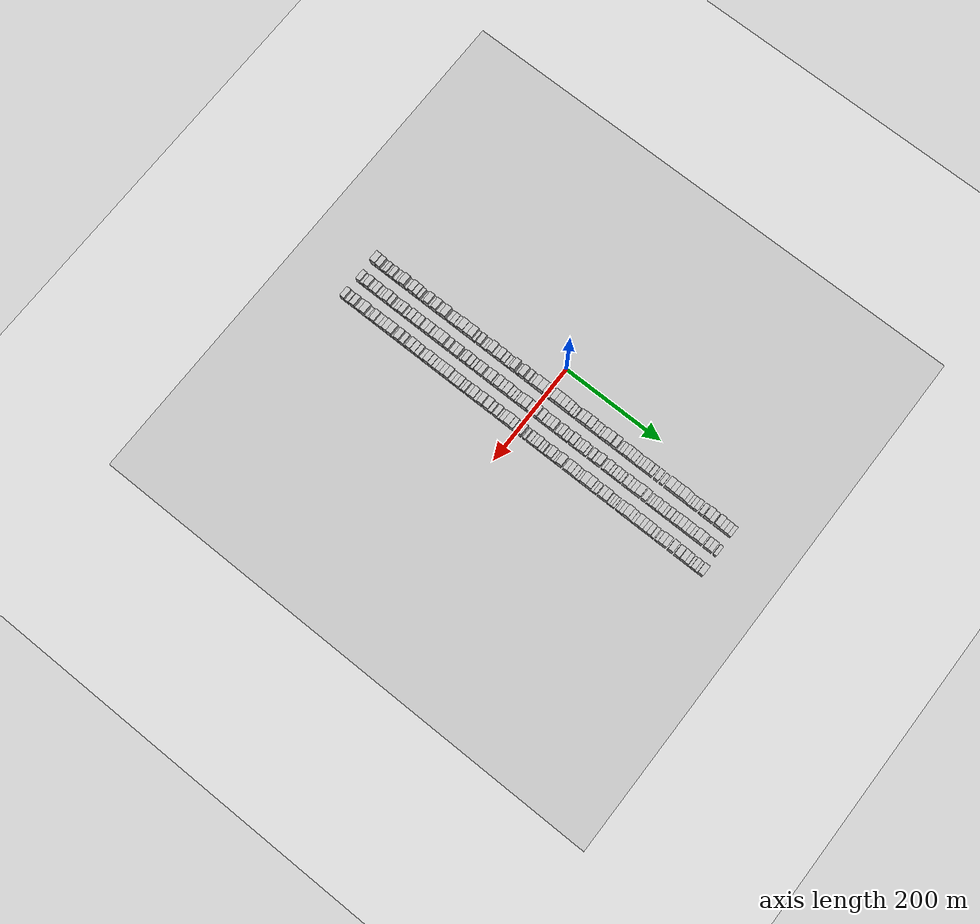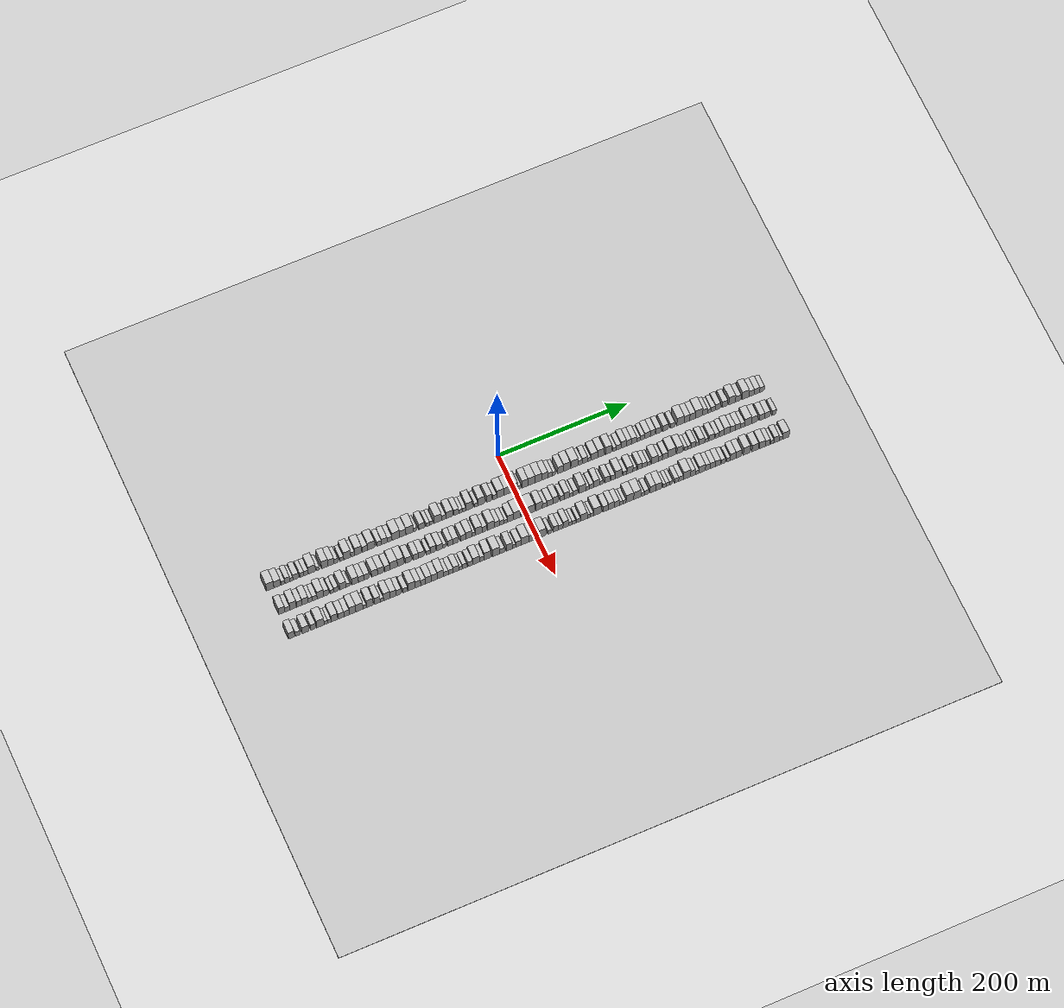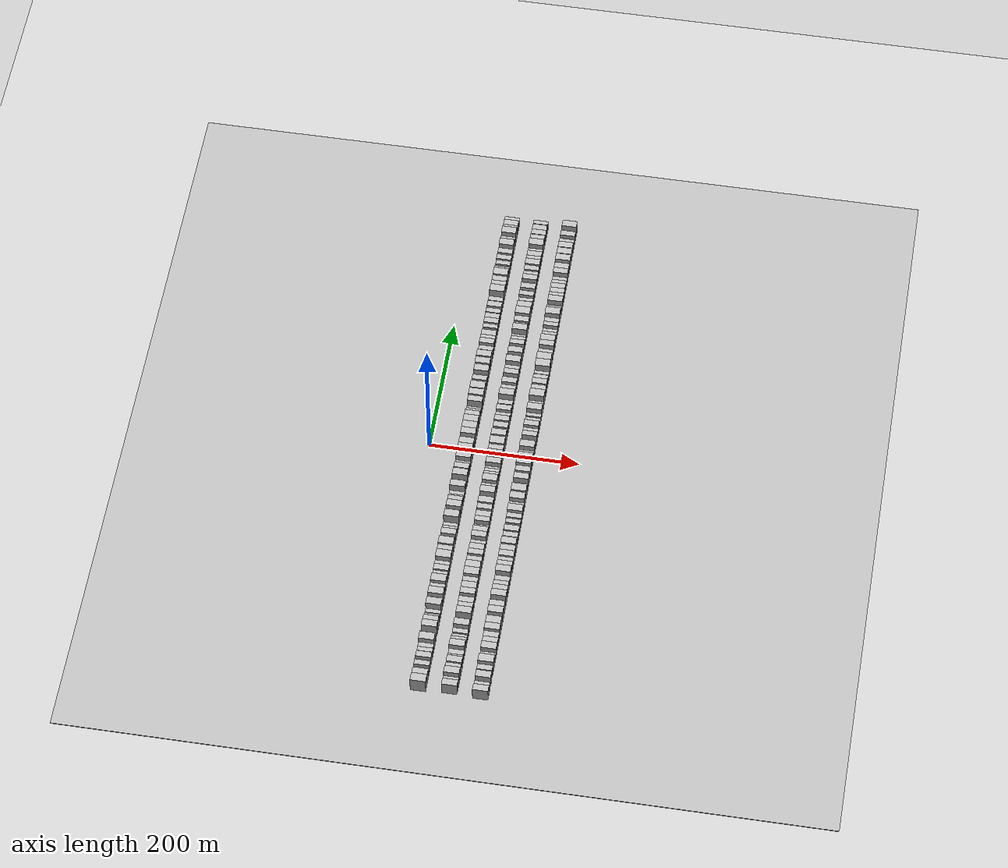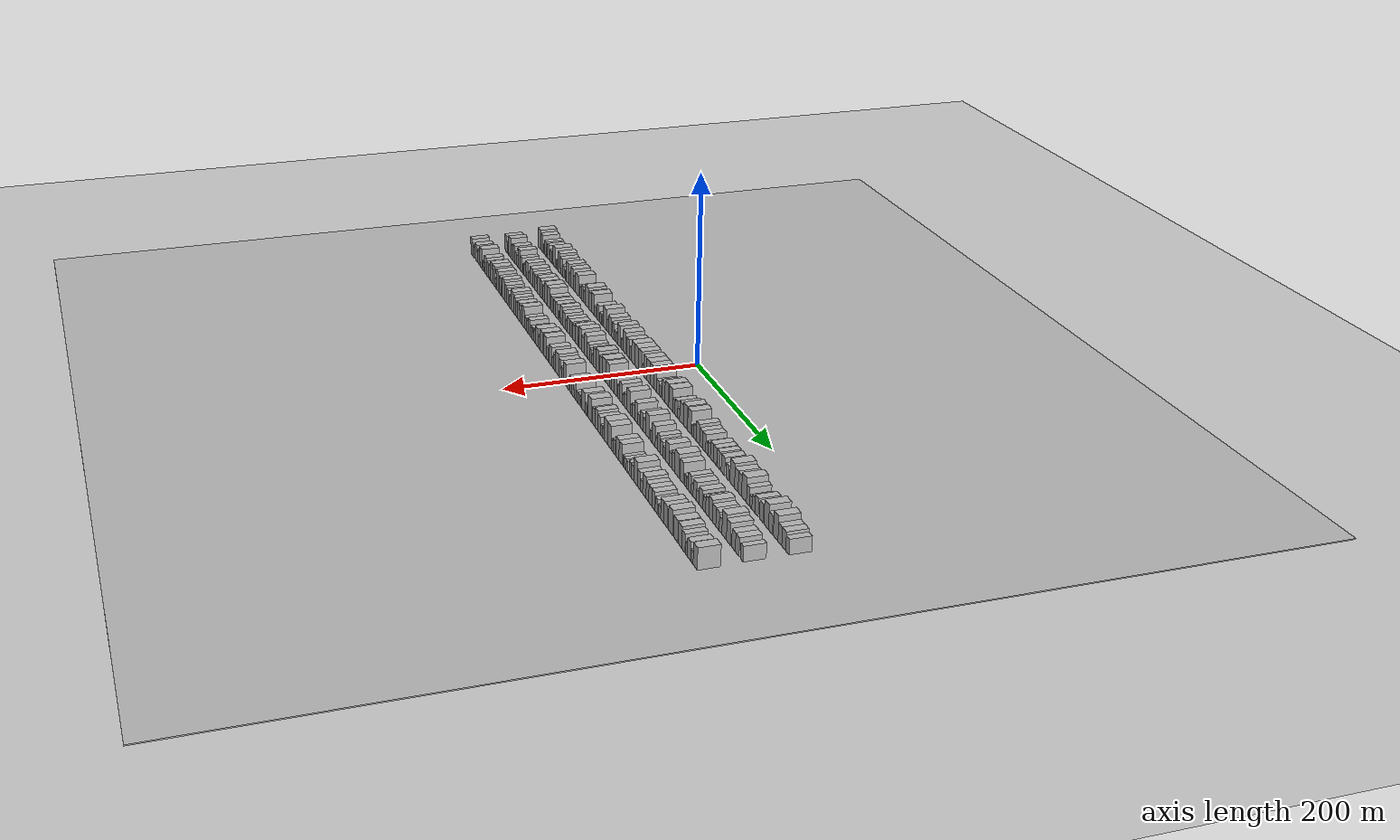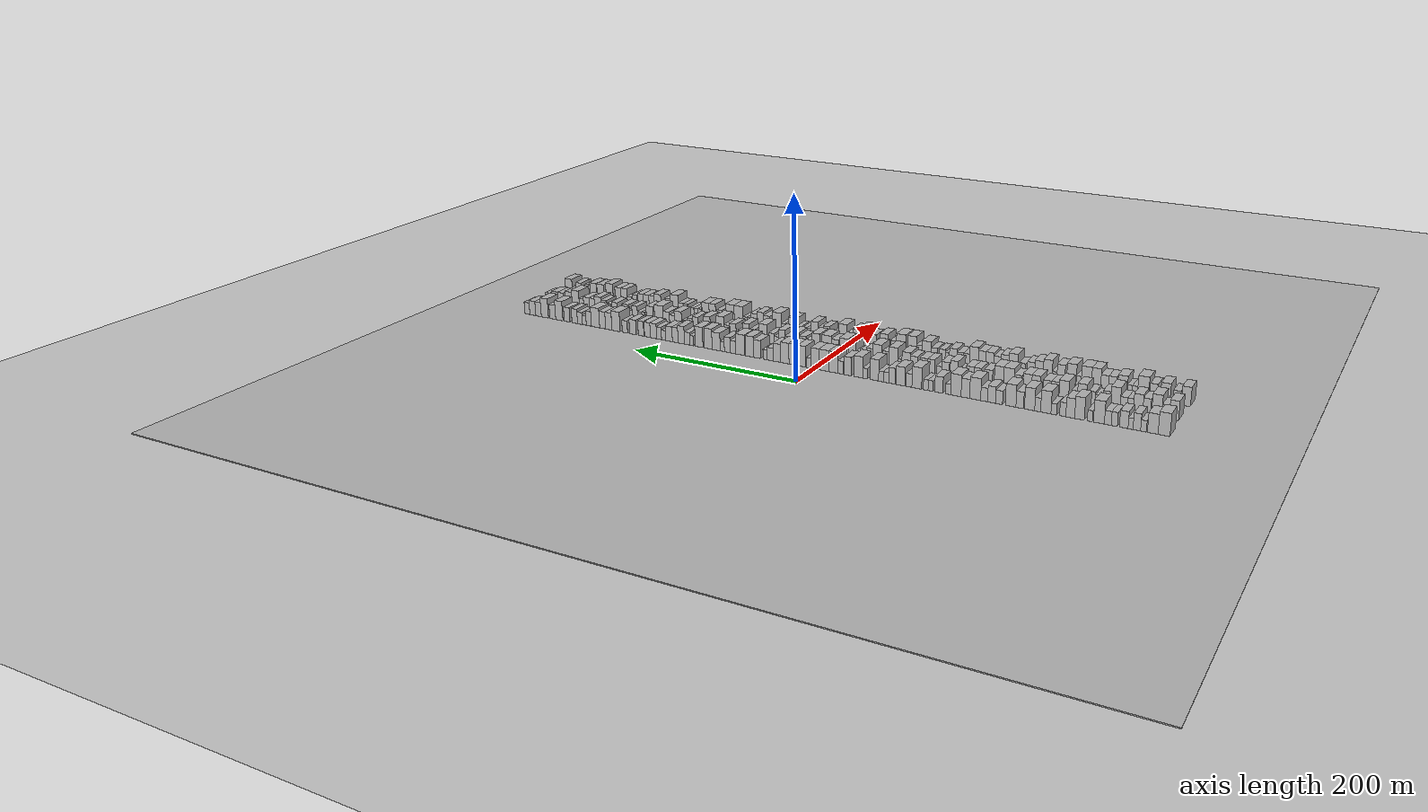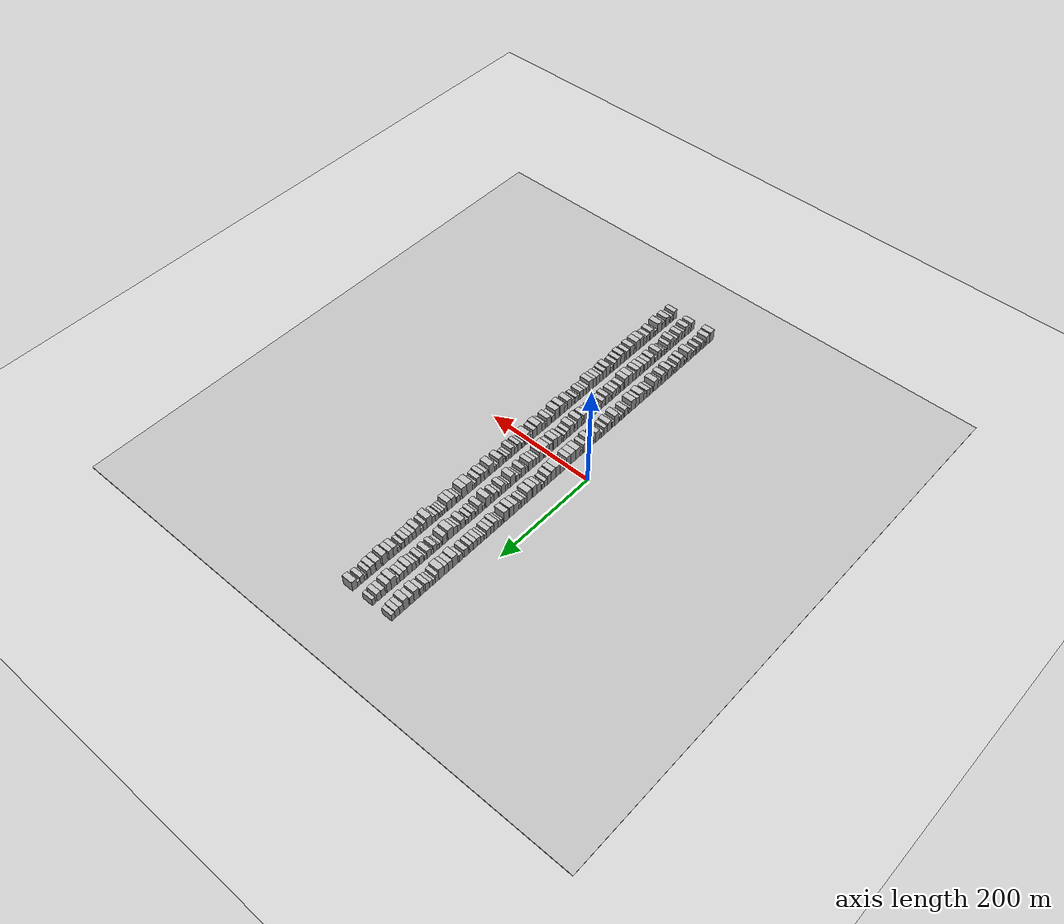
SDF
<?xml version="1.0" encoding="utf-8"?>

<sdf version="1.6">

   <world name="default">

      <gui fullscreen="0">

         <camera name="user_camera">

            <pose>-15 0 4.57585 0 0 0</pose>

            <view_controller>orbit</view_controller>

         </camera>

      </gui>

      <scene>

         <sky>

           <clouds>

             <speed>12</speed>

           </clouds>

         </sky>

         <ambient>0.4 0.4 0.4 1</ambient>

         <background>0.7 0.7 0.7 1</background>

         <shadows>1</shadows>

      </scene>

      <gravity>0 0 -9.8066</gravity>

      <magnetic_field>6e-06 2.3e-05 -4.2e-05</magnetic_field>

      <physics default="0" name="default_physics" type="ode">

         <ode>

            <solver>

               <type>quick</type>

               <iters>10</iters>

               <sor>1.0</sor>

               <use_dynamic_moi_rescaling>0</use_dynamic_moi_rescaling>

            </solver>

            <constraints>

               <cfm>0</cfm>

               <erp>0.2</erp>

               <contact_max_correcting_vel>100</contact_max_correcting_vel>

               <contact_surface_layer>0.001</contact_surface_layer>

            </constraints>

         </ode>

         <max_step_size>0.004</max_step_size>

         <real_time_factor>1</real_time_factor>

         <real_time_update_rate>250</real_time_update_rate>

      </physics>

      <light name="sun" type="directional">

         <cast_shadows>1</cast_shadows>

         <pose>0 0 10 0 0 0</pose>

         <diffuse>0.8 0.8 0.8 1</diffuse>

         <specular>0.2 0.2 0.2 1</specular>

         <attenuation>

            <range>1000</range>

            <constant>0.9</constant>

            <linear>0.01</linear>

            <quadratic>0.001</quadratic>

         </attenuation>

         <direction>-0.5 0.1 -0.9</direction>

      </light>

      <include>

         <name>ground_plane_1</name>

         <uri>model://HANNAS_ground_plane</uri>

         <pose>0 0 0  0 0 0</pose>

      </include>

      <include>

         <name>ground_plane_2</name>

         <uri>model://HANNAS_ground_plane</uri>

         <pose>100 0 0  0 0 0</pose>

      </include>

      <model name="building_1">

         <static>1</static>

         <pose frame="">50.0000 -374.2939 0 0.000000 0.000000 0.000000</pose>

         <link name="link">

            <pose frame="">0 0 12.00 0 0 0</pose>

            <collision name="collision">

               <geometry>

                  <box>

                     <size>20.0000 11.4122 24.0000</size>

                  </box>

               </geometry>

               <max_contacts>10</max_contacts>

               <surface>

                  <contact>

                     <ode/>

                  </contact>

                  <bounce/>

                  <friction>

                     <torsional>

                        <ode/>

                     </torsional>

                     <ode/>

                  </friction>

               </surface>

            </collision>

            <visual name="visual">

               <cast_shadows>0</cast_shadows>

               <geometry>

                  <box>

                     <size>20.0000 11.4122 24.0000</size>

                  </box>

               </geometry>

               <material>

                  <script>

                     <uri>model://HANNAS_wall/materials/scripts</uri>

                     <uri>model://HANNAS_wall/materials/textures</uri>

                     <name>vrc/HANNAS_wall</name>

                  </script>

               </material>

            </visual>

            <self_collide>0</self_collide>

            <enable_wind>0</enable_wind>

            <kinematic>0</kinematic>

         </link>

      </model>

      <model name="building_2">

         <static>1</static>

         <pose frame="">50.0000 -363.4568 0 0.000000 0.000000 0.000000</pose>

         <link name="link">

            <pose frame="">0 0 10.50 0 0 0</pose>

            <collision name="collision">

               <geometry>

                  <box>

                     <size>20.0000 10.2619 21.0000</size>

                  </box>

               </geometry>

               <max_contacts>10</max_contacts>

               <surface>

                  <contact>

                     <ode/>

                  </contact>

                  <bounce/>

                  <friction>

                     <torsional>

                        <ode/>

                     </torsional>

                     <ode/>

                  </friction>

               </surface>

            </collision>

            <visual name="visual">

               <cast_shadows>0</cast_shadows>

               <geometry>

                  <box>

                     <size>20.0000 10.2619 21.0000</size>

                  </box>

               </geometry>

               <material>

                  <script>

                     <uri>model://HANNAS_wall/materials/scripts</uri>

                     <uri>model://HANNAS_wall/materials/textures</uri>

                     <name>vrc/HANNAS_wall</name>

                  </script>

               </material>

            </visual>

            <self_collide>0</self_collide>

            <enable_wind>0</enable_wind>

            <kinematic>0</kinematic>

         </link>

      </model>

      <model name="building_3">

         <static>1</static>

         <pose frame="">50.0000 -354.5349 0 0.000000 0.000000 0.000000</pose>

         <link name="link">

            <pose frame="">0 0 6.00 0 0 0</pose>

            <collision name="collision">

               <geometry>

                  <box>

                     <size>20.0000 5.5819 12.0000</size>

                  </box>

               </geometry>

               <max_contacts>10</max_contacts>

               <surface>

                  <contact>

                     <ode/>

                  </contact>

                  <bounce/>

                  <friction>

                     <torsional>

                        <ode/>

                     </torsional>

                     <ode/>

                  </friction>

               </surface>

            </collision>

            <visual name="visual">

               <cast_shadows>0</cast_shadows>

               <geometry>

                  <box>

                     <size>20.0000 5.5819 12.0000</size>

                  </box>

               </geometry>

               <material>

                  <script>

                     <uri>model://HANNAS_wall/materials/scripts</uri>

                     <uri>model://HANNAS_wall/materials/textures</uri>

                     <name>vrc/HANNAS_wall</name>

                  </script>

               </material>

            </visual>

            <self_collide>0</self_collide>

            <enable_wind>0</enable_wind>

            <kinematic>0</kinematic>

         </link>

      </model>

      <model name="building_4">

         <static>1</static>

         <pose frame="">50.0000 -348.0788 0 0.000000 0.000000 0.000000</pose>

         <link name="link">

            <pose frame="">0 0 9.00 0 0 0</pose>

            <collision name="collision">

               <geometry>

                  <box>

                     <size>20.0000 7.3304 18.0000</size>

                  </box>

               </geometry>

               <max_contacts>10</max_contacts>

               <surface>

                  <contact>

                     <ode/>

                  </contact>

                  <bounce/>

                  <friction>

                     <torsional>

                        <ode/>

                     </torsional>

                     <ode/>

                  </friction>

               </surface>

            </collision>

            <visual name="visual">

               <cast_shadows>0</cast_shadows>

               <geometry>

                  <box>

                     <size>20.0000 7.3304 18.0000</size>

                  </box>

               </geometry>

               <material>

                  <script>

                     <uri>model://HANNAS_wall/materials/scripts</uri>

                     <uri>model://HANNAS_wall/materials/textures</uri>

                     <name>vrc/HANNAS_wall</name>

                  </script>

               </material>

            </visual>

            <self_collide>0</self_collide>

            <enable_wind>0</enable_wind>

            <kinematic>0</kinematic>

         </link>

      </model>

      <model name="building_5">

         <static>1</static>

         <pose frame="">50.0000 -342.0132 0 0.000000 0.000000 0.000000</pose>

         <link name="link">

            <pose frame="">0 0 6.00 0 0 0</pose>

            <collision name="collision">

               <geometry>

                  <box>

                     <size>20.0000 4.8006 12.0000</size>

                  </box>

               </geometry>

               <max_contacts>10</max_contacts>

               <surface>

                  <contact>

                     <ode/>

                  </contact>

                  <bounce/>

                  <friction>

                     <torsional>

                        <ode/>

                     </torsional>

                     <ode/>

                  </friction>

               </surface>

            </collision>

            <visual name="visual">

               <cast_shadows>0</cast_shadows>

               <geometry>

                  <box>

                     <size>20.0000 4.8006 12.0000</size>

                  </box>

               </geometry>

               <material>

                  <script>

                     <uri>model://HANNAS_wall/materials/scripts</uri>

                     <uri>model://HANNAS_wall/materials/textures</uri>

                     <name>vrc/HANNAS_wall</name>

                  </script>

               </material>

            </visual>

            <self_collide>0</self_collide>

            <enable_wind>0</enable_wind>

            <kinematic>0</kinematic>

         </link>

      </model>

      <model name="building_6">

         <static>1</static>

         <pose frame="">50.0000 -335.3827 0 0.000000 0.000000 0.000000</pose>

         <link name="link">

            <pose frame="">0 0 9.00 0 0 0</pose>

            <collision name="collision">

               <geometry>

                  <box>

                     <size>20.0000 8.4605 18.0000</size>

                  </box>

               </geometry>

               <max_contacts>10</max_contacts>

               <surface>

                  <contact>

                     <ode/>

                  </contact>

                  <bounce/>

                  <friction>

                     <torsional>

                        <ode/>

                     </torsional>

                     <ode/>

                  </friction>

               </surface>

            </collision>

            <visual name="visual">

               <cast_shadows>0</cast_shadows>

               <geometry>

                  <box>

                     <size>20.0000 8.4605 18.0000</size>

                  </box>

               </geometry>

               <material>

                  <script>

                     <uri>model://HANNAS_wall/materials/scripts</uri>

                     <uri>model://HANNAS_wall/materials/textures</uri>

                     <name>vrc/HANNAS_wall</name>

                  </script>

               </material>

            </visual>

            <self_collide>0</self_collide>

            <enable_wind>0</enable_wind>

            <kinematic>0</kinematic>

         </link>

      </model>

      <model name="building_7">

         <static>1</static>

         <pose frame="">50.0000 -326.1013 0 0.000000 0.000000 0.000000</pose>

         <link name="link">

            <pose frame="">0 0 7.50 0 0 0</pose>

            <collision name="collision">

               <geometry>

                  <box>

                     <size>20.0000 6.1022 15.0000</size>

                  </box>

               </geometry>

               <max_contacts>10</max_contacts>

               <surface>

                  <contact>

                     <ode/>

                  </contact>

                  <bounce/>

                  <friction>

                     <torsional>

                        <ode/>

                     </torsional>

                     <ode/>

                  </friction>

               </surface>

            </collision>

            <visual name="visual">

               <cast_shadows>0</cast_shadows>

               <geometry>

                  <box>

                     <size>20.0000 6.1022 15.0000</size>

                  </box>

               </geometry>

               <material>

                  <script>

                     <uri>model://HANNAS_wall/materials/scripts</uri>

                     <uri>model://HANNAS_wall/materials/textures</uri>

                     <name>vrc/HANNAS_wall</name>

                  </script>

               </material>

            </visual>

            <self_collide>0</self_collide>

            <enable_wind>0</enable_wind>

            <kinematic>0</kinematic>

         </link>

      </model>

      <model name="building_8">

         <static>1</static>

         <pose frame="">50.0000 -319.6761 0 0.000000 0.000000 0.000000</pose>

         <link name="link">

            <pose frame="">0 0 7.50 0 0 0</pose>

            <collision name="collision">

               <geometry>

                  <box>

                     <size>20.0000 6.7484 15.0000</size>

                  </box>

               </geometry>

               <max_contacts>10</max_contacts>

               <surface>

                  <contact>

                     <ode/>

                  </contact>

                  <bounce/>

                  <friction>

                     <torsional>

                        <ode/>

                     </torsional>

                     <ode/>

                  </friction>

               </surface>

            </collision>

            <visual name="visual">

               <cast_shadows>0</cast_shadows>

               <geometry>

                  <box>

                     <size>20.0000 6.7484 15.0000</size>

                  </box>

               </geometry>

               <material>

                  <script>

                     <uri>model://HANNAS_wall/materials/scripts</uri>

                     <uri>model://HANNAS_wall/materials/textures</uri>

                     <name>vrc/HANNAS_wall</name>

                  </script>

               </material>

            </visual>

            <self_collide>0</self_collide>

            <enable_wind>0</enable_wind>

            <kinematic>0</kinematic>

         </link>

      </model>

      <model name="building_9">

         <static>1</static>

         <pose frame="">50.0000 -310.8692 0 0.000000 0.000000 0.000000</pose>

         <link name="link">

            <pose frame="">0 0 12.00 0 0 0</pose>

            <collision name="collision">

               <geometry>

                  <box>

                     <size>20.0000 10.8653 24.0000</size>

                  </box>

               </geometry>

               <max_contacts>10</max_contacts>

               <surface>

                  <contact>

                     <ode/>

                  </contact>

                  <bounce/>

                  <friction>

                     <torsional>

                        <ode/>

                     </torsional>

                     <ode/>

                  </friction>

               </surface>

            </collision>

            <visual name="visual">

               <cast_shadows>0</cast_shadows>

               <geometry>

                  <box>

                     <size>20.0000 10.8653 24.0000</size>

                  </box>

               </geometry>

               <material>

                  <script>

                     <uri>model://HANNAS_wall/materials/scripts</uri>

                     <uri>model://HANNAS_wall/materials/textures</uri>

                     <name>vrc/HANNAS_wall</name>

                  </script>

               </material>

            </visual>

            <self_collide>0</self_collide>

            <enable_wind>0</enable_wind>

            <kinematic>0</kinematic>

         </link>

      </model>

      <model name="building_10">

         <static>1</static>

         <pose frame="">50.0000 -301.8621 0 0.000000 0.000000 0.000000</pose>

         <link name="link">

            <pose frame="">0 0 6.00 0 0 0</pose>

            <collision name="collision">

               <geometry>

                  <box>

                     <size>20.0000 5.1489 12.0000</size>

                  </box>

               </geometry>

               <max_contacts>10</max_contacts>

               <surface>

                  <contact>

                     <ode/>

                  </contact>

                  <bounce/>

                  <friction>

                     <torsional>

                        <ode/>

                     </torsional>

                     <ode/>

                  </friction>

               </surface>

            </collision>

            <visual name="visual">

               <cast_shadows>0</cast_shadows>

               <geometry>

                  <box>

                     <size>20.0000 5.1489 12.0000</size>

                  </box>

               </geometry>

               <material>

                  <script>

                     <uri>model://HANNAS_wall/materials/scripts</uri>

                     <uri>model://HANNAS_wall/materials/textures</uri>

                     <name>vrc/HANNAS_wall</name>

                  </script>

               </material>

            </visual>

            <self_collide>0</self_collide>

            <enable_wind>0</enable_wind>

            <kinematic>0</kinematic>

         </link>

      </model>

      <model name="building_11">

         <static>1</static>

         <pose frame="">50.0000 -291.4230 0 0.000000 0.000000 0.000000</pose>

         <link name="link">

            <pose frame="">0 0 12.00 0 0 0</pose>

            <collision name="collision">

               <geometry>

                  <box>

                     <size>20.0000 9.7293 24.0000</size>

                  </box>

               </geometry>

               <max_contacts>10</max_contacts>

               <surface>

                  <contact>

                     <ode/>

                  </contact>

                  <bounce/>

                  <friction>

                     <torsional>

                        <ode/>

                     </torsional>

                     <ode/>

                  </friction>

               </surface>

            </collision>

            <visual name="visual">

               <cast_shadows>0</cast_shadows>

               <geometry>

                  <box>

                     <size>20.0000 9.7293 24.0000</size>

                  </box>

               </geometry>

               <material>

                  <script>

                     <uri>model://HANNAS_wall/materials/scripts</uri>

                     <uri>model://HANNAS_wall/materials/textures</uri>

                     <name>vrc/HANNAS_wall</name>

                  </script>

               </material>

            </visual>

            <self_collide>0</self_collide>

            <enable_wind>0</enable_wind>

            <kinematic>0</kinematic>

         </link>

      </model>

      <model name="building_12">

         <static>1</static>

         <pose frame="">50.0000 -282.0845 0 0.000000 0.000000 0.000000</pose>

         <link name="link">

            <pose frame="">0 0 10.50 0 0 0</pose>

            <collision name="collision">

               <geometry>

                  <box>

                     <size>20.0000 8.9477 21.0000</size>

                  </box>

               </geometry>

               <max_contacts>10</max_contacts>

               <surface>

                  <contact>

                     <ode/>

                  </contact>

                  <bounce/>

                  <friction>

                     <torsional>

                        <ode/>

                     </torsional>

                     <ode/>

                  </friction>

               </surface>

            </collision>

            <visual name="visual">

               <cast_shadows>0</cast_shadows>

               <geometry>

                  <box>

                     <size>20.0000 8.9477 21.0000</size>

                  </box>

               </geometry>

               <material>

                  <script>

                     <uri>model://HANNAS_wall/materials/scripts</uri>

                     <uri>model://HANNAS_wall/materials/textures</uri>

                     <name>vrc/HANNAS_wall</name>

                  </script>

               </material>

            </visual>

            <self_collide>0</self_collide>

            <enable_wind>0</enable_wind>

            <kinematic>0</kinematic>

         </link>

      </model>

      <model name="building_13">

         <static>1</static>

         <pose frame="">50.0000 -274.4769 0 0.000000 0.000000 0.000000</pose>

         <link name="link">

            <pose frame="">0 0 7.50 0 0 0</pose>

            <collision name="collision">

               <geometry>

                  <box>

                     <size>20.0000 6.2676 15.0000</size>

                  </box>

               </geometry>

               <max_contacts>10</max_contacts>

               <surface>

                  <contact>

                     <ode/>

                  </contact>

                  <bounce/>

                  <friction>

                     <torsional>

                        <ode/>

                     </torsional>

                     <ode/>

                  </friction>

               </surface>

            </collision>

            <visual name="visual">

               <cast_shadows>0</cast_shadows>

               <geometry>

                  <box>

                     <size>20.0000 6.2676 15.0000</size>

                  </box>

               </geometry>

               <material>

                  <script>

                     <uri>model://HANNAS_wall/materials/scripts</uri>

                     <uri>model://HANNAS_wall/materials/textures</uri>

                     <name>vrc/HANNAS_wall</name>

                  </script>

               </material>

            </visual>

            <self_collide>0</self_collide>

            <enable_wind>0</enable_wind>

            <kinematic>0</kinematic>

         </link>

      </model>

      <model name="building_14">

         <static>1</static>

         <pose frame="">50.0000 -265.4122 0 0.000000 0.000000 0.000000</pose>

         <link name="link">

            <pose frame="">0 0 6.00 0 0 0</pose>

            <collision name="collision">

               <geometry>

                  <box>

                     <size>20.0000 5.8618 12.0000</size>

                  </box>

               </geometry>

               <max_contacts>10</max_contacts>

               <surface>

                  <contact>

                     <ode/>

                  </contact>

                  <bounce/>

                  <friction>

                     <torsional>

                        <ode/>

                     </torsional>

                     <ode/>

                  </friction>

               </surface>

            </collision>

            <visual name="visual">

               <cast_shadows>0</cast_shadows>

               <geometry>

                  <box>

                     <size>20.0000 5.8618 12.0000</size>

                  </box>

               </geometry>

               <material>

                  <script>

                     <uri>model://HANNAS_wall/materials/scripts</uri>

                     <uri>model://HANNAS_wall/materials/textures</uri>

                     <name>vrc/HANNAS_wall</name>

                  </script>

               </material>

            </visual>

            <self_collide>0</self_collide>

            <enable_wind>0</enable_wind>

            <kinematic>0</kinematic>

         </link>

      </model>

      <model name="building_15">

         <static>1</static>

         <pose frame="">50.0000 -257.1550 0 0.000000 0.000000 0.000000</pose>

         <link name="link">

            <pose frame="">0 0 12.00 0 0 0</pose>

            <collision name="collision">

               <geometry>

                  <box>

                     <size>20.0000 10.6525 24.0000</size>

                  </box>

               </geometry>

               <max_contacts>10</max_contacts>

               <surface>

                  <contact>

                     <ode/>

                  </contact>

                  <bounce/>

                  <friction>

                     <torsional>

                        <ode/>

                     </torsional>

                     <ode/>

                  </friction>

               </surface>

            </collision>

            <visual name="visual">

               <cast_shadows>0</cast_shadows>

               <geometry>

                  <box>

                     <size>20.0000 10.6525 24.0000</size>

                  </box>

               </geometry>

               <material>

                  <script>

                     <uri>model://HANNAS_wall/materials/scripts</uri>

                     <uri>model://HANNAS_wall/materials/textures</uri>

                     <name>vrc/HANNAS_wall</name>

                  </script>

               </material>

            </visual>

            <self_collide>0</self_collide>

            <enable_wind>0</enable_wind>

            <kinematic>0</kinematic>

         </link>

      </model>

      <model name="building_16">

         <static>1</static>

         <pose frame="">50.0000 -248.7654 0 0.000000 0.000000 0.000000</pose>

         <link name="link">

            <pose frame="">0 0 7.50 0 0 0</pose>

            <collision name="collision">

               <geometry>

                  <box>

                     <size>20.0000 6.1267 15.0000</size>

                  </box>

               </geometry>

               <max_contacts>10</max_contacts>

               <surface>

                  <contact>

                     <ode/>

                  </contact>

                  <bounce/>

                  <friction>

                     <torsional>

                        <ode/>

                     </torsional>

                     <ode/>

                  </friction>

               </surface>

            </collision>

            <visual name="visual">

               <cast_shadows>0</cast_shadows>

               <geometry>

                  <box>

                     <size>20.0000 6.1267 15.0000</size>

                  </box>

               </geometry>

               <material>

                  <script>

                     <uri>model://HANNAS_wall/materials/scripts</uri>

                     <uri>model://HANNAS_wall/materials/textures</uri>

                     <name>vrc/HANNAS_wall</name>

                  </script>

               </material>

            </visual>

            <self_collide>0</self_collide>

            <enable_wind>0</enable_wind>

            <kinematic>0</kinematic>

         </link>

      </model>

      <model name="building_17">

         <static>1</static>

         <pose frame="">50.0000 -240.4099 0 0.000000 0.000000 0.000000</pose>

         <link name="link">

            <pose frame="">0 0 12.00 0 0 0</pose>

            <collision name="collision">

               <geometry>

                  <box>

                     <size>20.0000 10.5843 24.0000</size>

                  </box>

               </geometry>

               <max_contacts>10</max_contacts>

               <surface>

                  <contact>

                     <ode/>

                  </contact>

                  <bounce/>

                  <friction>

                     <torsional>

                        <ode/>

                     </torsional>

                     <ode/>

                  </friction>

               </surface>

            </collision>

            <visual name="visual">

               <cast_shadows>0</cast_shadows>

               <geometry>

                  <box>

                     <size>20.0000 10.5843 24.0000</size>

                  </box>

               </geometry>

               <material>

                  <script>

                     <uri>model://HANNAS_wall/materials/scripts</uri>

                     <uri>model://HANNAS_wall/materials/textures</uri>

                     <name>vrc/HANNAS_wall</name>

                  </script>

               </material>

            </visual>

            <self_collide>0</self_collide>

            <enable_wind>0</enable_wind>

            <kinematic>0</kinematic>

         </link>

      </model>

      <model name="building_18">

         <static>1</static>

         <pose frame="">50.0000 -230.1496 0 0.000000 0.000000 0.000000</pose>

         <link name="link">

            <pose frame="">0 0 9.00 0 0 0</pose>

            <collision name="collision">

               <geometry>

                  <box>

                     <size>20.0000 7.9365 18.0000</size>

                  </box>

               </geometry>

               <max_contacts>10</max_contacts>

               <surface>

                  <contact>

                     <ode/>

                  </contact>

                  <bounce/>

                  <friction>

                     <torsional>

                        <ode/>

                     </torsional>

                     <ode/>

                  </friction>

               </surface>

            </collision>

            <visual name="visual">

               <cast_shadows>0</cast_shadows>

               <geometry>

                  <box>

                     <size>20.0000 7.9365 18.0000</size>

                  </box>

               </geometry>

               <material>

                  <script>

                     <uri>model://HANNAS_wall/materials/scripts</uri>

                     <uri>model://HANNAS_wall/materials/textures</uri>

                     <name>vrc/HANNAS_wall</name>

                  </script>

               </material>

            </visual>

            <self_collide>0</self_collide>

            <enable_wind>0</enable_wind>

            <kinematic>0</kinematic>

         </link>

      </model>

      <model name="building_19">

         <static>1</static>

         <pose frame="">50.0000 -220.5904 0 0.000000 0.000000 0.000000</pose>

         <link name="link">

            <pose frame="">0 0 12.00 0 0 0</pose>

            <collision name="collision">

               <geometry>

                  <box>

                     <size>20.0000 11.1819 24.0000</size>

                  </box>

               </geometry>

               <max_contacts>10</max_contacts>

               <surface>

                  <contact>

                     <ode/>

                  </contact>

                  <bounce/>

                  <friction>

                     <torsional>

                        <ode/>

                     </torsional>

                     <ode/>

                  </friction>

               </surface>

            </collision>

            <visual name="visual">

               <cast_shadows>0</cast_shadows>

               <geometry>

                  <box>

                     <size>20.0000 11.1819 24.0000</size>

                  </box>

               </geometry>

               <material>

                  <script>

                     <uri>model://HANNAS_wall/materials/scripts</uri>

                     <uri>model://HANNAS_wall/materials/textures</uri>

                     <name>vrc/HANNAS_wall</name>

                  </script>

               </material>

            </visual>

            <self_collide>0</self_collide>

            <enable_wind>0</enable_wind>

            <kinematic>0</kinematic>

         </link>

      </model>

      <model name="building_20">

         <static>1</static>

         <pose frame="">50.0000 -208.3554 0 0.000000 0.000000 0.000000</pose>

         <link name="link">

            <pose frame="">0 0 7.50 0 0 0</pose>

            <collision name="collision">

               <geometry>

                  <box>

                     <size>20.0000 7.2881 15.0000</size>

                  </box>

               </geometry>

               <max_contacts>10</max_contacts>

               <surface>

                  <contact>

                     <ode/>

                  </contact>

                  <bounce/>

                  <friction>

                     <torsional>

                        <ode/>

                     </torsional>

                     <ode/>

                  </friction>

               </surface>

            </collision>

            <visual name="visual">

               <cast_shadows>0</cast_shadows>

               <geometry>

                  <box>

                     <size>20.0000 7.2881 15.0000</size>

                  </box>

               </geometry>

               <material>

                  <script>

                     <uri>model://HANNAS_wall/materials/scripts</uri>

                     <uri>model://HANNAS_wall/materials/textures</uri>

                     <name>vrc/HANNAS_wall</name>

                  </script>

               </material>

            </visual>

            <self_collide>0</self_collide>

            <enable_wind>0</enable_wind>

            <kinematic>0</kinematic>

         </link>

      </model>

      <model name="building_21">

         <static>1</static>

         <pose frame="">50.0000 -200.5010 0 0.000000 0.000000 0.000000</pose>

         <link name="link">

            <pose frame="">0 0 9.00 0 0 0</pose>

            <collision name="collision">

               <geometry>

                  <box>

                     <size>20.0000 8.4207 18.0000</size>

                  </box>

               </geometry>

               <max_contacts>10</max_contacts>

               <surface>

                  <contact>

                     <ode/>

                  </contact>

                  <bounce/>

                  <friction>

                     <torsional>

                        <ode/>

                     </torsional>

                     <ode/>

                  </friction>

               </surface>

            </collision>

            <visual name="visual">

               <cast_shadows>0</cast_shadows>

               <geometry>

                  <box>

                     <size>20.0000 8.4207 18.0000</size>

                  </box>

               </geometry>

               <material>

                  <script>

                     <uri>model://HANNAS_wall/materials/scripts</uri>

                     <uri>model://HANNAS_wall/materials/textures</uri>

                     <name>vrc/HANNAS_wall</name>

                  </script>

               </material>

            </visual>

            <self_collide>0</self_collide>

            <enable_wind>0</enable_wind>

            <kinematic>0</kinematic>

         </link>

      </model>

      <model name="building_22">

         <static>1</static>

         <pose frame="">50.0000 -192.5432 0 0.000000 0.000000 0.000000</pose>

         <link name="link">

            <pose frame="">0 0 7.50 0 0 0</pose>

            <collision name="collision">

               <geometry>

                  <box>

                     <size>20.0000 7.4948 15.0000</size>

                  </box>

               </geometry>

               <max_contacts>10</max_contacts>

               <surface>

                  <contact>

                     <ode/>

                  </contact>

                  <bounce/>

                  <friction>

                     <torsional>

                        <ode/>

                     </torsional>

                     <ode/>

                  </friction>

               </surface>

            </collision>

            <visual name="visual">

               <cast_shadows>0</cast_shadows>

               <geometry>

                  <box>

                     <size>20.0000 7.4948 15.0000</size>

                  </box>

               </geometry>

               <material>

                  <script>

                     <uri>model://HANNAS_wall/materials/scripts</uri>

                     <uri>model://HANNAS_wall/materials/textures</uri>

                     <name>vrc/HANNAS_wall</name>

                  </script>

               </material>

            </visual>

            <self_collide>0</self_collide>

            <enable_wind>0</enable_wind>

            <kinematic>0</kinematic>

         </link>

      </model>

      <model name="building_23">

         <static>1</static>

         <pose frame="">50.0000 -182.8648 0 0.000000 0.000000 0.000000</pose>

         <link name="link">

            <pose frame="">0 0 12.00 0 0 0</pose>

            <collision name="collision">

               <geometry>

                  <box>

                     <size>20.0000 11.8621 24.0000</size>

                  </box>

               </geometry>

               <max_contacts>10</max_contacts>

               <surface>

                  <contact>

                     <ode/>

                  </contact>

                  <bounce/>

                  <friction>

                     <torsional>

                        <ode/>

                     </torsional>

                     <ode/>

                  </friction>

               </surface>

            </collision>

            <visual name="visual">

               <cast_shadows>0</cast_shadows>

               <geometry>

                  <box>

                     <size>20.0000 11.8621 24.0000</size>

                  </box>

               </geometry>

               <material>

                  <script>

                     <uri>model://HANNAS_wall/materials/scripts</uri>

                     <uri>model://HANNAS_wall/materials/textures</uri>

                     <name>vrc/HANNAS_wall</name>

                  </script>

               </material>

            </visual>

            <self_collide>0</self_collide>

            <enable_wind>0</enable_wind>

            <kinematic>0</kinematic>

         </link>

      </model>

      <model name="building_24">

         <static>1</static>

         <pose frame="">50.0000 -172.2734 0 0.000000 0.000000 0.000000</pose>

         <link name="link">

            <pose frame="">0 0 10.50 0 0 0</pose>

            <collision name="collision">

               <geometry>

                  <box>

                     <size>20.0000 9.3207 21.0000</size>

                  </box>

               </geometry>

               <max_contacts>10</max_contacts>

               <surface>

                  <contact>

                     <ode/>

                  </contact>

                  <bounce/>

                  <friction>

                     <torsional>

                        <ode/>

                     </torsional>

                     <ode/>

                  </friction>

               </surface>

            </collision>

            <visual name="visual">

               <cast_shadows>0</cast_shadows>

               <geometry>

                  <box>

                     <size>20.0000 9.3207 21.0000</size>

                  </box>

               </geometry>

               <material>

                  <script>

                     <uri>model://HANNAS_wall/materials/scripts</uri>

                     <uri>model://HANNAS_wall/materials/textures</uri>

                     <name>vrc/HANNAS_wall</name>

                  </script>

               </material>

            </visual>

            <self_collide>0</self_collide>

            <enable_wind>0</enable_wind>

            <kinematic>0</kinematic>

         </link>

      </model>

      <model name="building_25">

         <static>1</static>

         <pose frame="">50.0000 -161.8977 0 0.000000 0.000000 0.000000</pose>

         <link name="link">

            <pose frame="">0 0 12.00 0 0 0</pose>

            <collision name="collision">

               <geometry>

                  <box>

                     <size>20.0000 11.4307 24.0000</size>

                  </box>

               </geometry>

               <max_contacts>10</max_contacts>

               <surface>

                  <contact>

                     <ode/>

                  </contact>

                  <bounce/>

                  <friction>

                     <torsional>

                        <ode/>

                     </torsional>

                     <ode/>

                  </friction>

               </surface>

            </collision>

            <visual name="visual">

               <cast_shadows>0</cast_shadows>

               <geometry>

                  <box>

                     <size>20.0000 11.4307 24.0000</size>

                  </box>

               </geometry>

               <material>

                  <script>

                     <uri>model://HANNAS_wall/materials/scripts</uri>

                     <uri>model://HANNAS_wall/materials/textures</uri>

                     <name>vrc/HANNAS_wall</name>

                  </script>

               </material>

            </visual>

            <self_collide>0</self_collide>

            <enable_wind>0</enable_wind>

            <kinematic>0</kinematic>

         </link>

      </model>

      <model name="building_26">

         <static>1</static>

         <pose frame="">50.0000 -153.4849 0 0.000000 0.000000 0.000000</pose>

         <link name="link">

            <pose frame="">0 0 6.00 0 0 0</pose>

            <collision name="collision">

               <geometry>

                  <box>

                     <size>20.0000 5.3948 12.0000</size>

                  </box>

               </geometry>

               <max_contacts>10</max_contacts>

               <surface>

                  <contact>

                     <ode/>

                  </contact>

                  <bounce/>

                  <friction>

                     <torsional>

                        <ode/>

                     </torsional>

                     <ode/>

                  </friction>

               </surface>

            </collision>

            <visual name="visual">

               <cast_shadows>0</cast_shadows>

               <geometry>

                  <box>

                     <size>20.0000 5.3948 12.0000</size>

                  </box>

               </geometry>

               <material>

                  <script>

                     <uri>model://HANNAS_wall/materials/scripts</uri>

                     <uri>model://HANNAS_wall/materials/textures</uri>

                     <name>vrc/HANNAS_wall</name>

                  </script>

               </material>

            </visual>

            <self_collide>0</self_collide>

            <enable_wind>0</enable_wind>

            <kinematic>0</kinematic>

         </link>

      </model>

      <model name="building_27">

         <static>1</static>

         <pose frame="">50.0000 -143.3546 0 0.000000 0.000000 0.000000</pose>

         <link name="link">

            <pose frame="">0 0 9.00 0 0 0</pose>

            <collision name="collision">

               <geometry>

                  <box>

                     <size>20.0000 8.8659 18.0000</size>

                  </box>

               </geometry>

               <max_contacts>10</max_contacts>

               <surface>

                  <contact>

                     <ode/>

                  </contact>

                  <bounce/>

                  <friction>

                     <torsional>

                        <ode/>

                     </torsional>

                     <ode/>

                  </friction>

               </surface>

            </collision>

            <visual name="visual">

               <cast_shadows>0</cast_shadows>

               <geometry>

                  <box>

                     <size>20.0000 8.8659 18.0000</size>

                  </box>

               </geometry>

               <material>

                  <script>

                     <uri>model://HANNAS_wall/materials/scripts</uri>

                     <uri>model://HANNAS_wall/materials/textures</uri>

                     <name>vrc/HANNAS_wall</name>

                  </script>

               </material>

            </visual>

            <self_collide>0</self_collide>

            <enable_wind>0</enable_wind>

            <kinematic>0</kinematic>

         </link>

      </model>

      <model name="building_28">

         <static>1</static>

         <pose frame="">50.0000 -134.1133 0 0.000000 0.000000 0.000000</pose>

         <link name="link">

            <pose frame="">0 0 6.00 0 0 0</pose>

            <collision name="collision">

               <geometry>

                  <box>

                     <size>20.0000 5.6167 12.0000</size>

                  </box>

               </geometry>

               <max_contacts>10</max_contacts>

               <surface>

                  <contact>

                     <ode/>

                  </contact>

                  <bounce/>

                  <friction>

                     <torsional>

                        <ode/>

                     </torsional>

                     <ode/>

                  </friction>

               </surface>

            </collision>

            <visual name="visual">

               <cast_shadows>0</cast_shadows>

               <geometry>

                  <box>

                     <size>20.0000 5.6167 12.0000</size>

                  </box>

               </geometry>

               <material>

                  <script>

                     <uri>model://HANNAS_wall/materials/scripts</uri>

                     <uri>model://HANNAS_wall/materials/textures</uri>

                     <name>vrc/HANNAS_wall</name>

                  </script>

               </material>

            </visual>

            <self_collide>0</self_collide>

            <enable_wind>0</enable_wind>

            <kinematic>0</kinematic>

         </link>

      </model>

      <model name="building_29">

         <static>1</static>

         <pose frame="">50.0000 -128.7262 0 0.000000 0.000000 0.000000</pose>

         <link name="link">

            <pose frame="">0 0 6.00 0 0 0</pose>

            <collision name="collision">

               <geometry>

                  <box>

                     <size>20.0000 5.1574 12.0000</size>

                  </box>

               </geometry>

               <max_contacts>10</max_contacts>

               <surface>

                  <contact>

                     <ode/>

                  </contact>

                  <bounce/>

                  <friction>

                     <torsional>

                        <ode/>

                     </torsional>

                     <ode/>

                  </friction>

               </surface>

            </collision>

            <visual name="visual">

               <cast_shadows>0</cast_shadows>

               <geometry>

                  <box>

                     <size>20.0000 5.1574 12.0000</size>

                  </box>

               </geometry>

               <material>

                  <script>

                     <uri>model://HANNAS_wall/materials/scripts</uri>

                     <uri>model://HANNAS_wall/materials/textures</uri>

                     <name>vrc/HANNAS_wall</name>

                  </script>

               </material>

            </visual>

            <self_collide>0</self_collide>

            <enable_wind>0</enable_wind>

            <kinematic>0</kinematic>

         </link>

      </model>

      <model name="building_30">

         <static>1</static>

         <pose frame="">50.0000 -118.6920 0 0.000000 0.000000 0.000000</pose>

         <link name="link">

            <pose frame="">0 0 12.00 0 0 0</pose>

            <collision name="collision">

               <geometry>

                  <box>

                     <size>20.0000 10.9108 24.0000</size>

                  </box>

               </geometry>

               <max_contacts>10</max_contacts>

               <surface>

                  <contact>

                     <ode/>

                  </contact>

                  <bounce/>

                  <friction>

                     <torsional>

                        <ode/>

                     </torsional>

                     <ode/>

                  </friction>

               </surface>

            </collision>

            <visual name="visual">

               <cast_shadows>0</cast_shadows>

               <geometry>

                  <box>

                     <size>20.0000 10.9108 24.0000</size>

                  </box>

               </geometry>

               <material>

                  <script>

                     <uri>model://HANNAS_wall/materials/scripts</uri>

                     <uri>model://HANNAS_wall/materials/textures</uri>

                     <name>vrc/HANNAS_wall</name>

                  </script>

               </material>

            </visual>

            <self_collide>0</self_collide>

            <enable_wind>0</enable_wind>

            <kinematic>0</kinematic>

         </link>

      </model>

      <model name="building_31">

         <static>1</static>

         <pose frame="">50.0000 -109.9447 0 0.000000 0.000000 0.000000</pose>

         <link name="link">

            <pose frame="">0 0 7.50 0 0 0</pose>

            <collision name="collision">

               <geometry>

                  <box>

                     <size>20.0000 6.5839 15.0000</size>

                  </box>

               </geometry>

               <max_contacts>10</max_contacts>

               <surface>

                  <contact>

                     <ode/>

                  </contact>

                  <bounce/>

                  <friction>

                     <torsional>

                        <ode/>

                     </torsional>

                     <ode/>

                  </friction>

               </surface>

            </collision>

            <visual name="visual">

               <cast_shadows>0</cast_shadows>

               <geometry>

                  <box>

                     <size>20.0000 6.5839 15.0000</size>

                  </box>

               </geometry>

               <material>

                  <script>

                     <uri>model://HANNAS_wall/materials/scripts</uri>

                     <uri>model://HANNAS_wall/materials/textures</uri>

                     <name>vrc/HANNAS_wall</name>

                  </script>

               </material>

            </visual>

            <self_collide>0</self_collide>

            <enable_wind>0</enable_wind>

            <kinematic>0</kinematic>

         </link>

      </model>

      <model name="building_32">

         <static>1</static>

         <pose frame="">50.0000 -100.5728 0 0.000000 0.000000 0.000000</pose>

         <link name="link">

            <pose frame="">0 0 10.50 0 0 0</pose>

            <collision name="collision">

               <geometry>

                  <box>

                     <size>20.0000 10.1598 21.0000</size>

                  </box>

               </geometry>

               <max_contacts>10</max_contacts>

               <surface>

                  <contact>

                     <ode/>

                  </contact>

                  <bounce/>

                  <friction>

                     <torsional>

                        <ode/>

                     </torsional>

                     <ode/>

                  </friction>

               </surface>

            </collision>

            <visual name="visual">

               <cast_shadows>0</cast_shadows>

               <geometry>

                  <box>

                     <size>20.0000 10.1598 21.0000</size>

                  </box>

               </geometry>

               <material>

                  <script>

                     <uri>model://HANNAS_wall/materials/scripts</uri>

                     <uri>model://HANNAS_wall/materials/textures</uri>

                     <name>vrc/HANNAS_wall</name>

                  </script>

               </material>

            </visual>

            <self_collide>0</self_collide>

            <enable_wind>0</enable_wind>

            <kinematic>0</kinematic>

         </link>

      </model>

      <model name="building_33">

         <static>1</static>

         <pose frame="">50.0000 -90.6730 0 0.000000 0.000000 0.000000</pose>

         <link name="link">

            <pose frame="">0 0 9.00 0 0 0</pose>

            <collision name="collision">

               <geometry>

                  <box>

                     <size>20.0000 7.6399 18.0000</size>

                  </box>

               </geometry>

               <max_contacts>10</max_contacts>

               <surface>

                  <contact>

                     <ode/>

                  </contact>

                  <bounce/>

                  <friction>

                     <torsional>

                        <ode/>

                     </torsional>

                     <ode/>

                  </friction>

               </surface>

            </collision>

            <visual name="visual">

               <cast_shadows>0</cast_shadows>

               <geometry>

                  <box>

                     <size>20.0000 7.6399 18.0000</size>

                  </box>

               </geometry>

               <material>

                  <script>

                     <uri>model://HANNAS_wall/materials/scripts</uri>

                     <uri>model://HANNAS_wall/materials/textures</uri>

                     <name>vrc/HANNAS_wall</name>

                  </script>

               </material>

            </visual>

            <self_collide>0</self_collide>

            <enable_wind>0</enable_wind>

            <kinematic>0</kinematic>

         </link>

      </model>

      <model name="building_34">

         <static>1</static>

         <pose frame="">50.0000 -83.8669 0 0.000000 0.000000 0.000000</pose>

         <link name="link">

            <pose frame="">0 0 6.00 0 0 0</pose>

            <collision name="collision">

               <geometry>

                  <box>

                     <size>20.0000 5.9721 12.0000</size>

                  </box>

               </geometry>

               <max_contacts>10</max_contacts>

               <surface>

                  <contact>

                     <ode/>

                  </contact>

                  <bounce/>

                  <friction>

                     <torsional>

                        <ode/>

                     </torsional>

                     <ode/>

                  </friction>

               </surface>

            </collision>

            <visual name="visual">

               <cast_shadows>0</cast_shadows>

               <geometry>

                  <box>

                     <size>20.0000 5.9721 12.0000</size>

                  </box>

               </geometry>

               <material>

                  <script>

                     <uri>model://HANNAS_wall/materials/scripts</uri>

                     <uri>model://HANNAS_wall/materials/textures</uri>

                     <name>vrc/HANNAS_wall</name>

                  </script>

               </material>

            </visual>

            <self_collide>0</self_collide>

            <enable_wind>0</enable_wind>

            <kinematic>0</kinematic>

         </link>

      </model>

      <model name="building_35">

         <static>1</static>

         <pose frame="">50.0000 -78.1564 0 0.000000 0.000000 0.000000</pose>

         <link name="link">

            <pose frame="">0 0 6.00 0 0 0</pose>

            <collision name="collision">

               <geometry>

                  <box>

                     <size>20.0000 5.4489 12.0000</size>

                  </box>

               </geometry>

               <max_contacts>10</max_contacts>

               <surface>

                  <contact>

                     <ode/>

                  </contact>

                  <bounce/>

                  <friction>

                     <torsional>

                        <ode/>

                     </torsional>

                     <ode/>

                  </friction>

               </surface>

            </collision>

            <visual name="visual">

               <cast_shadows>0</cast_shadows>

               <geometry>

                  <box>

                     <size>20.0000 5.4489 12.0000</size>

                  </box>

               </geometry>

               <material>

                  <script>

                     <uri>model://HANNAS_wall/materials/scripts</uri>

                     <uri>model://HANNAS_wall/materials/textures</uri>

                     <name>vrc/HANNAS_wall</name>

                  </script>

               </material>

            </visual>

            <self_collide>0</self_collide>

            <enable_wind>0</enable_wind>

            <kinematic>0</kinematic>

         </link>

      </model>

      <model name="building_36">

         <static>1</static>

         <pose frame="">50.0000 -70.5447 0 0.000000 0.000000 0.000000</pose>

         <link name="link">

            <pose frame="">0 0 12.00 0 0 0</pose>

            <collision name="collision">

               <geometry>

                  <box>

                     <size>20.0000 9.7744 24.0000</size>

                  </box>

               </geometry>

               <max_contacts>10</max_contacts>

               <surface>

                  <contact>

                     <ode/>

                  </contact>

                  <bounce/>

                  <friction>

                     <torsional>

                        <ode/>

                     </torsional>

                     <ode/>

                  </friction>

               </surface>

            </collision>

            <visual name="visual">

               <cast_shadows>0</cast_shadows>

               <geometry>

                  <box>

                     <size>20.0000 9.7744 24.0000</size>

                  </box>

               </geometry>

               <material>

                  <script>

                     <uri>model://HANNAS_wall/materials/scripts</uri>

                     <uri>model://HANNAS_wall/materials/textures</uri>

                     <name>vrc/HANNAS_wall</name>

                  </script>

               </material>

            </visual>

            <self_collide>0</self_collide>

            <enable_wind>0</enable_wind>

            <kinematic>0</kinematic>

         </link>

      </model>

      <model name="building_37">

         <static>1</static>

         <pose frame="">50.0000 -59.8990 0 0.000000 0.000000 0.000000</pose>

         <link name="link">

            <pose frame="">0 0 6.00 0 0 0</pose>

            <collision name="collision">

               <geometry>

                  <box>

                     <size>20.0000 5.5169 12.0000</size>

                  </box>

               </geometry>

               <max_contacts>10</max_contacts>

               <surface>

                  <contact>

                     <ode/>

                  </contact>

                  <bounce/>

                  <friction>

                     <torsional>

                        <ode/>

                     </torsional>

                     <ode/>

                  </friction>

               </surface>

            </collision>

            <visual name="visual">

               <cast_shadows>0</cast_shadows>

               <geometry>

                  <box>

                     <size>20.0000 5.5169 12.0000</size>

                  </box>

               </geometry>

               <material>

                  <script>

                     <uri>model://HANNAS_wall/materials/scripts</uri>

                     <uri>model://HANNAS_wall/materials/textures</uri>

                     <name>vrc/HANNAS_wall</name>

                  </script>

               </material>

            </visual>

            <self_collide>0</self_collide>

            <enable_wind>0</enable_wind>

            <kinematic>0</kinematic>

         </link>

      </model>

      <model name="building_38">

         <static>1</static>

         <pose frame="">50.0000 -51.9789 0 0.000000 0.000000 0.000000</pose>

         <link name="link">

            <pose frame="">0 0 12.00 0 0 0</pose>

            <collision name="collision">

               <geometry>

                  <box>

                     <size>20.0000 10.3234 24.0000</size>

                  </box>

               </geometry>

               <max_contacts>10</max_contacts>

               <surface>

                  <contact>

                     <ode/>

                  </contact>

                  <bounce/>

                  <friction>

                     <torsional>

                        <ode/>

                     </torsional>

                     <ode/>

                  </friction>

               </surface>

            </collision>

            <visual name="visual">

               <cast_shadows>0</cast_shadows>

               <geometry>

                  <box>

                     <size>20.0000 10.3234 24.0000</size>

                  </box>

               </geometry>

               <material>

                  <script>

                     <uri>model://HANNAS_wall/materials/scripts</uri>

                     <uri>model://HANNAS_wall/materials/textures</uri>

                     <name>vrc/HANNAS_wall</name>

                  </script>

               </material>

            </visual>

            <self_collide>0</self_collide>

            <enable_wind>0</enable_wind>

            <kinematic>0</kinematic>

         </link>

      </model>

      <model name="building_39">

         <static>1</static>

         <pose frame="">50.0000 -39.5940 0 0.000000 0.000000 0.000000</pose>

         <link name="link">

            <pose frame="">0 0 10.50 0 0 0</pose>

            <collision name="collision">

               <geometry>

                  <box>

                     <size>20.0000 8.4463 21.0000</size>

                  </box>

               </geometry>

               <max_contacts>10</max_contacts>

               <surface>

                  <contact>

                     <ode/>

                  </contact>

                  <bounce/>

                  <friction>

                     <torsional>

                        <ode/>

                     </torsional>

                     <ode/>

                  </friction>

               </surface>

            </collision>

            <visual name="visual">

               <cast_shadows>0</cast_shadows>

               <geometry>

                  <box>

                     <size>20.0000 8.4463 21.0000</size>

                  </box>

               </geometry>

               <material>

                  <script>

                     <uri>model://HANNAS_wall/materials/scripts</uri>

                     <uri>model://HANNAS_wall/materials/textures</uri>

                     <name>vrc/HANNAS_wall</name>

                  </script>

               </material>

            </visual>

            <self_collide>0</self_collide>

            <enable_wind>0</enable_wind>

            <kinematic>0</kinematic>

         </link>

      </model>

      <model name="building_40">

         <static>1</static>

         <pose frame="">50.0000 -31.3470 0 0.000000 0.000000 0.000000</pose>

         <link name="link">

            <pose frame="">0 0 7.50 0 0 0</pose>

            <collision name="collision">

               <geometry>

                  <box>

                     <size>20.0000 6.0478 15.0000</size>

                  </box>

               </geometry>

               <max_contacts>10</max_contacts>

               <surface>

                  <contact>

                     <ode/>

                  </contact>

                  <bounce/>

                  <friction>

                     <torsional>

                        <ode/>

                     </torsional>

                     <ode/>

                  </friction>

               </surface>

            </collision>

            <visual name="visual">

               <cast_shadows>0</cast_shadows>

               <geometry>

                  <box>

                     <size>20.0000 6.0478 15.0000</size>

                  </box>

               </geometry>

               <material>

                  <script>

                     <uri>model://HANNAS_wall/materials/scripts</uri>

                     <uri>model://HANNAS_wall/materials/textures</uri>

                     <name>vrc/HANNAS_wall</name>

                  </script>

               </material>

            </visual>

            <self_collide>0</self_collide>

            <enable_wind>0</enable_wind>

            <kinematic>0</kinematic>

         </link>

      </model>

      <model name="building_41">

         <static>1</static>

         <pose frame="">50.0000 -22.8566 0 0.000000 0.000000 0.000000</pose>

         <link name="link">

            <pose frame="">0 0 12.00 0 0 0</pose>

            <collision name="collision">

               <geometry>

                  <box>

                     <size>20.0000 10.9331 24.0000</size>

                  </box>

               </geometry>

               <max_contacts>10</max_contacts>

               <surface>

                  <contact>

                     <ode/>

                  </contact>

                  <bounce/>

                  <friction>

                     <torsional>

                        <ode/>

                     </torsional>

                     <ode/>

                  </friction>

               </surface>

            </collision>

            <visual name="visual">

               <cast_shadows>0</cast_shadows>

               <geometry>

                  <box>

                     <size>20.0000 10.9331 24.0000</size>

                  </box>

               </geometry>

               <material>

                  <script>

                     <uri>model://HANNAS_wall/materials/scripts</uri>

                     <uri>model://HANNAS_wall/materials/textures</uri>

                     <name>vrc/HANNAS_wall</name>

                  </script>

               </material>

            </visual>

            <self_collide>0</self_collide>

            <enable_wind>0</enable_wind>

            <kinematic>0</kinematic>

         </link>

      </model>

      <model name="building_42">

         <static>1</static>

         <pose frame="">50.0000 -11.4471 0 0.000000 0.000000 0.000000</pose>

         <link name="link">

            <pose frame="">0 0 12.00 0 0 0</pose>

            <collision name="collision">

               <geometry>

                  <box>

                     <size>20.0000 11.8859 24.0000</size>

                  </box>

               </geometry>

               <max_contacts>10</max_contacts>

               <surface>

                  <contact>

                     <ode/>

                  </contact>

                  <bounce/>

                  <friction>

                     <torsional>

                        <ode/>

                     </torsional>

                     <ode/>

                  </friction>

               </surface>

            </collision>

            <visual name="visual">

               <cast_shadows>0</cast_shadows>

               <geometry>

                  <box>

                     <size>20.0000 11.8859 24.0000</size>

                  </box>

               </geometry>

               <material>

                  <script>

                     <uri>model://HANNAS_wall/materials/scripts</uri>

                     <uri>model://HANNAS_wall/materials/textures</uri>

                     <name>vrc/HANNAS_wall</name>

                  </script>

               </material>

            </visual>

            <self_collide>0</self_collide>

            <enable_wind>0</enable_wind>

            <kinematic>0</kinematic>

         </link>

      </model>

      <model name="building_43">

         <static>1</static>

         <pose frame="">50.0000 -0.6827 0 0.000000 0.000000 0.000000</pose>

         <link name="link">

            <pose frame="">0 0 12.00 0 0 0</pose>

            <collision name="collision">

               <geometry>

                  <box>

                     <size>20.0000 9.6428 24.0000</size>

                  </box>

               </geometry>

               <max_contacts>10</max_contacts>

               <surface>

                  <contact>

                     <ode/>

                  </contact>

                  <bounce/>

                  <friction>

                     <torsional>

                        <ode/>

                     </torsional>

                     <ode/>

                  </friction>

               </surface>

            </collision>

            <visual name="visual">

               <cast_shadows>0</cast_shadows>

               <geometry>

                  <box>

                     <size>20.0000 9.6428 24.0000</size>

                  </box>

               </geometry>

               <material>

                  <script>

                     <uri>model://HANNAS_wall/materials/scripts</uri>

                     <uri>model://HANNAS_wall/materials/textures</uri>

                     <name>vrc/HANNAS_wall</name>

                  </script>

               </material>

            </visual>

            <self_collide>0</self_collide>

            <enable_wind>0</enable_wind>

            <kinematic>0</kinematic>

         </link>

      </model>

      <model name="building_44">

         <static>1</static>

         <pose frame="">50.0000 6.7849 0 0.000000 0.000000 0.000000</pose>

         <link name="link">

            <pose frame="">0 0 6.00 0 0 0</pose>

            <collision name="collision">

               <geometry>

                  <box>

                     <size>20.0000 5.2925 12.0000</size>

                  </box>

               </geometry>

               <max_contacts>10</max_contacts>

               <surface>

                  <contact>

                     <ode/>

                  </contact>

                  <bounce/>

                  <friction>

                     <torsional>

                        <ode/>

                     </torsional>

                     <ode/>

                  </friction>

               </surface>

            </collision>

            <visual name="visual">

               <cast_shadows>0</cast_shadows>

               <geometry>

                  <box>

                     <size>20.0000 5.2925 12.0000</size>

                  </box>

               </geometry>

               <material>

                  <script>

                     <uri>model://HANNAS_wall/materials/scripts</uri>

                     <uri>model://HANNAS_wall/materials/textures</uri>

                     <name>vrc/HANNAS_wall</name>

                  </script>

               </material>

            </visual>

            <self_collide>0</self_collide>

            <enable_wind>0</enable_wind>

            <kinematic>0</kinematic>

         </link>

      </model>

      <model name="building_45">

         <static>1</static>

         <pose frame="">50.0000 15.2552 0 0.000000 0.000000 0.000000</pose>

         <link name="link">

            <pose frame="">0 0 12.00 0 0 0</pose>

            <collision name="collision">

               <geometry>

                  <box>

                     <size>20.0000 9.6482 24.0000</size>

                  </box>

               </geometry>

               <max_contacts>10</max_contacts>

               <surface>

                  <contact>

                     <ode/>

                  </contact>

                  <bounce/>

                  <friction>

                     <torsional>

                        <ode/>

                     </torsional>

                     <ode/>

                  </friction>

               </surface>

            </collision>

            <visual name="visual">

               <cast_shadows>0</cast_shadows>

               <geometry>

                  <box>

                     <size>20.0000 9.6482 24.0000</size>

                  </box>

               </geometry>

               <material>

                  <script>

                     <uri>model://HANNAS_wall/materials/scripts</uri>

                     <uri>model://HANNAS_wall/materials/textures</uri>

                     <name>vrc/HANNAS_wall</name>

                  </script>

               </material>

            </visual>

            <self_collide>0</self_collide>

            <enable_wind>0</enable_wind>

            <kinematic>0</kinematic>

         </link>

      </model>

      <model name="building_46">

         <static>1</static>

         <pose frame="">50.0000 25.4755 0 0.000000 0.000000 0.000000</pose>

         <link name="link">

            <pose frame="">0 0 12.00 0 0 0</pose>

            <collision name="collision">

               <geometry>

                  <box>

                     <size>20.0000 10.7924 24.0000</size>

                  </box>

               </geometry>

               <max_contacts>10</max_contacts>

               <surface>

                  <contact>

                     <ode/>

                  </contact>

                  <bounce/>

                  <friction>

                     <torsional>

                        <ode/>

                     </torsional>

                     <ode/>

                  </friction>

               </surface>

            </collision>

            <visual name="visual">

               <cast_shadows>0</cast_shadows>

               <geometry>

                  <box>

                     <size>20.0000 10.7924 24.0000</size>

                  </box>

               </geometry>

               <material>

                  <script>

                     <uri>model://HANNAS_wall/materials/scripts</uri>

                     <uri>model://HANNAS_wall/materials/textures</uri>

                     <name>vrc/HANNAS_wall</name>

                  </script>

               </material>

            </visual>

            <self_collide>0</self_collide>

            <enable_wind>0</enable_wind>

            <kinematic>0</kinematic>

         </link>

      </model>

      <model name="building_47">

         <static>1</static>

         <pose frame="">50.0000 35.9895 0 0.000000 0.000000 0.000000</pose>

         <link name="link">

            <pose frame="">0 0 12.00 0 0 0</pose>

            <collision name="collision">

               <geometry>

                  <box>

                     <size>20.0000 10.2356 24.0000</size>

                  </box>

               </geometry>

               <max_contacts>10</max_contacts>

               <surface>

                  <contact>

                     <ode/>

                  </contact>

                  <bounce/>

                  <friction>

                     <torsional>

                        <ode/>

                     </torsional>

                     <ode/>

                  </friction>

               </surface>

            </collision>

            <visual name="visual">

               <cast_shadows>0</cast_shadows>

               <geometry>

                  <box>

                     <size>20.0000 10.2356 24.0000</size>

                  </box>

               </geometry>

               <material>

                  <script>

                     <uri>model://HANNAS_wall/materials/scripts</uri>

                     <uri>model://HANNAS_wall/materials/textures</uri>

                     <name>vrc/HANNAS_wall</name>

                  </script>

               </material>

            </visual>

            <self_collide>0</self_collide>

            <enable_wind>0</enable_wind>

            <kinematic>0</kinematic>

         </link>

      </model>

      <model name="building_48">

         <static>1</static>

         <pose frame="">50.0000 45.7829 0 0.000000 0.000000 0.000000</pose>

         <link name="link">

            <pose frame="">0 0 10.50 0 0 0</pose>

            <collision name="collision">

               <geometry>

                  <box>

                     <size>20.0000 9.3512 21.0000</size>

                  </box>

               </geometry>

               <max_contacts>10</max_contacts>

               <surface>

                  <contact>

                     <ode/>

                  </contact>

                  <bounce/>

                  <friction>

                     <torsional>

                        <ode/>

                     </torsional>

                     <ode/>

                  </friction>

               </surface>

            </collision>

            <visual name="visual">

               <cast_shadows>0</cast_shadows>

               <geometry>

                  <box>

                     <size>20.0000 9.3512 21.0000</size>

                  </box>

               </geometry>

               <material>

                  <script>

                     <uri>model://HANNAS_wall/materials/scripts</uri>

                     <uri>model://HANNAS_wall/materials/textures</uri>

                     <name>vrc/HANNAS_wall</name>

                  </script>

               </material>

            </visual>

            <self_collide>0</self_collide>

            <enable_wind>0</enable_wind>

            <kinematic>0</kinematic>

         </link>

      </model>

      <model name="building_49">

         <static>1</static>

         <pose frame="">50.0000 54.1008 0 0.000000 0.000000 0.000000</pose>

         <link name="link">

            <pose frame="">0 0 7.50 0 0 0</pose>

            <collision name="collision">

               <geometry>

                  <box>

                     <size>20.0000 7.2846 15.0000</size>

                  </box>

               </geometry>

               <max_contacts>10</max_contacts>

               <surface>

                  <contact>

                     <ode/>

                  </contact>

                  <bounce/>

                  <friction>

                     <torsional>

                        <ode/>

                     </torsional>

                     <ode/>

                  </friction>

               </surface>

            </collision>

            <visual name="visual">

               <cast_shadows>0</cast_shadows>

               <geometry>

                  <box>

                     <size>20.0000 7.2846 15.0000</size>

                  </box>

               </geometry>

               <material>

                  <script>

                     <uri>model://HANNAS_wall/materials/scripts</uri>

                     <uri>model://HANNAS_wall/materials/textures</uri>

                     <name>vrc/HANNAS_wall</name>

                  </script>

               </material>

            </visual>

            <self_collide>0</self_collide>

            <enable_wind>0</enable_wind>

            <kinematic>0</kinematic>

         </link>

      </model>

      <model name="building_50">

         <static>1</static>

         <pose frame="">50.0000 60.3114 0 0.000000 0.000000 0.000000</pose>

         <link name="link">

            <pose frame="">0 0 6.00 0 0 0</pose>

            <collision name="collision">

               <geometry>

                  <box>

                     <size>20.0000 5.1365 12.0000</size>

                  </box>

               </geometry>

               <max_contacts>10</max_contacts>

               <surface>

                  <contact>

                     <ode/>

                  </contact>

                  <bounce/>

                  <friction>

                     <torsional>

                        <ode/>

                     </torsional>

                     <ode/>

                  </friction>

               </surface>

            </collision>

            <visual name="visual">

               <cast_shadows>0</cast_shadows>

               <geometry>

                  <box>

                     <size>20.0000 5.1365 12.0000</size>

                  </box>

               </geometry>

               <material>

                  <script>

                     <uri>model://HANNAS_wall/materials/scripts</uri>

                     <uri>model://HANNAS_wall/materials/textures</uri>

                     <name>vrc/HANNAS_wall</name>

                  </script>

               </material>

            </visual>

            <self_collide>0</self_collide>

            <enable_wind>0</enable_wind>

            <kinematic>0</kinematic>

         </link>

      </model>

      <model name="building_51">

         <static>1</static>

         <pose frame="">50.0000 70.3424 0 0.000000 0.000000 0.000000</pose>

         <link name="link">

            <pose frame="">0 0 10.50 0 0 0</pose>

            <collision name="collision">

               <geometry>

                  <box>

                     <size>20.0000 8.9256 21.0000</size>

                  </box>

               </geometry>

               <max_contacts>10</max_contacts>

               <surface>

                  <contact>

                     <ode/>

                  </contact>

                  <bounce/>

                  <friction>

                     <torsional>

                        <ode/>

                     </torsional>

                     <ode/>

                  </friction>

               </surface>

            </collision>

            <visual name="visual">

               <cast_shadows>0</cast_shadows>

               <geometry>

                  <box>

                     <size>20.0000 8.9256 21.0000</size>

                  </box>

               </geometry>

               <material>

                  <script>

                     <uri>model://HANNAS_wall/materials/scripts</uri>

                     <uri>model://HANNAS_wall/materials/textures</uri>

                     <name>vrc/HANNAS_wall</name>

                  </script>

               </material>

            </visual>

            <self_collide>0</self_collide>

            <enable_wind>0</enable_wind>

            <kinematic>0</kinematic>

         </link>

      </model>

      <model name="building_52">

         <static>1</static>

         <pose frame="">50.0000 79.8759 0 0.000000 0.000000 0.000000</pose>

         <link name="link">

            <pose frame="">0 0 12.00 0 0 0</pose>

            <collision name="collision">

               <geometry>

                  <box>

                     <size>20.0000 10.1413 24.0000</size>

                  </box>

               </geometry>

               <max_contacts>10</max_contacts>

               <surface>

                  <contact>

                     <ode/>

                  </contact>

                  <bounce/>

                  <friction>

                     <torsional>

                        <ode/>

                     </torsional>

                     <ode/>

                  </friction>

               </surface>

            </collision>

            <visual name="visual">

               <cast_shadows>0</cast_shadows>

               <geometry>

                  <box>

                     <size>20.0000 10.1413 24.0000</size>

                  </box>

               </geometry>

               <material>

                  <script>

                     <uri>model://HANNAS_wall/materials/scripts</uri>

                     <uri>model://HANNAS_wall/materials/textures</uri>

                     <name>vrc/HANNAS_wall</name>

                  </script>

               </material>

            </visual>

            <self_collide>0</self_collide>

            <enable_wind>0</enable_wind>

            <kinematic>0</kinematic>

         </link>

      </model>

      <model name="building_53">

         <static>1</static>

         <pose frame="">50.0000 91.6249 0 0.000000 0.000000 0.000000</pose>

         <link name="link">

            <pose frame="">0 0 12.00 0 0 0</pose>

            <collision name="collision">

               <geometry>

                  <box>

                     <size>20.0000 11.3567 24.0000</size>

                  </box>

               </geometry>

               <max_contacts>10</max_contacts>

               <surface>

                  <contact>

                     <ode/>

                  </contact>

                  <bounce/>

                  <friction>

                     <torsional>

                        <ode/>

                     </torsional>

                     <ode/>

                  </friction>

               </surface>

            </collision>

            <visual name="visual">

               <cast_shadows>0</cast_shadows>

               <geometry>

                  <box>

                     <size>20.0000 11.3567 24.0000</size>

                  </box>

               </geometry>

               <material>

                  <script>

                     <uri>model://HANNAS_wall/materials/scripts</uri>

                     <uri>model://HANNAS_wall/materials/textures</uri>

                     <name>vrc/HANNAS_wall</name>

                  </script>

               </material>

            </visual>

            <self_collide>0</self_collide>

            <enable_wind>0</enable_wind>

            <kinematic>0</kinematic>

         </link>

      </model>

      <model name="building_54">

         <static>1</static>

         <pose frame="">50.0000 100.5949 0 0.000000 0.000000 0.000000</pose>

         <link name="link">

            <pose frame="">0 0 7.50 0 0 0</pose>

            <collision name="collision">

               <geometry>

                  <box>

                     <size>20.0000 6.5832 15.0000</size>

                  </box>

               </geometry>

               <max_contacts>10</max_contacts>

               <surface>

                  <contact>

                     <ode/>

                  </contact>

                  <bounce/>

                  <friction>

                     <torsional>

                        <ode/>

                     </torsional>

                     <ode/>

                  </friction>

               </surface>

            </collision>

            <visual name="visual">

               <cast_shadows>0</cast_shadows>

               <geometry>

                  <box>

                     <size>20.0000 6.5832 15.0000</size>

                  </box>

               </geometry>

               <material>

                  <script>

                     <uri>model://HANNAS_wall/materials/scripts</uri>

                     <uri>model://HANNAS_wall/materials/textures</uri>

                     <name>vrc/HANNAS_wall</name>

                  </script>

               </material>

            </visual>

            <self_collide>0</self_collide>

            <enable_wind>0</enable_wind>

            <kinematic>0</kinematic>

         </link>

      </model>

      <model name="building_55">

         <static>1</static>

         <pose frame="">50.0000 107.8082 0 0.000000 0.000000 0.000000</pose>

         <link name="link">

            <pose frame="">0 0 9.00 0 0 0</pose>

            <collision name="collision">

               <geometry>

                  <box>

                     <size>20.0000 7.8434 18.0000</size>

                  </box>

               </geometry>

               <max_contacts>10</max_contacts>

               <surface>

                  <contact>

                     <ode/>

                  </contact>

                  <bounce/>

                  <friction>

                     <torsional>

                        <ode/>

                     </torsional>

                     <ode/>

                  </friction>

               </surface>

            </collision>

            <visual name="visual">

               <cast_shadows>0</cast_shadows>

               <geometry>

                  <box>

                     <size>20.0000 7.8434 18.0000</size>

                  </box>

               </geometry>

               <material>

                  <script>

                     <uri>model://HANNAS_wall/materials/scripts</uri>

                     <uri>model://HANNAS_wall/materials/textures</uri>

                     <name>vrc/HANNAS_wall</name>

                  </script>

               </material>

            </visual>

            <self_collide>0</self_collide>

            <enable_wind>0</enable_wind>

            <kinematic>0</kinematic>

         </link>

      </model>

      <model name="building_56">

         <static>1</static>

         <pose frame="">50.0000 114.4391 0 0.000000 0.000000 0.000000</pose>

         <link name="link">

            <pose frame="">0 0 6.00 0 0 0</pose>

            <collision name="collision">

               <geometry>

                  <box>

                     <size>20.0000 5.4183 12.0000</size>

                  </box>

               </geometry>

               <max_contacts>10</max_contacts>

               <surface>

                  <contact>

                     <ode/>

                  </contact>

                  <bounce/>

                  <friction>

                     <torsional>

                        <ode/>

                     </torsional>

                     <ode/>

                  </friction>

               </surface>

            </collision>

            <visual name="visual">

               <cast_shadows>0</cast_shadows>

               <geometry>

                  <box>

                     <size>20.0000 5.4183 12.0000</size>

                  </box>

               </geometry>

               <material>

                  <script>

                     <uri>model://HANNAS_wall/materials/scripts</uri>

                     <uri>model://HANNAS_wall/materials/textures</uri>

                     <name>vrc/HANNAS_wall</name>

                  </script>

               </material>

            </visual>

            <self_collide>0</self_collide>

            <enable_wind>0</enable_wind>

            <kinematic>0</kinematic>

         </link>

      </model>

      <model name="building_57">

         <static>1</static>

         <pose frame="">50.0000 122.3434 0 0.000000 0.000000 0.000000</pose>

         <link name="link">

            <pose frame="">0 0 10.50 0 0 0</pose>

            <collision name="collision">

               <geometry>

                  <box>

                     <size>20.0000 10.3903 21.0000</size>

                  </box>

               </geometry>

               <max_contacts>10</max_contacts>

               <surface>

                  <contact>

                     <ode/>

                  </contact>

                  <bounce/>

                  <friction>

                     <torsional>

                        <ode/>

                     </torsional>

                     <ode/>

                  </friction>

               </surface>

            </collision>

            <visual name="visual">

               <cast_shadows>0</cast_shadows>

               <geometry>

                  <box>

                     <size>20.0000 10.3903 21.0000</size>

                  </box>

               </geometry>

               <material>

                  <script>

                     <uri>model://HANNAS_wall/materials/scripts</uri>

                     <uri>model://HANNAS_wall/materials/textures</uri>

                     <name>vrc/HANNAS_wall</name>

                  </script>

               </material>

            </visual>

            <self_collide>0</self_collide>

            <enable_wind>0</enable_wind>

            <kinematic>0</kinematic>

         </link>

      </model>

      <model name="building_58">

         <static>1</static>

         <pose frame="">50.0000 132.5185 0 0.000000 0.000000 0.000000</pose>

         <link name="link">

            <pose frame="">0 0 12.00 0 0 0</pose>

            <collision name="collision">

               <geometry>

                  <box>

                     <size>20.0000 9.9599 24.0000</size>

                  </box>

               </geometry>

               <max_contacts>10</max_contacts>

               <surface>

                  <contact>

                     <ode/>

                  </contact>

                  <bounce/>

                  <friction>

                     <torsional>

                        <ode/>

                     </torsional>

                     <ode/>

                  </friction>

               </surface>

            </collision>

            <visual name="visual">

               <cast_shadows>0</cast_shadows>

               <geometry>

                  <box>

                     <size>20.0000 9.9599 24.0000</size>

                  </box>

               </geometry>

               <material>

                  <script>

                     <uri>model://HANNAS_wall/materials/scripts</uri>

                     <uri>model://HANNAS_wall/materials/textures</uri>

                     <name>vrc/HANNAS_wall</name>

                  </script>

               </material>

            </visual>

            <self_collide>0</self_collide>

            <enable_wind>0</enable_wind>

            <kinematic>0</kinematic>

         </link>

      </model>

      <model name="building_59">

         <static>1</static>

         <pose frame="">50.0000 144.4599 0 0.000000 0.000000 0.000000</pose>

         <link name="link">

            <pose frame="">0 0 12.00 0 0 0</pose>

            <collision name="collision">

               <geometry>

                  <box>

                     <size>20.0000 9.9229 24.0000</size>

                  </box>

               </geometry>

               <max_contacts>10</max_contacts>

               <surface>

                  <contact>

                     <ode/>

                  </contact>

                  <bounce/>

                  <friction>

                     <torsional>

                        <ode/>

                     </torsional>

                     <ode/>

                  </friction>

               </surface>

            </collision>

            <visual name="visual">

               <cast_shadows>0</cast_shadows>

               <geometry>

                  <box>

                     <size>20.0000 9.9229 24.0000</size>

                  </box>

               </geometry>

               <material>

                  <script>

                     <uri>model://HANNAS_wall/materials/scripts</uri>

                     <uri>model://HANNAS_wall/materials/textures</uri>

                     <name>vrc/HANNAS_wall</name>

                  </script>

               </material>

            </visual>

            <self_collide>0</self_collide>

            <enable_wind>0</enable_wind>

            <kinematic>0</kinematic>

         </link>

      </model>

      <model name="building_60">

         <static>1</static>

         <pose frame="">50.0000 153.8903 0 0.000000 0.000000 0.000000</pose>

         <link name="link">

            <pose frame="">0 0 6.00 0 0 0</pose>

            <collision name="collision">

               <geometry>

                  <box>

                     <size>20.0000 4.9381 12.0000</size>

                  </box>

               </geometry>

               <max_contacts>10</max_contacts>

               <surface>

                  <contact>

                     <ode/>

                  </contact>

                  <bounce/>

                  <friction>

                     <torsional>

                        <ode/>

                     </torsional>

                     <ode/>

                  </friction>

               </surface>

            </collision>

            <visual name="visual">

               <cast_shadows>0</cast_shadows>

               <geometry>

                  <box>

                     <size>20.0000 4.9381 12.0000</size>

                  </box>

               </geometry>

               <material>

                  <script>

                     <uri>model://HANNAS_wall/materials/scripts</uri>

                     <uri>model://HANNAS_wall/materials/textures</uri>

                     <name>vrc/HANNAS_wall</name>

                  </script>

               </material>

            </visual>

            <self_collide>0</self_collide>

            <enable_wind>0</enable_wind>

            <kinematic>0</kinematic>

         </link>

      </model>

      <model name="building_61">

         <static>1</static>

         <pose frame="">50.0000 160.0116 0 0.000000 0.000000 0.000000</pose>

         <link name="link">

            <pose frame="">0 0 7.50 0 0 0</pose>

            <collision name="collision">

               <geometry>

                  <box>

                     <size>20.0000 7.3044 15.0000</size>

                  </box>

               </geometry>

               <max_contacts>10</max_contacts>

               <surface>

                  <contact>

                     <ode/>

                  </contact>

                  <bounce/>

                  <friction>

                     <torsional>

                        <ode/>

                     </torsional>

                     <ode/>

                  </friction>

               </surface>

            </collision>

            <visual name="visual">

               <cast_shadows>0</cast_shadows>

               <geometry>

                  <box>

                     <size>20.0000 7.3044 15.0000</size>

                  </box>

               </geometry>

               <material>

                  <script>

                     <uri>model://HANNAS_wall/materials/scripts</uri>

                     <uri>model://HANNAS_wall/materials/textures</uri>

                     <name>vrc/HANNAS_wall</name>

                  </script>

               </material>

            </visual>

            <self_collide>0</self_collide>

            <enable_wind>0</enable_wind>

            <kinematic>0</kinematic>

         </link>

      </model>

      <model name="building_62">

         <static>1</static>

         <pose frame="">50.0000 167.8711 0 0.000000 0.000000 0.000000</pose>

         <link name="link">

            <pose frame="">0 0 10.50 0 0 0</pose>

            <collision name="collision">

               <geometry>

                  <box>

                     <size>20.0000 8.4147 21.0000</size>

                  </box>

               </geometry>

               <max_contacts>10</max_contacts>

               <surface>

                  <contact>

                     <ode/>

                  </contact>

                  <bounce/>

                  <friction>

                     <torsional>

                        <ode/>

                     </torsional>

                     <ode/>

                  </friction>

               </surface>

            </collision>

            <visual name="visual">

               <cast_shadows>0</cast_shadows>

               <geometry>

                  <box>

                     <size>20.0000 8.4147 21.0000</size>

                  </box>

               </geometry>

               <material>

                  <script>

                     <uri>model://HANNAS_wall/materials/scripts</uri>

                     <uri>model://HANNAS_wall/materials/textures</uri>

                     <name>vrc/HANNAS_wall</name>

                  </script>

               </material>

            </visual>

            <self_collide>0</self_collide>

            <enable_wind>0</enable_wind>

            <kinematic>0</kinematic>

         </link>

      </model>

      <model name="building_63">

         <static>1</static>

         <pose frame="">50.0000 175.8764 0 0.000000 0.000000 0.000000</pose>

         <link name="link">

            <pose frame="">0 0 9.00 0 0 0</pose>

            <collision name="collision">

               <geometry>

                  <box>

                     <size>20.0000 7.5958 18.0000</size>

                  </box>

               </geometry>

               <max_contacts>10</max_contacts>

               <surface>

                  <contact>

                     <ode/>

                  </contact>

                  <bounce/>

                  <friction>

                     <torsional>

                        <ode/>

                     </torsional>

                     <ode/>

                  </friction>

               </surface>

            </collision>

            <visual name="visual">

               <cast_shadows>0</cast_shadows>

               <geometry>

                  <box>

                     <size>20.0000 7.5958 18.0000</size>

                  </box>

               </geometry>

               <material>

                  <script>

                     <uri>model://HANNAS_wall/materials/scripts</uri>

                     <uri>model://HANNAS_wall/materials/textures</uri>

                     <name>vrc/HANNAS_wall</name>

                  </script>

               </material>

            </visual>

            <self_collide>0</self_collide>

            <enable_wind>0</enable_wind>

            <kinematic>0</kinematic>

         </link>

      </model>

      <model name="building_64">

         <static>1</static>

         <pose frame="">50.0000 184.0584 0 0.000000 0.000000 0.000000</pose>

         <link name="link">

            <pose frame="">0 0 9.00 0 0 0</pose>

            <collision name="collision">

               <geometry>

                  <box>

                     <size>20.0000 8.7682 18.0000</size>

                  </box>

               </geometry>

               <max_contacts>10</max_contacts>

               <surface>

                  <contact>

                     <ode/>

                  </contact>

                  <bounce/>

                  <friction>

                     <torsional>

                        <ode/>

                     </torsional>

                     <ode/>

                  </friction>

               </surface>

            </collision>

            <visual name="visual">

               <cast_shadows>0</cast_shadows>

               <geometry>

                  <box>

                     <size>20.0000 8.7682 18.0000</size>

                  </box>

               </geometry>

               <material>

                  <script>

                     <uri>model://HANNAS_wall/materials/scripts</uri>

                     <uri>model://HANNAS_wall/materials/textures</uri>

                     <name>vrc/HANNAS_wall</name>

                  </script>

               </material>

            </visual>

            <self_collide>0</self_collide>

            <enable_wind>0</enable_wind>

            <kinematic>0</kinematic>

         </link>

      </model>

      <model name="building_65">

         <static>1</static>

         <pose frame="">50.0000 191.3211 0 0.000000 0.000000 0.000000</pose>

         <link name="link">

            <pose frame="">0 0 6.00 0 0 0</pose>

            <collision name="collision">

               <geometry>

                  <box>

                     <size>20.0000 5.7573 12.0000</size>

                  </box>

               </geometry>

               <max_contacts>10</max_contacts>

               <surface>

                  <contact>

                     <ode/>

                  </contact>

                  <bounce/>

                  <friction>

                     <torsional>

                        <ode/>

                     </torsional>

                     <ode/>

                  </friction>

               </surface>

            </collision>

            <visual name="visual">

               <cast_shadows>0</cast_shadows>

               <geometry>

                  <box>

                     <size>20.0000 5.7573 12.0000</size>

                  </box>

               </geometry>

               <material>

                  <script>

                     <uri>model://HANNAS_wall/materials/scripts</uri>

                     <uri>model://HANNAS_wall/materials/textures</uri>

                     <name>vrc/HANNAS_wall</name>

                  </script>

               </material>

            </visual>

            <self_collide>0</self_collide>

            <enable_wind>0</enable_wind>

            <kinematic>0</kinematic>

         </link>

      </model>

      <model name="building_66">

         <static>1</static>

         <pose frame="">50.0000 197.4962 0 0.000000 0.000000 0.000000</pose>

         <link name="link">

            <pose frame="">0 0 7.50 0 0 0</pose>

            <collision name="collision">

               <geometry>

                  <box>

                     <size>20.0000 6.5929 15.0000</size>

                  </box>

               </geometry>

               <max_contacts>10</max_contacts>

               <surface>

                  <contact>

                     <ode/>

                  </contact>

                  <bounce/>

                  <friction>

                     <torsional>

                        <ode/>

                     </torsional>

                     <ode/>

                  </friction>

               </surface>

            </collision>

            <visual name="visual">

               <cast_shadows>0</cast_shadows>

               <geometry>

                  <box>

                     <size>20.0000 6.5929 15.0000</size>

                  </box>

               </geometry>

               <material>

                  <script>

                     <uri>model://HANNAS_wall/materials/scripts</uri>

                     <uri>model://HANNAS_wall/materials/textures</uri>

                     <name>vrc/HANNAS_wall</name>

                  </script>

               </material>

            </visual>

            <self_collide>0</self_collide>

            <enable_wind>0</enable_wind>

            <kinematic>0</kinematic>

         </link>

      </model>

      <model name="building_67">

         <static>1</static>

         <pose frame="">50.0000 205.0035 0 0.000000 0.000000 0.000000</pose>

         <link name="link">

            <pose frame="">0 0 9.00 0 0 0</pose>

            <collision name="collision">

               <geometry>

                  <box>

                     <size>20.0000 8.4217 18.0000</size>

                  </box>

               </geometry>

               <max_contacts>10</max_contacts>

               <surface>

                  <contact>

                     <ode/>

                  </contact>

                  <bounce/>

                  <friction>

                     <torsional>

                        <ode/>

                     </torsional>

                     <ode/>

                  </friction>

               </surface>

            </collision>

            <visual name="visual">

               <cast_shadows>0</cast_shadows>

               <geometry>

                  <box>

                     <size>20.0000 8.4217 18.0000</size>

                  </box>

               </geometry>

               <material>

                  <script>

                     <uri>model://HANNAS_wall/materials/scripts</uri>

                     <uri>model://HANNAS_wall/materials/textures</uri>

                     <name>vrc/HANNAS_wall</name>

                  </script>

               </material>

            </visual>

            <self_collide>0</self_collide>

            <enable_wind>0</enable_wind>

            <kinematic>0</kinematic>

         </link>

      </model>

      <model name="building_68">

         <static>1</static>

         <pose frame="">50.0000 213.1274 0 0.000000 0.000000 0.000000</pose>

         <link name="link">

            <pose frame="">0 0 9.00 0 0 0</pose>

            <collision name="collision">

               <geometry>

                  <box>

                     <size>20.0000 7.8262 18.0000</size>

                  </box>

               </geometry>

               <max_contacts>10</max_contacts>

               <surface>

                  <contact>

                     <ode/>

                  </contact>

                  <bounce/>

                  <friction>

                     <torsional>

                        <ode/>

                     </torsional>

                     <ode/>

                  </friction>

               </surface>

            </collision>

            <visual name="visual">

               <cast_shadows>0</cast_shadows>

               <geometry>

                  <box>

                     <size>20.0000 7.8262 18.0000</size>

                  </box>

               </geometry>

               <material>

                  <script>

                     <uri>model://HANNAS_wall/materials/scripts</uri>

                     <uri>model://HANNAS_wall/materials/textures</uri>

                     <name>vrc/HANNAS_wall</name>

                  </script>

               </material>

            </visual>

            <self_collide>0</self_collide>

            <enable_wind>0</enable_wind>

            <kinematic>0</kinematic>

         </link>

      </model>

      <model name="building_69">

         <static>1</static>

         <pose frame="">50.0000 221.7966 0 0.000000 0.000000 0.000000</pose>

         <link name="link">

            <pose frame="">0 0 9.00 0 0 0</pose>

            <collision name="collision">

               <geometry>

                  <box>

                     <size>20.0000 7.5121 18.0000</size>

                  </box>

               </geometry>

               <max_contacts>10</max_contacts>

               <surface>

                  <contact>

                     <ode/>

                  </contact>

                  <bounce/>

                  <friction>

                     <torsional>

                        <ode/>

                     </torsional>

                     <ode/>

                  </friction>

               </surface>

            </collision>

            <visual name="visual">

               <cast_shadows>0</cast_shadows>

               <geometry>

                  <box>

                     <size>20.0000 7.5121 18.0000</size>

                  </box>

               </geometry>

               <material>

                  <script>

                     <uri>model://HANNAS_wall/materials/scripts</uri>

                     <uri>model://HANNAS_wall/materials/textures</uri>

                     <name>vrc/HANNAS_wall</name>

                  </script>

               </material>

            </visual>

            <self_collide>0</self_collide>

            <enable_wind>0</enable_wind>

            <kinematic>0</kinematic>

         </link>

      </model>

      <model name="building_70">

         <static>1</static>

         <pose frame="">50.0000 232.9745 0 0.000000 0.000000 0.000000</pose>

         <link name="link">

            <pose frame="">0 0 9.00 0 0 0</pose>

            <collision name="collision">

               <geometry>

                  <box>

                     <size>20.0000 8.8437 18.0000</size>

                  </box>

               </geometry>

               <max_contacts>10</max_contacts>

               <surface>

                  <contact>

                     <ode/>

                  </contact>

                  <bounce/>

                  <friction>

                     <torsional>

                        <ode/>

                     </torsional>

                     <ode/>

                  </friction>

               </surface>

            </collision>

            <visual name="visual">

               <cast_shadows>0</cast_shadows>

               <geometry>

                  <box>

                     <size>20.0000 8.8437 18.0000</size>

                  </box>

               </geometry>

               <material>

                  <script>

                     <uri>model://HANNAS_wall/materials/scripts</uri>

                     <uri>model://HANNAS_wall/materials/textures</uri>

                     <name>vrc/HANNAS_wall</name>

                  </script>

               </material>

            </visual>

            <self_collide>0</self_collide>

            <enable_wind>0</enable_wind>

            <kinematic>0</kinematic>

         </link>

      </model>

      <model name="building_71">

         <static>1</static>

         <pose frame="">50.0000 244.0048 0 0.000000 0.000000 0.000000</pose>

         <link name="link">

            <pose frame="">0 0 7.50 0 0 0</pose>

            <collision name="collision">

               <geometry>

                  <box>

                     <size>20.0000 7.2170 15.0000</size>

                  </box>

               </geometry>

               <max_contacts>10</max_contacts>

               <surface>

                  <contact>

                     <ode/>

                  </contact>

                  <bounce/>

                  <friction>

                     <torsional>

                        <ode/>

                     </torsional>

                     <ode/>

                  </friction>

               </surface>

            </collision>

            <visual name="visual">

               <cast_shadows>0</cast_shadows>

               <geometry>

                  <box>

                     <size>20.0000 7.2170 15.0000</size>

                  </box>

               </geometry>

               <material>

                  <script>

                     <uri>model://HANNAS_wall/materials/scripts</uri>

                     <uri>model://HANNAS_wall/materials/textures</uri>

                     <name>vrc/HANNAS_wall</name>

                  </script>

               </material>

            </visual>

            <self_collide>0</self_collide>

            <enable_wind>0</enable_wind>

            <kinematic>0</kinematic>

         </link>

      </model>

      <model name="building_72">

         <static>1</static>

         <pose frame="">50.0000 256.2885 0 0.000000 0.000000 0.000000</pose>

         <link name="link">

            <pose frame="">0 0 12.00 0 0 0</pose>

            <collision name="collision">

               <geometry>

                  <box>

                     <size>20.0000 11.3502 24.0000</size>

                  </box>

               </geometry>

               <max_contacts>10</max_contacts>

               <surface>

                  <contact>

                     <ode/>

                  </contact>

                  <bounce/>

                  <friction>

                     <torsional>

                        <ode/>

                     </torsional>

                     <ode/>

                  </friction>

               </surface>

            </collision>

            <visual name="visual">

               <cast_shadows>0</cast_shadows>

               <geometry>

                  <box>

                     <size>20.0000 11.3502 24.0000</size>

                  </box>

               </geometry>

               <material>

                  <script>

                     <uri>model://HANNAS_wall/materials/scripts</uri>

                     <uri>model://HANNAS_wall/materials/textures</uri>

                     <name>vrc/HANNAS_wall</name>

                  </script>

               </material>

            </visual>

            <self_collide>0</self_collide>

            <enable_wind>0</enable_wind>

            <kinematic>0</kinematic>

         </link>

      </model>

      <model name="building_73">

         <static>1</static>

         <pose frame="">50.0000 266.3604 0 0.000000 0.000000 0.000000</pose>

         <link name="link">

            <pose frame="">0 0 10.50 0 0 0</pose>

            <collision name="collision">

               <geometry>

                  <box>

                     <size>20.0000 8.7935 21.0000</size>

                  </box>

               </geometry>

               <max_contacts>10</max_contacts>

               <surface>

                  <contact>

                     <ode/>

                  </contact>

                  <bounce/>

                  <friction>

                     <torsional>

                        <ode/>

                     </torsional>

                     <ode/>

                  </friction>

               </surface>

            </collision>

            <visual name="visual">

               <cast_shadows>0</cast_shadows>

               <geometry>

                  <box>

                     <size>20.0000 8.7935 21.0000</size>

                  </box>

               </geometry>

               <material>

                  <script>

                     <uri>model://HANNAS_wall/materials/scripts</uri>

                     <uri>model://HANNAS_wall/materials/textures</uri>

                     <name>vrc/HANNAS_wall</name>

                  </script>

               </material>

            </visual>

            <self_collide>0</self_collide>

            <enable_wind>0</enable_wind>

            <kinematic>0</kinematic>

         </link>

      </model>

      <model name="building_74">

         <static>1</static>

         <pose frame="">50.0000 274.9698 0 0.000000 0.000000 0.000000</pose>

         <link name="link">

            <pose frame="">0 0 10.50 0 0 0</pose>

            <collision name="collision">

               <geometry>

                  <box>

                     <size>20.0000 8.4253 21.0000</size>

                  </box>

               </geometry>

               <max_contacts>10</max_contacts>

               <surface>

                  <contact>

                     <ode/>

                  </contact>

                  <bounce/>

                  <friction>

                     <torsional>

                        <ode/>

                     </torsional>

                     <ode/>

                  </friction>

               </surface>

            </collision>

            <visual name="visual">

               <cast_shadows>0</cast_shadows>

               <geometry>

                  <box>

                     <size>20.0000 8.4253 21.0000</size>

                  </box>

               </geometry>

               <material>

                  <script>

                     <uri>model://HANNAS_wall/materials/scripts</uri>

                     <uri>model://HANNAS_wall/materials/textures</uri>

                     <name>vrc/HANNAS_wall</name>

                  </script>

               </material>

            </visual>

            <self_collide>0</self_collide>

            <enable_wind>0</enable_wind>

            <kinematic>0</kinematic>

         </link>

      </model>

      <model name="building_75">

         <static>1</static>

         <pose frame="">50.0000 284.9682 0 0.000000 0.000000 0.000000</pose>

         <link name="link">

            <pose frame="">0 0 12.00 0 0 0</pose>

            <collision name="collision">

               <geometry>

                  <box>

                     <size>20.0000 11.5714 24.0000</size>

                  </box>

               </geometry>

               <max_contacts>10</max_contacts>

               <surface>

                  <contact>

                     <ode/>

                  </contact>

                  <bounce/>

                  <friction>

                     <torsional>

                        <ode/>

                     </torsional>

                     <ode/>

                  </friction>

               </surface>

            </collision>

            <visual name="visual">

               <cast_shadows>0</cast_shadows>

               <geometry>

                  <box>

                     <size>20.0000 11.5714 24.0000</size>

                  </box>

               </geometry>

               <material>

                  <script>

                     <uri>model://HANNAS_wall/materials/scripts</uri>

                     <uri>model://HANNAS_wall/materials/textures</uri>

                     <name>vrc/HANNAS_wall</name>

                  </script>

               </material>

            </visual>

            <self_collide>0</self_collide>

            <enable_wind>0</enable_wind>

            <kinematic>0</kinematic>

         </link>

      </model>

      <model name="building_76">

         <static>1</static>

         <pose frame="">50.0000 294.4051 0 0.000000 0.000000 0.000000</pose>

         <link name="link">

            <pose frame="">0 0 9.00 0 0 0</pose>

            <collision name="collision">

               <geometry>

                  <box>

                     <size>20.0000 7.3024 18.0000</size>

                  </box>

               </geometry>

               <max_contacts>10</max_contacts>

               <surface>

                  <contact>

                     <ode/>

                  </contact>

                  <bounce/>

                  <friction>

                     <torsional>

                        <ode/>

                     </torsional>

                     <ode/>

                  </friction>

               </surface>

            </collision>

            <visual name="visual">

               <cast_shadows>0</cast_shadows>

               <geometry>

                  <box>

                     <size>20.0000 7.3024 18.0000</size>

                  </box>

               </geometry>

               <material>

                  <script>

                     <uri>model://HANNAS_wall/materials/scripts</uri>

                     <uri>model://HANNAS_wall/materials/textures</uri>

                     <name>vrc/HANNAS_wall</name>

                  </script>

               </material>

            </visual>

            <self_collide>0</self_collide>

            <enable_wind>0</enable_wind>

            <kinematic>0</kinematic>

         </link>

      </model>

      <model name="building_77">

         <static>1</static>

         <pose frame="">50.0000 300.8055 0 0.000000 0.000000 0.000000</pose>

         <link name="link">

            <pose frame="">0 0 6.00 0 0 0</pose>

            <collision name="collision">

               <geometry>

                  <box>

                     <size>20.0000 5.4984 12.0000</size>

                  </box>

               </geometry>

               <max_contacts>10</max_contacts>

               <surface>

                  <contact>

                     <ode/>

                  </contact>

                  <bounce/>

                  <friction>

                     <torsional>

                        <ode/>

                     </torsional>

                     <ode/>

                  </friction>

               </surface>

            </collision>

            <visual name="visual">

               <cast_shadows>0</cast_shadows>

               <geometry>

                  <box>

                     <size>20.0000 5.4984 12.0000</size>

                  </box>

               </geometry>

               <material>

                  <script>

                     <uri>model://HANNAS_wall/materials/scripts</uri>

                     <uri>model://HANNAS_wall/materials/textures</uri>

                     <name>vrc/HANNAS_wall</name>

                  </script>

               </material>

            </visual>

            <self_collide>0</self_collide>

            <enable_wind>0</enable_wind>

            <kinematic>0</kinematic>

         </link>

      </model>

      <model name="building_78">

         <static>1</static>

         <pose frame="">50.0000 307.0646 0 0.000000 0.000000 0.000000</pose>

         <link name="link">

            <pose frame="">0 0 7.50 0 0 0</pose>

            <collision name="collision">

               <geometry>

                  <box>

                     <size>20.0000 7.0199 15.0000</size>

                  </box>

               </geometry>

               <max_contacts>10</max_contacts>

               <surface>

                  <contact>

                     <ode/>

                  </contact>

                  <bounce/>

                  <friction>

                     <torsional>

                        <ode/>

                     </torsional>

                     <ode/>

                  </friction>

               </surface>

            </collision>

            <visual name="visual">

               <cast_shadows>0</cast_shadows>

               <geometry>

                  <box>

                     <size>20.0000 7.0199 15.0000</size>

                  </box>

               </geometry>

               <material>

                  <script>

                     <uri>model://HANNAS_wall/materials/scripts</uri>

                     <uri>model://HANNAS_wall/materials/textures</uri>

                     <name>vrc/HANNAS_wall</name>

                  </script>

               </material>

            </visual>

            <self_collide>0</self_collide>

            <enable_wind>0</enable_wind>

            <kinematic>0</kinematic>

         </link>

      </model>

      <model name="building_79">

         <static>1</static>

         <pose frame="">50.0000 314.5173 0 0.000000 0.000000 0.000000</pose>

         <link name="link">

            <pose frame="">0 0 9.00 0 0 0</pose>

            <collision name="collision">

               <geometry>

                  <box>

                     <size>20.0000 7.8854 18.0000</size>

                  </box>

               </geometry>

               <max_contacts>10</max_contacts>

               <surface>

                  <contact>

                     <ode/>

                  </contact>

                  <bounce/>

                  <friction>

                     <torsional>

                        <ode/>

                     </torsional>

                     <ode/>

                  </friction>

               </surface>

            </collision>

            <visual name="visual">

               <cast_shadows>0</cast_shadows>

               <geometry>

                  <box>

                     <size>20.0000 7.8854 18.0000</size>

                  </box>

               </geometry>

               <material>

                  <script>

                     <uri>model://HANNAS_wall/materials/scripts</uri>

                     <uri>model://HANNAS_wall/materials/textures</uri>

                     <name>vrc/HANNAS_wall</name>

                  </script>

               </material>

            </visual>

            <self_collide>0</self_collide>

            <enable_wind>0</enable_wind>

            <kinematic>0</kinematic>

         </link>

      </model>

      <model name="building_80">

         <static>1</static>

         <pose frame="">50.0000 325.5001 0 0.000000 0.000000 0.000000</pose>

         <link name="link">

            <pose frame="">0 0 9.00 0 0 0</pose>

            <collision name="collision">

               <geometry>

                  <box>

                     <size>20.0000 8.0803 18.0000</size>

                  </box>

               </geometry>

               <max_contacts>10</max_contacts>

               <surface>

                  <contact>

                     <ode/>

                  </contact>

                  <bounce/>

                  <friction>

                     <torsional>

                        <ode/>

                     </torsional>

                     <ode/>

                  </friction>

               </surface>

            </collision>

            <visual name="visual">

               <cast_shadows>0</cast_shadows>

               <geometry>

                  <box>

                     <size>20.0000 8.0803 18.0000</size>

                  </box>

               </geometry>

               <material>

                  <script>

                     <uri>model://HANNAS_wall/materials/scripts</uri>

                     <uri>model://HANNAS_wall/materials/textures</uri>

                     <name>vrc/HANNAS_wall</name>

                  </script>

               </material>

            </visual>

            <self_collide>0</self_collide>

            <enable_wind>0</enable_wind>

            <kinematic>0</kinematic>

         </link>

      </model>

      <model name="building_81">

         <static>1</static>

         <pose frame="">50.0000 336.7760 0 0.000000 0.000000 0.000000</pose>

         <link name="link">

            <pose frame="">0 0 12.00 0 0 0</pose>

            <collision name="collision">

               <geometry>

                  <box>

                     <size>20.0000 10.4715 24.0000</size>

                  </box>

               </geometry>

               <max_contacts>10</max_contacts>

               <surface>

                  <contact>

                     <ode/>

                  </contact>

                  <bounce/>

                  <friction>

                     <torsional>

                        <ode/>

                     </torsional>

                     <ode/>

                  </friction>

               </surface>

            </collision>

            <visual name="visual">

               <cast_shadows>0</cast_shadows>

               <geometry>

                  <box>

                     <size>20.0000 10.4715 24.0000</size>

                  </box>

               </geometry>

               <material>

                  <script>

                     <uri>model://HANNAS_wall/materials/scripts</uri>

                     <uri>model://HANNAS_wall/materials/textures</uri>

                     <name>vrc/HANNAS_wall</name>

                  </script>

               </material>

            </visual>

            <self_collide>0</self_collide>

            <enable_wind>0</enable_wind>

            <kinematic>0</kinematic>

         </link>

      </model>

      <model name="building_82">

         <static>1</static>

         <pose frame="">50.0000 346.2685 0 0.000000 0.000000 0.000000</pose>

         <link name="link">

            <pose frame="">0 0 9.00 0 0 0</pose>

            <collision name="collision">

               <geometry>

                  <box>

                     <size>20.0000 8.5136 18.0000</size>

                  </box>

               </geometry>

               <max_contacts>10</max_contacts>

               <surface>

                  <contact>

                     <ode/>

                  </contact>

                  <bounce/>

                  <friction>

                     <torsional>

                        <ode/>

                     </torsional>

                     <ode/>

                  </friction>

               </surface>

            </collision>

            <visual name="visual">

               <cast_shadows>0</cast_shadows>

               <geometry>

                  <box>

                     <size>20.0000 8.5136 18.0000</size>

                  </box>

               </geometry>

               <material>

                  <script>

                     <uri>model://HANNAS_wall/materials/scripts</uri>

                     <uri>model://HANNAS_wall/materials/textures</uri>

                     <name>vrc/HANNAS_wall</name>

                  </script>

               </material>

            </visual>

            <self_collide>0</self_collide>

            <enable_wind>0</enable_wind>

            <kinematic>0</kinematic>

         </link>

      </model>

      <model name="building_83">

         <static>1</static>

         <pose frame="">50.0000 357.7595 0 0.000000 0.000000 0.000000</pose>

         <link name="link">

            <pose frame="">0 0 12.00 0 0 0</pose>

            <collision name="collision">

               <geometry>

                  <box>

                     <size>20.0000 10.4684 24.0000</size>

                  </box>

               </geometry>

               <max_contacts>10</max_contacts>

               <surface>

                  <contact>

                     <ode/>

                  </contact>

                  <bounce/>

                  <friction>

                     <torsional>

                        <ode/>

                     </torsional>

                     <ode/>

                  </friction>

               </surface>

            </collision>

            <visual name="visual">

               <cast_shadows>0</cast_shadows>

               <geometry>

                  <box>

                     <size>20.0000 10.4684 24.0000</size>

                  </box>

               </geometry>

               <material>

                  <script>

                     <uri>model://HANNAS_wall/materials/scripts</uri>

                     <uri>model://HANNAS_wall/materials/textures</uri>

                     <name>vrc/HANNAS_wall</name>

                  </script>

               </material>

            </visual>

            <self_collide>0</self_collide>

            <enable_wind>0</enable_wind>

            <kinematic>0</kinematic>

         </link>

      </model>

      <model name="building_84">

         <static>1</static>

         <pose frame="">50.0000 367.1100 0 0.000000 0.000000 0.000000</pose>

         <link name="link">

            <pose frame="">0 0 9.00 0 0 0</pose>

            <collision name="collision">

               <geometry>

                  <box>

                     <size>20.0000 8.2326 18.0000</size>

                  </box>

               </geometry>

               <max_contacts>10</max_contacts>

               <surface>

                  <contact>

                     <ode/>

                  </contact>

                  <bounce/>

                  <friction>

                     <torsional>

                        <ode/>

                     </torsional>

                     <ode/>

                  </friction>

               </surface>

            </collision>

            <visual name="visual">

               <cast_shadows>0</cast_shadows>

               <geometry>

                  <box>

                     <size>20.0000 8.2326 18.0000</size>

                  </box>

               </geometry>

               <material>

                  <script>

                     <uri>model://HANNAS_wall/materials/scripts</uri>

                     <uri>model://HANNAS_wall/materials/textures</uri>

                     <name>vrc/HANNAS_wall</name>

                  </script>

               </material>

            </visual>

            <self_collide>0</self_collide>

            <enable_wind>0</enable_wind>

            <kinematic>0</kinematic>

         </link>

      </model>

      <model name="building_85">

         <static>1</static>

         <pose frame="">50.0000 375.6054 0 0.000000 0.000000 0.000000</pose>

         <link name="link">

            <pose frame="">0 0 9.00 0 0 0</pose>

            <collision name="collision">

               <geometry>

                  <box>

                     <size>20.0000 8.7582 18.0000</size>

                  </box>

               </geometry>

               <max_contacts>10</max_contacts>

               <surface>

                  <contact>

                     <ode/>

                  </contact>

                  <bounce/>

                  <friction>

                     <torsional>

                        <ode/>

                     </torsional>

                     <ode/>

                  </friction>

               </surface>

            </collision>

            <visual name="visual">

               <cast_shadows>0</cast_shadows>

               <geometry>

                  <box>

                     <size>20.0000 8.7582 18.0000</size>

                  </box>

               </geometry>

               <material>

                  <script>

                     <uri>model://HANNAS_wall/materials/scripts</uri>

                     <uri>model://HANNAS_wall/materials/textures</uri>

                     <name>vrc/HANNAS_wall</name>

                  </script>

               </material>

            </visual>

            <self_collide>0</self_collide>

            <enable_wind>0</enable_wind>

            <kinematic>0</kinematic>

         </link>

      </model>

      <model name="building_86">

         <static>1</static>

         <pose frame="">50.0000 383.5986 0 0.000000 0.000000 0.000000</pose>

         <link name="link">

            <pose frame="">0 0 7.50 0 0 0</pose>

            <collision name="collision">

               <geometry>

                  <box>

                     <size>20.0000 7.2284 15.0000</size>

                  </box>

               </geometry>

               <max_contacts>10</max_contacts>

               <surface>

                  <contact>

                     <ode/>

                  </contact>

                  <bounce/>

                  <friction>

                     <torsional>

                        <ode/>

                     </torsional>

                     <ode/>

                  </friction>

               </surface>

            </collision>

            <visual name="visual">

               <cast_shadows>0</cast_shadows>

               <geometry>

                  <box>

                     <size>20.0000 7.2284 15.0000</size>

                  </box>

               </geometry>

               <material>

                  <script>

                     <uri>model://HANNAS_wall/materials/scripts</uri>

                     <uri>model://HANNAS_wall/materials/textures</uri>

                     <name>vrc/HANNAS_wall</name>

                  </script>

               </material>

            </visual>

            <self_collide>0</self_collide>

            <enable_wind>0</enable_wind>

            <kinematic>0</kinematic>

         </link>

      </model>

      <model name="building_87">

         <static>1</static>

         <pose frame="">90.0000 -373.3936 0 0.000000 0.000000 0.000000</pose>

         <link name="link">

            <pose frame="">0 0 10.50 0 0 0</pose>

            <collision name="collision">

               <geometry>

                  <box>

                     <size>20.0000 9.2129 21.0000</size>

                  </box>

               </geometry>

               <max_contacts>10</max_contacts>

               <surface>

                  <contact>

                     <ode/>

                  </contact>

                  <bounce/>

                  <friction>

                     <torsional>

                        <ode/>

                     </torsional>

                     <ode/>

                  </friction>

               </surface>

            </collision>

            <visual name="visual">

               <cast_shadows>0</cast_shadows>

               <geometry>

                  <box>

                     <size>20.0000 9.2129 21.0000</size>

                  </box>

               </geometry>

               <material>

                  <script>

                     <uri>model://HANNAS_wall/materials/scripts</uri>

                     <uri>model://HANNAS_wall/materials/textures</uri>

                     <name>vrc/HANNAS_wall</name>

                  </script>

               </material>

            </visual>

            <self_collide>0</self_collide>

            <enable_wind>0</enable_wind>

            <kinematic>0</kinematic>

         </link>

      </model>

      <model name="building_88">

         <static>1</static>

         <pose frame="">90.0000 -365.1142 0 0.000000 0.000000 0.000000</pose>

         <link name="link">

            <pose frame="">0 0 7.50 0 0 0</pose>

            <collision name="collision">

               <geometry>

                  <box>

                     <size>20.0000 7.3459 15.0000</size>

                  </box>

               </geometry>

               <max_contacts>10</max_contacts>

               <surface>

                  <contact>

                     <ode/>

                  </contact>

                  <bounce/>

                  <friction>

                     <torsional>

                        <ode/>

                     </torsional>

                     <ode/>

                  </friction>

               </surface>

            </collision>

            <visual name="visual">

               <cast_shadows>0</cast_shadows>

               <geometry>

                  <box>

                     <size>20.0000 7.3459 15.0000</size>

                  </box>

               </geometry>

               <material>

                  <script>

                     <uri>model://HANNAS_wall/materials/scripts</uri>

                     <uri>model://HANNAS_wall/materials/textures</uri>

                     <name>vrc/HANNAS_wall</name>

                  </script>

               </material>

            </visual>

            <self_collide>0</self_collide>

            <enable_wind>0</enable_wind>

            <kinematic>0</kinematic>

         </link>

      </model>

      <model name="building_89">

         <static>1</static>

         <pose frame="">90.0000 -356.4322 0 0.000000 0.000000 0.000000</pose>

         <link name="link">

            <pose frame="">0 0 12.00 0 0 0</pose>

            <collision name="collision">

               <geometry>

                  <box>

                     <size>20.0000 10.0182 24.0000</size>

                  </box>

               </geometry>

               <max_contacts>10</max_contacts>

               <surface>

                  <contact>

                     <ode/>

                  </contact>

                  <bounce/>

                  <friction>

                     <torsional>

                        <ode/>

                     </torsional>

                     <ode/>

                  </friction>

               </surface>

            </collision>

            <visual name="visual">

               <cast_shadows>0</cast_shadows>

               <geometry>

                  <box>

                     <size>20.0000 10.0182 24.0000</size>

                  </box>

               </geometry>

               <material>

                  <script>

                     <uri>model://HANNAS_wall/materials/scripts</uri>

                     <uri>model://HANNAS_wall/materials/textures</uri>

                     <name>vrc/HANNAS_wall</name>

                  </script>

               </material>

            </visual>

            <self_collide>0</self_collide>

            <enable_wind>0</enable_wind>

            <kinematic>0</kinematic>

         </link>

      </model>

      <model name="building_90">

         <static>1</static>

         <pose frame="">90.0000 -346.5518 0 0.000000 0.000000 0.000000</pose>

         <link name="link">

            <pose frame="">0 0 9.00 0 0 0</pose>

            <collision name="collision">

               <geometry>

                  <box>

                     <size>20.0000 7.7427 18.0000</size>

                  </box>

               </geometry>

               <max_contacts>10</max_contacts>

               <surface>

                  <contact>

                     <ode/>

                  </contact>

                  <bounce/>

                  <friction>

                     <torsional>

                        <ode/>

                     </torsional>

                     <ode/>

                  </friction>

               </surface>

            </collision>

            <visual name="visual">

               <cast_shadows>0</cast_shadows>

               <geometry>

                  <box>

                     <size>20.0000 7.7427 18.0000</size>

                  </box>

               </geometry>

               <material>

                  <script>

                     <uri>model://HANNAS_wall/materials/scripts</uri>

                     <uri>model://HANNAS_wall/materials/textures</uri>

                     <name>vrc/HANNAS_wall</name>

                  </script>

               </material>

            </visual>

            <self_collide>0</self_collide>

            <enable_wind>0</enable_wind>

            <kinematic>0</kinematic>

         </link>

      </model>

      <model name="building_91">

         <static>1</static>

         <pose frame="">90.0000 -338.0064 0 0.000000 0.000000 0.000000</pose>

         <link name="link">

            <pose frame="">0 0 10.50 0 0 0</pose>

            <collision name="collision">

               <geometry>

                  <box>

                     <size>20.0000 9.3481 21.0000</size>

                  </box>

               </geometry>

               <max_contacts>10</max_contacts>

               <surface>

                  <contact>

                     <ode/>

                  </contact>

                  <bounce/>

                  <friction>

                     <torsional>

                        <ode/>

                     </torsional>

                     <ode/>

                  </friction>

               </surface>

            </collision>

            <visual name="visual">

               <cast_shadows>0</cast_shadows>

               <geometry>

                  <box>

                     <size>20.0000 9.3481 21.0000</size>

                  </box>

               </geometry>

               <material>

                  <script>

                     <uri>model://HANNAS_wall/materials/scripts</uri>

                     <uri>model://HANNAS_wall/materials/textures</uri>

                     <name>vrc/HANNAS_wall</name>

                  </script>

               </material>

            </visual>

            <self_collide>0</self_collide>

            <enable_wind>0</enable_wind>

            <kinematic>0</kinematic>

         </link>

      </model>

      <model name="building_92">

         <static>1</static>

         <pose frame="">90.0000 -330.3028 0 0.000000 0.000000 0.000000</pose>

         <link name="link">

            <pose frame="">0 0 7.50 0 0 0</pose>

            <collision name="collision">

               <geometry>

                  <box>

                     <size>20.0000 6.0591 15.0000</size>

                  </box>

               </geometry>

               <max_contacts>10</max_contacts>

               <surface>

                  <contact>

                     <ode/>

                  </contact>

                  <bounce/>

                  <friction>

                     <torsional>

                        <ode/>

                     </torsional>

                     <ode/>

                  </friction>

               </surface>

            </collision>

            <visual name="visual">

               <cast_shadows>0</cast_shadows>

               <geometry>

                  <box>

                     <size>20.0000 6.0591 15.0000</size>

                  </box>

               </geometry>

               <material>

                  <script>

                     <uri>model://HANNAS_wall/materials/scripts</uri>

                     <uri>model://HANNAS_wall/materials/textures</uri>

                     <name>vrc/HANNAS_wall</name>

                  </script>

               </material>

            </visual>

            <self_collide>0</self_collide>

            <enable_wind>0</enable_wind>

            <kinematic>0</kinematic>

         </link>

      </model>

      <model name="building_93">

         <static>1</static>

         <pose frame="">90.0000 -323.6215 0 0.000000 0.000000 0.000000</pose>

         <link name="link">

            <pose frame="">0 0 7.50 0 0 0</pose>

            <collision name="collision">

               <geometry>

                  <box>

                     <size>20.0000 7.3035 15.0000</size>

                  </box>

               </geometry>

               <max_contacts>10</max_contacts>

               <surface>

                  <contact>

                     <ode/>

                  </contact>

                  <bounce/>

                  <friction>

                     <torsional>

                        <ode/>

                     </torsional>

                     <ode/>

                  </friction>

               </surface>

            </collision>

            <visual name="visual">

               <cast_shadows>0</cast_shadows>

               <geometry>

                  <box>

                     <size>20.0000 7.3035 15.0000</size>

                  </box>

               </geometry>

               <material>

                  <script>

                     <uri>model://HANNAS_wall/materials/scripts</uri>

                     <uri>model://HANNAS_wall/materials/textures</uri>

                     <name>vrc/HANNAS_wall</name>

                  </script>

               </material>

            </visual>

            <self_collide>0</self_collide>

            <enable_wind>0</enable_wind>

            <kinematic>0</kinematic>

         </link>

      </model>

      <model name="building_94">

         <static>1</static>

         <pose frame="">90.0000 -314.9999 0 0.000000 0.000000 0.000000</pose>

         <link name="link">

            <pose frame="">0 0 12.00 0 0 0</pose>

            <collision name="collision">

               <geometry>

                  <box>

                     <size>20.0000 9.9396 24.0000</size>

                  </box>

               </geometry>

               <max_contacts>10</max_contacts>

               <surface>

                  <contact>

                     <ode/>

                  </contact>

                  <bounce/>

                  <friction>

                     <torsional>

                        <ode/>

                     </torsional>

                     <ode/>

                  </friction>

               </surface>

            </collision>

            <visual name="visual">

               <cast_shadows>0</cast_shadows>

               <geometry>

                  <box>

                     <size>20.0000 9.9396 24.0000</size>

                  </box>

               </geometry>

               <material>

                  <script>

                     <uri>model://HANNAS_wall/materials/scripts</uri>

                     <uri>model://HANNAS_wall/materials/textures</uri>

                     <name>vrc/HANNAS_wall</name>

                  </script>

               </material>

            </visual>

            <self_collide>0</self_collide>

            <enable_wind>0</enable_wind>

            <kinematic>0</kinematic>

         </link>

      </model>

      <model name="building_95">

         <static>1</static>

         <pose frame="">90.0000 -306.1053 0 0.000000 0.000000 0.000000</pose>

         <link name="link">

            <pose frame="">0 0 9.00 0 0 0</pose>

            <collision name="collision">

               <geometry>

                  <box>

                     <size>20.0000 7.8495 18.0000</size>

                  </box>

               </geometry>

               <max_contacts>10</max_contacts>

               <surface>

                  <contact>

                     <ode/>

                  </contact>

                  <bounce/>

                  <friction>

                     <torsional>

                        <ode/>

                     </torsional>

                     <ode/>

                  </friction>

               </surface>

            </collision>

            <visual name="visual">

               <cast_shadows>0</cast_shadows>

               <geometry>

                  <box>

                     <size>20.0000 7.8495 18.0000</size>

                  </box>

               </geometry>

               <material>

                  <script>

                     <uri>model://HANNAS_wall/materials/scripts</uri>

                     <uri>model://HANNAS_wall/materials/textures</uri>

                     <name>vrc/HANNAS_wall</name>

                  </script>

               </material>

            </visual>

            <self_collide>0</self_collide>

            <enable_wind>0</enable_wind>

            <kinematic>0</kinematic>

         </link>

      </model>

      <model name="building_96">

         <static>1</static>

         <pose frame="">90.0000 -297.4326 0 0.000000 0.000000 0.000000</pose>

         <link name="link">

            <pose frame="">0 0 6.00 0 0 0</pose>

            <collision name="collision">

               <geometry>

                  <box>

                     <size>20.0000 5.4960 12.0000</size>

                  </box>

               </geometry>

               <max_contacts>10</max_contacts>

               <surface>

                  <contact>

                     <ode/>

                  </contact>

                  <bounce/>

                  <friction>

                     <torsional>

                        <ode/>

                     </torsional>

                     <ode/>

                  </friction>

               </surface>

            </collision>

            <visual name="visual">

               <cast_shadows>0</cast_shadows>

               <geometry>

                  <box>

                     <size>20.0000 5.4960 12.0000</size>

                  </box>

               </geometry>

               <material>

                  <script>

                     <uri>model://HANNAS_wall/materials/scripts</uri>

                     <uri>model://HANNAS_wall/materials/textures</uri>

                     <name>vrc/HANNAS_wall</name>

                  </script>

               </material>

            </visual>

            <self_collide>0</self_collide>

            <enable_wind>0</enable_wind>

            <kinematic>0</kinematic>

         </link>

      </model>

      <model name="building_97">

         <static>1</static>

         <pose frame="">90.0000 -291.2237 0 0.000000 0.000000 0.000000</pose>

         <link name="link">

            <pose frame="">0 0 7.50 0 0 0</pose>

            <collision name="collision">

               <geometry>

                  <box>

                     <size>20.0000 6.9217 15.0000</size>

                  </box>

               </geometry>

               <max_contacts>10</max_contacts>

               <surface>

                  <contact>

                     <ode/>

                  </contact>

                  <bounce/>

                  <friction>

                     <torsional>

                        <ode/>

                     </torsional>

                     <ode/>

                  </friction>

               </surface>

            </collision>

            <visual name="visual">

               <cast_shadows>0</cast_shadows>

               <geometry>

                  <box>

                     <size>20.0000 6.9217 15.0000</size>

                  </box>

               </geometry>

               <material>

                  <script>

                     <uri>model://HANNAS_wall/materials/scripts</uri>

                     <uri>model://HANNAS_wall/materials/textures</uri>

                     <name>vrc/HANNAS_wall</name>

                  </script>

               </material>

            </visual>

            <self_collide>0</self_collide>

            <enable_wind>0</enable_wind>

            <kinematic>0</kinematic>

         </link>

      </model>

      <model name="building_98">

         <static>1</static>

         <pose frame="">90.0000 -280.9356 0 0.000000 0.000000 0.000000</pose>

         <link name="link">

            <pose frame="">0 0 10.50 0 0 0</pose>

            <collision name="collision">

               <geometry>

                  <box>

                     <size>20.0000 9.6546 21.0000</size>

                  </box>

               </geometry>

               <max_contacts>10</max_contacts>

               <surface>

                  <contact>

                     <ode/>

                  </contact>

                  <bounce/>

                  <friction>

                     <torsional>

                        <ode/>

                     </torsional>

                     <ode/>

                  </friction>

               </surface>

            </collision>

            <visual name="visual">

               <cast_shadows>0</cast_shadows>

               <geometry>

                  <box>

                     <size>20.0000 9.6546 21.0000</size>

                  </box>

               </geometry>

               <material>

                  <script>

                     <uri>model://HANNAS_wall/materials/scripts</uri>

                     <uri>model://HANNAS_wall/materials/textures</uri>

                     <name>vrc/HANNAS_wall</name>

                  </script>

               </material>

            </visual>

            <self_collide>0</self_collide>

            <enable_wind>0</enable_wind>

            <kinematic>0</kinematic>

         </link>

      </model>

      <model name="building_99">

         <static>1</static>

         <pose frame="">90.0000 -273.1486 0 0.000000 0.000000 0.000000</pose>

         <link name="link">

            <pose frame="">0 0 6.00 0 0 0</pose>

            <collision name="collision">

               <geometry>

                  <box>

                     <size>20.0000 5.9195 12.0000</size>

                  </box>

               </geometry>

               <max_contacts>10</max_contacts>

               <surface>

                  <contact>

                     <ode/>

                  </contact>

                  <bounce/>

                  <friction>

                     <torsional>

                        <ode/>

                     </torsional>

                     <ode/>

                  </friction>

               </surface>

            </collision>

            <visual name="visual">

               <cast_shadows>0</cast_shadows>

               <geometry>

                  <box>

                     <size>20.0000 5.9195 12.0000</size>

                  </box>

               </geometry>

               <material>

                  <script>

                     <uri>model://HANNAS_wall/materials/scripts</uri>

                     <uri>model://HANNAS_wall/materials/textures</uri>

                     <name>vrc/HANNAS_wall</name>

                  </script>

               </material>

            </visual>

            <self_collide>0</self_collide>

            <enable_wind>0</enable_wind>

            <kinematic>0</kinematic>

         </link>

      </model>

      <model name="building_100">

         <static>1</static>

         <pose frame="">90.0000 -262.1846 0 0.000000 0.000000 0.000000</pose>

         <link name="link">

            <pose frame="">0 0 10.50 0 0 0</pose>

            <collision name="collision">

               <geometry>

                  <box>

                     <size>20.0000 10.0084 21.0000</size>

                  </box>

               </geometry>

               <max_contacts>10</max_contacts>

               <surface>

                  <contact>

                     <ode/>

                  </contact>

                  <bounce/>

                  <friction>

                     <torsional>

                        <ode/>

                     </torsional>

                     <ode/>

                  </friction>

               </surface>

            </collision>

            <visual name="visual">

               <cast_shadows>0</cast_shadows>

               <geometry>

                  <box>

                     <size>20.0000 10.0084 21.0000</size>

                  </box>

               </geometry>

               <material>

                  <script>

                     <uri>model://HANNAS_wall/materials/scripts</uri>

                     <uri>model://HANNAS_wall/materials/textures</uri>

                     <name>vrc/HANNAS_wall</name>

                  </script>

               </material>

            </visual>

            <self_collide>0</self_collide>

            <enable_wind>0</enable_wind>

            <kinematic>0</kinematic>

         </link>

      </model>

      <model name="building_101">

         <static>1</static>

         <pose frame="">90.0000 -252.9773 0 0.000000 0.000000 0.000000</pose>

         <link name="link">

            <pose frame="">0 0 9.00 0 0 0</pose>

            <collision name="collision">

               <geometry>

                  <box>

                     <size>20.0000 8.4063 18.0000</size>

                  </box>

               </geometry>

               <max_contacts>10</max_contacts>

               <surface>

                  <contact>

                     <ode/>

                  </contact>

                  <bounce/>

                  <friction>

                     <torsional>

                        <ode/>

                     </torsional>

                     <ode/>

                  </friction>

               </surface>

            </collision>

            <visual name="visual">

               <cast_shadows>0</cast_shadows>

               <geometry>

                  <box>

                     <size>20.0000 8.4063 18.0000</size>

                  </box>

               </geometry>

               <material>

                  <script>

                     <uri>model://HANNAS_wall/materials/scripts</uri>

                     <uri>model://HANNAS_wall/materials/textures</uri>

                     <name>vrc/HANNAS_wall</name>

                  </script>

               </material>

            </visual>

            <self_collide>0</self_collide>

            <enable_wind>0</enable_wind>

            <kinematic>0</kinematic>

         </link>

      </model>

      <model name="building_102">

         <static>1</static>

         <pose frame="">90.0000 -244.5328 0 0.000000 0.000000 0.000000</pose>

         <link name="link">

            <pose frame="">0 0 9.00 0 0 0</pose>

            <collision name="collision">

               <geometry>

                  <box>

                     <size>20.0000 8.4827 18.0000</size>

                  </box>

               </geometry>

               <max_contacts>10</max_contacts>

               <surface>

                  <contact>

                     <ode/>

                  </contact>

                  <bounce/>

                  <friction>

                     <torsional>

                        <ode/>

                     </torsional>

                     <ode/>

                  </friction>

               </surface>

            </collision>

            <visual name="visual">

               <cast_shadows>0</cast_shadows>

               <geometry>

                  <box>

                     <size>20.0000 8.4827 18.0000</size>

                  </box>

               </geometry>

               <material>

                  <script>

                     <uri>model://HANNAS_wall/materials/scripts</uri>

                     <uri>model://HANNAS_wall/materials/textures</uri>

                     <name>vrc/HANNAS_wall</name>

                  </script>

               </material>

            </visual>

            <self_collide>0</self_collide>

            <enable_wind>0</enable_wind>

            <kinematic>0</kinematic>

         </link>

      </model>

      <model name="building_103">

         <static>1</static>

         <pose frame="">90.0000 -232.6624 0 0.000000 0.000000 0.000000</pose>

         <link name="link">

            <pose frame="">0 0 10.50 0 0 0</pose>

            <collision name="collision">

               <geometry>

                  <box>

                     <size>20.0000 9.2582 21.0000</size>

                  </box>

               </geometry>

               <max_contacts>10</max_contacts>

               <surface>

                  <contact>

                     <ode/>

                  </contact>

                  <bounce/>

                  <friction>

                     <torsional>

                        <ode/>

                     </torsional>

                     <ode/>

                  </friction>

               </surface>

            </collision>

            <visual name="visual">

               <cast_shadows>0</cast_shadows>

               <geometry>

                  <box>

                     <size>20.0000 9.2582 21.0000</size>

                  </box>

               </geometry>

               <material>

                  <script>

                     <uri>model://HANNAS_wall/materials/scripts</uri>

                     <uri>model://HANNAS_wall/materials/textures</uri>

                     <name>vrc/HANNAS_wall</name>

                  </script>

               </material>

            </visual>

            <self_collide>0</self_collide>

            <enable_wind>0</enable_wind>

            <kinematic>0</kinematic>

         </link>

      </model>

      <model name="building_104">

         <static>1</static>

         <pose frame="">90.0000 -223.3094 0 0.000000 0.000000 0.000000</pose>

         <link name="link">

            <pose frame="">0 0 10.50 0 0 0</pose>

            <collision name="collision">

               <geometry>

                  <box>

                     <size>20.0000 9.4477 21.0000</size>

                  </box>

               </geometry>

               <max_contacts>10</max_contacts>

               <surface>

                  <contact>

                     <ode/>

                  </contact>

                  <bounce/>

                  <friction>

                     <torsional>

                        <ode/>

                     </torsional>

                     <ode/>

                  </friction>

               </surface>

            </collision>

            <visual name="visual">

               <cast_shadows>0</cast_shadows>

               <geometry>

                  <box>

                     <size>20.0000 9.4477 21.0000</size>

                  </box>

               </geometry>

               <material>

                  <script>

                     <uri>model://HANNAS_wall/materials/scripts</uri>

                     <uri>model://HANNAS_wall/materials/textures</uri>

                     <name>vrc/HANNAS_wall</name>

                  </script>

               </material>

            </visual>

            <self_collide>0</self_collide>

            <enable_wind>0</enable_wind>

            <kinematic>0</kinematic>

         </link>

      </model>

      <model name="building_105">

         <static>1</static>

         <pose frame="">90.0000 -213.3580 0 0.000000 0.000000 0.000000</pose>

         <link name="link">

            <pose frame="">0 0 9.00 0 0 0</pose>

            <collision name="collision">

               <geometry>

                  <box>

                     <size>20.0000 8.4550 18.0000</size>

                  </box>

               </geometry>

               <max_contacts>10</max_contacts>

               <surface>

                  <contact>

                     <ode/>

                  </contact>

                  <bounce/>

                  <friction>

                     <torsional>

                        <ode/>

                     </torsional>

                     <ode/>

                  </friction>

               </surface>

            </collision>

            <visual name="visual">

               <cast_shadows>0</cast_shadows>

               <geometry>

                  <box>

                     <size>20.0000 8.4550 18.0000</size>

                  </box>

               </geometry>

               <material>

                  <script>

                     <uri>model://HANNAS_wall/materials/scripts</uri>

                     <uri>model://HANNAS_wall/materials/textures</uri>

                     <name>vrc/HANNAS_wall</name>

                  </script>

               </material>

            </visual>

            <self_collide>0</self_collide>

            <enable_wind>0</enable_wind>

            <kinematic>0</kinematic>

         </link>

      </model>

      <model name="building_106">

         <static>1</static>

         <pose frame="">90.0000 -203.4848 0 0.000000 0.000000 0.000000</pose>

         <link name="link">

            <pose frame="">0 0 12.00 0 0 0</pose>

            <collision name="collision">

               <geometry>

                  <box>

                     <size>20.0000 11.2914 24.0000</size>

                  </box>

               </geometry>

               <max_contacts>10</max_contacts>

               <surface>

                  <contact>

                     <ode/>

                  </contact>

                  <bounce/>

                  <friction>

                     <torsional>

                        <ode/>

                     </torsional>

                     <ode/>

                  </friction>

               </surface>

            </collision>

            <visual name="visual">

               <cast_shadows>0</cast_shadows>

               <geometry>

                  <box>

                     <size>20.0000 11.2914 24.0000</size>

                  </box>

               </geometry>

               <material>

                  <script>

                     <uri>model://HANNAS_wall/materials/scripts</uri>

                     <uri>model://HANNAS_wall/materials/textures</uri>

                     <name>vrc/HANNAS_wall</name>

                  </script>

               </material>

            </visual>

            <self_collide>0</self_collide>

            <enable_wind>0</enable_wind>

            <kinematic>0</kinematic>

         </link>

      </model>

      <model name="building_107">

         <static>1</static>

         <pose frame="">90.0000 -192.7668 0 0.000000 0.000000 0.000000</pose>

         <link name="link">

            <pose frame="">0 0 12.00 0 0 0</pose>

            <collision name="collision">

               <geometry>

                  <box>

                     <size>20.0000 10.1446 24.0000</size>

                  </box>

               </geometry>

               <max_contacts>10</max_contacts>

               <surface>

                  <contact>

                     <ode/>

                  </contact>

                  <bounce/>

                  <friction>

                     <torsional>

                        <ode/>

                     </torsional>

                     <ode/>

                  </friction>

               </surface>

            </collision>

            <visual name="visual">

               <cast_shadows>0</cast_shadows>

               <geometry>

                  <box>

                     <size>20.0000 10.1446 24.0000</size>

                  </box>

               </geometry>

               <material>

                  <script>

                     <uri>model://HANNAS_wall/materials/scripts</uri>

                     <uri>model://HANNAS_wall/materials/textures</uri>

                     <name>vrc/HANNAS_wall</name>

                  </script>

               </material>

            </visual>

            <self_collide>0</self_collide>

            <enable_wind>0</enable_wind>

            <kinematic>0</kinematic>

         </link>

      </model>

      <model name="building_108">

         <static>1</static>

         <pose frame="">90.0000 -181.2025 0 0.000000 0.000000 0.000000</pose>

         <link name="link">

            <pose frame="">0 0 9.00 0 0 0</pose>

            <collision name="collision">

               <geometry>

                  <box>

                     <size>20.0000 8.9839 18.0000</size>

                  </box>

               </geometry>

               <max_contacts>10</max_contacts>

               <surface>

                  <contact>

                     <ode/>

                  </contact>

                  <bounce/>

                  <friction>

                     <torsional>

                        <ode/>

                     </torsional>

                     <ode/>

                  </friction>

               </surface>

            </collision>

            <visual name="visual">

               <cast_shadows>0</cast_shadows>

               <geometry>

                  <box>

                     <size>20.0000 8.9839 18.0000</size>

                  </box>

               </geometry>

               <material>

                  <script>

                     <uri>model://HANNAS_wall/materials/scripts</uri>

                     <uri>model://HANNAS_wall/materials/textures</uri>

                     <name>vrc/HANNAS_wall</name>

                  </script>

               </material>

            </visual>

            <self_collide>0</self_collide>

            <enable_wind>0</enable_wind>

            <kinematic>0</kinematic>

         </link>

      </model>

      <model name="building_109">

         <static>1</static>

         <pose frame="">90.0000 -169.5423 0 0.000000 0.000000 0.000000</pose>

         <link name="link">

            <pose frame="">0 0 9.00 0 0 0</pose>

            <collision name="collision">

               <geometry>

                  <box>

                     <size>20.0000 8.3365 18.0000</size>

                  </box>

               </geometry>

               <max_contacts>10</max_contacts>

               <surface>

                  <contact>

                     <ode/>

                  </contact>

                  <bounce/>

                  <friction>

                     <torsional>

                        <ode/>

                     </torsional>

                     <ode/>

                  </friction>

               </surface>

            </collision>

            <visual name="visual">

               <cast_shadows>0</cast_shadows>

               <geometry>

                  <box>

                     <size>20.0000 8.3365 18.0000</size>

                  </box>

               </geometry>

               <material>

                  <script>

                     <uri>model://HANNAS_wall/materials/scripts</uri>

                     <uri>model://HANNAS_wall/materials/textures</uri>

                     <name>vrc/HANNAS_wall</name>

                  </script>

               </material>

            </visual>

            <self_collide>0</self_collide>

            <enable_wind>0</enable_wind>

            <kinematic>0</kinematic>

         </link>

      </model>

      <model name="building_110">

         <static>1</static>

         <pose frame="">90.0000 -160.9481 0 0.000000 0.000000 0.000000</pose>

         <link name="link">

            <pose frame="">0 0 9.00 0 0 0</pose>

            <collision name="collision">

               <geometry>

                  <box>

                     <size>20.0000 8.8521 18.0000</size>

                  </box>

               </geometry>

               <max_contacts>10</max_contacts>

               <surface>

                  <contact>

                     <ode/>

                  </contact>

                  <bounce/>

                  <friction>

                     <torsional>

                        <ode/>

                     </torsional>

                     <ode/>

                  </friction>

               </surface>

            </collision>

            <visual name="visual">

               <cast_shadows>0</cast_shadows>

               <geometry>

                  <box>

                     <size>20.0000 8.8521 18.0000</size>

                  </box>

               </geometry>

               <material>

                  <script>

                     <uri>model://HANNAS_wall/materials/scripts</uri>

                     <uri>model://HANNAS_wall/materials/textures</uri>

                     <name>vrc/HANNAS_wall</name>

                  </script>

               </material>

            </visual>

            <self_collide>0</self_collide>

            <enable_wind>0</enable_wind>

            <kinematic>0</kinematic>

         </link>

      </model>

      <model name="building_111">

         <static>1</static>

         <pose frame="">90.0000 -150.6358 0 0.000000 0.000000 0.000000</pose>

         <link name="link">

            <pose frame="">0 0 6.00 0 0 0</pose>

            <collision name="collision">

               <geometry>

                  <box>

                     <size>20.0000 5.7725 12.0000</size>

                  </box>

               </geometry>

               <max_contacts>10</max_contacts>

               <surface>

                  <contact>

                     <ode/>

                  </contact>

                  <bounce/>

                  <friction>

                     <torsional>

                        <ode/>

                     </torsional>

                     <ode/>

                  </friction>

               </surface>

            </collision>

            <visual name="visual">

               <cast_shadows>0</cast_shadows>

               <geometry>

                  <box>

                     <size>20.0000 5.7725 12.0000</size>

                  </box>

               </geometry>

               <material>

                  <script>

                     <uri>model://HANNAS_wall/materials/scripts</uri>

                     <uri>model://HANNAS_wall/materials/textures</uri>

                     <name>vrc/HANNAS_wall</name>

                  </script>

               </material>

            </visual>

            <self_collide>0</self_collide>

            <enable_wind>0</enable_wind>

            <kinematic>0</kinematic>

         </link>

      </model>

      <model name="building_112">

         <static>1</static>

         <pose frame="">90.0000 -143.3120 0 0.000000 0.000000 0.000000</pose>

         <link name="link">

            <pose frame="">0 0 10.50 0 0 0</pose>

            <collision name="collision">

               <geometry>

                  <box>

                     <size>20.0000 8.8750 21.0000</size>

                  </box>

               </geometry>

               <max_contacts>10</max_contacts>

               <surface>

                  <contact>

                     <ode/>

                  </contact>

                  <bounce/>

                  <friction>

                     <torsional>

                        <ode/>

                     </torsional>

                     <ode/>

                  </friction>

               </surface>

            </collision>

            <visual name="visual">

               <cast_shadows>0</cast_shadows>

               <geometry>

                  <box>

                     <size>20.0000 8.8750 21.0000</size>

                  </box>

               </geometry>

               <material>

                  <script>

                     <uri>model://HANNAS_wall/materials/scripts</uri>

                     <uri>model://HANNAS_wall/materials/textures</uri>

                     <name>vrc/HANNAS_wall</name>

                  </script>

               </material>

            </visual>

            <self_collide>0</self_collide>

            <enable_wind>0</enable_wind>

            <kinematic>0</kinematic>

         </link>

      </model>

      <model name="building_113">

         <static>1</static>

         <pose frame="">90.0000 -133.4377 0 0.000000 0.000000 0.000000</pose>

         <link name="link">

            <pose frame="">0 0 9.00 0 0 0</pose>

            <collision name="collision">

               <geometry>

                  <box>

                     <size>20.0000 8.8737 18.0000</size>

                  </box>

               </geometry>

               <max_contacts>10</max_contacts>

               <surface>

                  <contact>

                     <ode/>

                  </contact>

                  <bounce/>

                  <friction>

                     <torsional>

                        <ode/>

                     </torsional>

                     <ode/>

                  </friction>

               </surface>

            </collision>

            <visual name="visual">

               <cast_shadows>0</cast_shadows>

               <geometry>

                  <box>

                     <size>20.0000 8.8737 18.0000</size>

                  </box>

               </geometry>

               <material>

                  <script>

                     <uri>model://HANNAS_wall/materials/scripts</uri>

                     <uri>model://HANNAS_wall/materials/textures</uri>

                     <name>vrc/HANNAS_wall</name>

                  </script>

               </material>

            </visual>

            <self_collide>0</self_collide>

            <enable_wind>0</enable_wind>

            <kinematic>0</kinematic>

         </link>

      </model>

      <model name="building_114">

         <static>1</static>

         <pose frame="">90.0000 -126.0637 0 0.000000 0.000000 0.000000</pose>

         <link name="link">

            <pose frame="">0 0 6.00 0 0 0</pose>

            <collision name="collision">

               <geometry>

                  <box>

                     <size>20.0000 5.8742 12.0000</size>

                  </box>

               </geometry>

               <max_contacts>10</max_contacts>

               <surface>

                  <contact>

                     <ode/>

                  </contact>

                  <bounce/>

                  <friction>

                     <torsional>

                        <ode/>

                     </torsional>

                     <ode/>

                  </friction>

               </surface>

            </collision>

            <visual name="visual">

               <cast_shadows>0</cast_shadows>

               <geometry>

                  <box>

                     <size>20.0000 5.8742 12.0000</size>

                  </box>

               </geometry>

               <material>

                  <script>

                     <uri>model://HANNAS_wall/materials/scripts</uri>

                     <uri>model://HANNAS_wall/materials/textures</uri>

                     <name>vrc/HANNAS_wall</name>

                  </script>

               </material>

            </visual>

            <self_collide>0</self_collide>

            <enable_wind>0</enable_wind>

            <kinematic>0</kinematic>

         </link>

      </model>

      <model name="building_115">

         <static>1</static>

         <pose frame="">90.0000 -117.2555 0 0.000000 0.000000 0.000000</pose>

         <link name="link">

            <pose frame="">0 0 9.00 0 0 0</pose>

            <collision name="collision">

               <geometry>

                  <box>

                     <size>20.0000 7.7424 18.0000</size>

                  </box>

               </geometry>

               <max_contacts>10</max_contacts>

               <surface>

                  <contact>

                     <ode/>

                  </contact>

                  <bounce/>

                  <friction>

                     <torsional>

                        <ode/>

                     </torsional>

                     <ode/>

                  </friction>

               </surface>

            </collision>

            <visual name="visual">

               <cast_shadows>0</cast_shadows>

               <geometry>

                  <box>

                     <size>20.0000 7.7424 18.0000</size>

                  </box>

               </geometry>

               <material>

                  <script>

                     <uri>model://HANNAS_wall/materials/scripts</uri>

                     <uri>model://HANNAS_wall/materials/textures</uri>

                     <name>vrc/HANNAS_wall</name>

                  </script>

               </material>

            </visual>

            <self_collide>0</self_collide>

            <enable_wind>0</enable_wind>

            <kinematic>0</kinematic>

         </link>

      </model>

      <model name="building_116">

         <static>1</static>

         <pose frame="">90.0000 -108.9760 0 0.000000 0.000000 0.000000</pose>

         <link name="link">

            <pose frame="">0 0 9.00 0 0 0</pose>

            <collision name="collision">

               <geometry>

                  <box>

                     <size>20.0000 8.8164 18.0000</size>

                  </box>

               </geometry>

               <max_contacts>10</max_contacts>

               <surface>

                  <contact>

                     <ode/>

                  </contact>

                  <bounce/>

                  <friction>

                     <torsional>

                        <ode/>

                     </torsional>

                     <ode/>

                  </friction>

               </surface>

            </collision>

            <visual name="visual">

               <cast_shadows>0</cast_shadows>

               <geometry>

                  <box>

                     <size>20.0000 8.8164 18.0000</size>

                  </box>

               </geometry>

               <material>

                  <script>

                     <uri>model://HANNAS_wall/materials/scripts</uri>

                     <uri>model://HANNAS_wall/materials/textures</uri>

                     <name>vrc/HANNAS_wall</name>

                  </script>

               </material>

            </visual>

            <self_collide>0</self_collide>

            <enable_wind>0</enable_wind>

            <kinematic>0</kinematic>

         </link>

      </model>

      <model name="building_117">

         <static>1</static>

         <pose frame="">90.0000 -97.4700 0 0.000000 0.000000 0.000000</pose>

         <link name="link">

            <pose frame="">0 0 9.00 0 0 0</pose>

            <collision name="collision">

               <geometry>

                  <box>

                     <size>20.0000 8.1957 18.0000</size>

                  </box>

               </geometry>

               <max_contacts>10</max_contacts>

               <surface>

                  <contact>

                     <ode/>

                  </contact>

                  <bounce/>

                  <friction>

                     <torsional>

                        <ode/>

                     </torsional>

                     <ode/>

                  </friction>

               </surface>

            </collision>

            <visual name="visual">

               <cast_shadows>0</cast_shadows>

               <geometry>

                  <box>

                     <size>20.0000 8.1957 18.0000</size>

                  </box>

               </geometry>

               <material>

                  <script>

                     <uri>model://HANNAS_wall/materials/scripts</uri>

                     <uri>model://HANNAS_wall/materials/textures</uri>

                     <name>vrc/HANNAS_wall</name>

                  </script>

               </material>

            </visual>

            <self_collide>0</self_collide>

            <enable_wind>0</enable_wind>

            <kinematic>0</kinematic>

         </link>

      </model>

      <model name="building_118">

         <static>1</static>

         <pose frame="">90.0000 -88.4781 0 0.000000 0.000000 0.000000</pose>

         <link name="link">

            <pose frame="">0 0 10.50 0 0 0</pose>

            <collision name="collision">

               <geometry>

                  <box>

                     <size>20.0000 9.7880 21.0000</size>

                  </box>

               </geometry>

               <max_contacts>10</max_contacts>

               <surface>

                  <contact>

                     <ode/>

                  </contact>

                  <bounce/>

                  <friction>

                     <torsional>

                        <ode/>

                     </torsional>

                     <ode/>

                  </friction>

               </surface>

            </collision>

            <visual name="visual">

               <cast_shadows>0</cast_shadows>

               <geometry>

                  <box>

                     <size>20.0000 9.7880 21.0000</size>

                  </box>

               </geometry>

               <material>

                  <script>

                     <uri>model://HANNAS_wall/materials/scripts</uri>

                     <uri>model://HANNAS_wall/materials/textures</uri>

                     <name>vrc/HANNAS_wall</name>

                  </script>

               </material>

            </visual>

            <self_collide>0</self_collide>

            <enable_wind>0</enable_wind>

            <kinematic>0</kinematic>

         </link>

      </model>

      <model name="building_119">

         <static>1</static>

         <pose frame="">90.0000 -81.1361 0 0.000000 0.000000 0.000000</pose>

         <link name="link">

            <pose frame="">0 0 6.00 0 0 0</pose>

            <collision name="collision">

               <geometry>

                  <box>

                     <size>20.0000 4.8961 12.0000</size>

                  </box>

               </geometry>

               <max_contacts>10</max_contacts>

               <surface>

                  <contact>

                     <ode/>

                  </contact>

                  <bounce/>

                  <friction>

                     <torsional>

                        <ode/>

                     </torsional>

                     <ode/>

                  </friction>

               </surface>

            </collision>

            <visual name="visual">

               <cast_shadows>0</cast_shadows>

               <geometry>

                  <box>

                     <size>20.0000 4.8961 12.0000</size>

                  </box>

               </geometry>

               <material>

                  <script>

                     <uri>model://HANNAS_wall/materials/scripts</uri>

                     <uri>model://HANNAS_wall/materials/textures</uri>

                     <name>vrc/HANNAS_wall</name>

                  </script>

               </material>

            </visual>

            <self_collide>0</self_collide>

            <enable_wind>0</enable_wind>

            <kinematic>0</kinematic>

         </link>

      </model>

      <model name="building_120">

         <static>1</static>

         <pose frame="">90.0000 -73.6357 0 0.000000 0.000000 0.000000</pose>

         <link name="link">

            <pose frame="">0 0 12.00 0 0 0</pose>

            <collision name="collision">

               <geometry>

                  <box>

                     <size>20.0000 10.1047 24.0000</size>

                  </box>

               </geometry>

               <max_contacts>10</max_contacts>

               <surface>

                  <contact>

                     <ode/>

                  </contact>

                  <bounce/>

                  <friction>

                     <torsional>

                        <ode/>

                     </torsional>

                     <ode/>

                  </friction>

               </surface>

            </collision>

            <visual name="visual">

               <cast_shadows>0</cast_shadows>

               <geometry>

                  <box>

                     <size>20.0000 10.1047 24.0000</size>

                  </box>

               </geometry>

               <material>

                  <script>

                     <uri>model://HANNAS_wall/materials/scripts</uri>

                     <uri>model://HANNAS_wall/materials/textures</uri>

                     <name>vrc/HANNAS_wall</name>

                  </script>

               </material>

            </visual>

            <self_collide>0</self_collide>

            <enable_wind>0</enable_wind>

            <kinematic>0</kinematic>

         </link>

      </model>

      <model name="building_121">

         <static>1</static>

         <pose frame="">90.0000 -64.6932 0 0.000000 0.000000 0.000000</pose>

         <link name="link">

            <pose frame="">0 0 9.00 0 0 0</pose>

            <collision name="collision">

               <geometry>

                  <box>

                     <size>20.0000 7.7802 18.0000</size>

                  </box>

               </geometry>

               <max_contacts>10</max_contacts>

               <surface>

                  <contact>

                     <ode/>

                  </contact>

                  <bounce/>

                  <friction>

                     <torsional>

                        <ode/>

                     </torsional>

                     <ode/>

                  </friction>

               </surface>

            </collision>

            <visual name="visual">

               <cast_shadows>0</cast_shadows>

               <geometry>

                  <box>

                     <size>20.0000 7.7802 18.0000</size>

                  </box>

               </geometry>

               <material>

                  <script>

                     <uri>model://HANNAS_wall/materials/scripts</uri>

                     <uri>model://HANNAS_wall/materials/textures</uri>

                     <name>vrc/HANNAS_wall</name>

                  </script>

               </material>

            </visual>

            <self_collide>0</self_collide>

            <enable_wind>0</enable_wind>

            <kinematic>0</kinematic>

         </link>

      </model>

      <model name="building_122">

         <static>1</static>

         <pose frame="">90.0000 -54.5188 0 0.000000 0.000000 0.000000</pose>

         <link name="link">

            <pose frame="">0 0 12.00 0 0 0</pose>

            <collision name="collision">

               <geometry>

                  <box>

                     <size>20.0000 10.5686 24.0000</size>

                  </box>

               </geometry>

               <max_contacts>10</max_contacts>

               <surface>

                  <contact>

                     <ode/>

                  </contact>

                  <bounce/>

                  <friction>

                     <torsional>

                        <ode/>

                     </torsional>

                     <ode/>

                  </friction>

               </surface>

            </collision>

            <visual name="visual">

               <cast_shadows>0</cast_shadows>

               <geometry>

                  <box>

                     <size>20.0000 10.5686 24.0000</size>

                  </box>

               </geometry>

               <material>

                  <script>

                     <uri>model://HANNAS_wall/materials/scripts</uri>

                     <uri>model://HANNAS_wall/materials/textures</uri>

                     <name>vrc/HANNAS_wall</name>

                  </script>

               </material>

            </visual>

            <self_collide>0</self_collide>

            <enable_wind>0</enable_wind>

            <kinematic>0</kinematic>

         </link>

      </model>

      <model name="building_123">

         <static>1</static>

         <pose frame="">90.0000 -45.3426 0 0.000000 0.000000 0.000000</pose>

         <link name="link">

            <pose frame="">0 0 9.00 0 0 0</pose>

            <collision name="collision">

               <geometry>

                  <box>

                     <size>20.0000 7.7840 18.0000</size>

                  </box>

               </geometry>

               <max_contacts>10</max_contacts>

               <surface>

                  <contact>

                     <ode/>

                  </contact>

                  <bounce/>

                  <friction>

                     <torsional>

                        <ode/>

                     </torsional>

                     <ode/>

                  </friction>

               </surface>

            </collision>

            <visual name="visual">

               <cast_shadows>0</cast_shadows>

               <geometry>

                  <box>

                     <size>20.0000 7.7840 18.0000</size>

                  </box>

               </geometry>

               <material>

                  <script>

                     <uri>model://HANNAS_wall/materials/scripts</uri>

                     <uri>model://HANNAS_wall/materials/textures</uri>

                     <name>vrc/HANNAS_wall</name>

                  </script>

               </material>

            </visual>

            <self_collide>0</self_collide>

            <enable_wind>0</enable_wind>

            <kinematic>0</kinematic>

         </link>

      </model>

      <model name="building_124">

         <static>1</static>

         <pose frame="">90.0000 -37.9799 0 0.000000 0.000000 0.000000</pose>

         <link name="link">

            <pose frame="">0 0 7.50 0 0 0</pose>

            <collision name="collision">

               <geometry>

                  <box>

                     <size>20.0000 6.9413 15.0000</size>

                  </box>

               </geometry>

               <max_contacts>10</max_contacts>

               <surface>

                  <contact>

                     <ode/>

                  </contact>

                  <bounce/>

                  <friction>

                     <torsional>

                        <ode/>

                     </torsional>

                     <ode/>

                  </friction>

               </surface>

            </collision>

            <visual name="visual">

               <cast_shadows>0</cast_shadows>

               <geometry>

                  <box>

                     <size>20.0000 6.9413 15.0000</size>

                  </box>

               </geometry>

               <material>

                  <script>

                     <uri>model://HANNAS_wall/materials/scripts</uri>

                     <uri>model://HANNAS_wall/materials/textures</uri>

                     <name>vrc/HANNAS_wall</name>

                  </script>

               </material>

            </visual>

            <self_collide>0</self_collide>

            <enable_wind>0</enable_wind>

            <kinematic>0</kinematic>

         </link>

      </model>

      <model name="building_125">

         <static>1</static>

         <pose frame="">90.0000 -31.9118 0 0.000000 0.000000 0.000000</pose>

         <link name="link">

            <pose frame="">0 0 6.00 0 0 0</pose>

            <collision name="collision">

               <geometry>

                  <box>

                     <size>20.0000 5.1949 12.0000</size>

                  </box>

               </geometry>

               <max_contacts>10</max_contacts>

               <surface>

                  <contact>

                     <ode/>

                  </contact>

                  <bounce/>

                  <friction>

                     <torsional>

                        <ode/>

                     </torsional>

                     <ode/>

                  </friction>

               </surface>

            </collision>

            <visual name="visual">

               <cast_shadows>0</cast_shadows>

               <geometry>

                  <box>

                     <size>20.0000 5.1949 12.0000</size>

                  </box>

               </geometry>

               <material>

                  <script>

                     <uri>model://HANNAS_wall/materials/scripts</uri>

                     <uri>model://HANNAS_wall/materials/textures</uri>

                     <name>vrc/HANNAS_wall</name>

                  </script>

               </material>

            </visual>

            <self_collide>0</self_collide>

            <enable_wind>0</enable_wind>

            <kinematic>0</kinematic>

         </link>

      </model>

      <model name="building_126">

         <static>1</static>

         <pose frame="">90.0000 -24.7465 0 0.000000 0.000000 0.000000</pose>

         <link name="link">

            <pose frame="">0 0 10.50 0 0 0</pose>

            <collision name="collision">

               <geometry>

                  <box>

                     <size>20.0000 9.1358 21.0000</size>

                  </box>

               </geometry>

               <max_contacts>10</max_contacts>

               <surface>

                  <contact>

                     <ode/>

                  </contact>

                  <bounce/>

                  <friction>

                     <torsional>

                        <ode/>

                     </torsional>

                     <ode/>

                  </friction>

               </surface>

            </collision>

            <visual name="visual">

               <cast_shadows>0</cast_shadows>

               <geometry>

                  <box>

                     <size>20.0000 9.1358 21.0000</size>

                  </box>

               </geometry>

               <material>

                  <script>

                     <uri>model://HANNAS_wall/materials/scripts</uri>

                     <uri>model://HANNAS_wall/materials/textures</uri>

                     <name>vrc/HANNAS_wall</name>

                  </script>

               </material>

            </visual>

            <self_collide>0</self_collide>

            <enable_wind>0</enable_wind>

            <kinematic>0</kinematic>

         </link>

      </model>

      <model name="building_127">

         <static>1</static>

         <pose frame="">90.0000 -14.7135 0 0.000000 0.000000 0.000000</pose>

         <link name="link">

            <pose frame="">0 0 12.00 0 0 0</pose>

            <collision name="collision">

               <geometry>

                  <box>

                     <size>20.0000 10.9303 24.0000</size>

                  </box>

               </geometry>

               <max_contacts>10</max_contacts>

               <surface>

                  <contact>

                     <ode/>

                  </contact>

                  <bounce/>

                  <friction>

                     <torsional>

                        <ode/>

                     </torsional>

                     <ode/>

                  </friction>

               </surface>

            </collision>

            <visual name="visual">

               <cast_shadows>0</cast_shadows>

               <geometry>

                  <box>

                     <size>20.0000 10.9303 24.0000</size>

                  </box>

               </geometry>

               <material>

                  <script>

                     <uri>model://HANNAS_wall/materials/scripts</uri>

                     <uri>model://HANNAS_wall/materials/textures</uri>

                     <name>vrc/HANNAS_wall</name>

                  </script>

               </material>

            </visual>

            <self_collide>0</self_collide>

            <enable_wind>0</enable_wind>

            <kinematic>0</kinematic>

         </link>

      </model>

      <model name="building_128">

         <static>1</static>

         <pose frame="">90.0000 -3.8963 0 0.000000 0.000000 0.000000</pose>

         <link name="link">

            <pose frame="">0 0 10.50 0 0 0</pose>

            <collision name="collision">

               <geometry>

                  <box>

                     <size>20.0000 8.7041 21.0000</size>

                  </box>

               </geometry>

               <max_contacts>10</max_contacts>

               <surface>

                  <contact>

                     <ode/>

                  </contact>

                  <bounce/>

                  <friction>

                     <torsional>

                        <ode/>

                     </torsional>

                     <ode/>

                  </friction>

               </surface>

            </collision>

            <visual name="visual">

               <cast_shadows>0</cast_shadows>

               <geometry>

                  <box>

                     <size>20.0000 8.7041 21.0000</size>

                  </box>

               </geometry>

               <material>

                  <script>

                     <uri>model://HANNAS_wall/materials/scripts</uri>

                     <uri>model://HANNAS_wall/materials/textures</uri>

                     <name>vrc/HANNAS_wall</name>

                  </script>

               </material>

            </visual>

            <self_collide>0</self_collide>

            <enable_wind>0</enable_wind>

            <kinematic>0</kinematic>

         </link>

      </model>

      <model name="building_129">

         <static>1</static>

         <pose frame="">90.0000 6.4374 0 0.000000 0.000000 0.000000</pose>

         <link name="link">

            <pose frame="">0 0 12.00 0 0 0</pose>

            <collision name="collision">

               <geometry>

                  <box>

                     <size>20.0000 11.9633 24.0000</size>

                  </box>

               </geometry>

               <max_contacts>10</max_contacts>

               <surface>

                  <contact>

                     <ode/>

                  </contact>

                  <bounce/>

                  <friction>

                     <torsional>

                        <ode/>

                     </torsional>

                     <ode/>

                  </friction>

               </surface>

            </collision>

            <visual name="visual">

               <cast_shadows>0</cast_shadows>

               <geometry>

                  <box>

                     <size>20.0000 11.9633 24.0000</size>

                  </box>

               </geometry>

               <material>

                  <script>

                     <uri>model://HANNAS_wall/materials/scripts</uri>

                     <uri>model://HANNAS_wall/materials/textures</uri>

                     <name>vrc/HANNAS_wall</name>

                  </script>

               </material>

            </visual>

            <self_collide>0</self_collide>

            <enable_wind>0</enable_wind>

            <kinematic>0</kinematic>

         </link>

      </model>

      <model name="building_130">

         <static>1</static>

         <pose frame="">90.0000 19.2876 0 0.000000 0.000000 0.000000</pose>

         <link name="link">

            <pose frame="">0 0 12.00 0 0 0</pose>

            <collision name="collision">

               <geometry>

                  <box>

                     <size>20.0000 9.7369 24.0000</size>

                  </box>

               </geometry>

               <max_contacts>10</max_contacts>

               <surface>

                  <contact>

                     <ode/>

                  </contact>

                  <bounce/>

                  <friction>

                     <torsional>

                        <ode/>

                     </torsional>

                     <ode/>

                  </friction>

               </surface>

            </collision>

            <visual name="visual">

               <cast_shadows>0</cast_shadows>

               <geometry>

                  <box>

                     <size>20.0000 9.7369 24.0000</size>

                  </box>

               </geometry>

               <material>

                  <script>

                     <uri>model://HANNAS_wall/materials/scripts</uri>

                     <uri>model://HANNAS_wall/materials/textures</uri>

                     <name>vrc/HANNAS_wall</name>

                  </script>

               </material>

            </visual>

            <self_collide>0</self_collide>

            <enable_wind>0</enable_wind>

            <kinematic>0</kinematic>

         </link>

      </model>

      <model name="building_131">

         <static>1</static>

         <pose frame="">90.0000 27.7870 0 0.000000 0.000000 0.000000</pose>

         <link name="link">

            <pose frame="">0 0 7.50 0 0 0</pose>

            <collision name="collision">

               <geometry>

                  <box>

                     <size>20.0000 7.2619 15.0000</size>

                  </box>

               </geometry>

               <max_contacts>10</max_contacts>

               <surface>

                  <contact>

                     <ode/>

                  </contact>

                  <bounce/>

                  <friction>

                     <torsional>

                        <ode/>

                     </torsional>

                     <ode/>

                  </friction>

               </surface>

            </collision>

            <visual name="visual">

               <cast_shadows>0</cast_shadows>

               <geometry>

                  <box>

                     <size>20.0000 7.2619 15.0000</size>

                  </box>

               </geometry>

               <material>

                  <script>

                     <uri>model://HANNAS_wall/materials/scripts</uri>

                     <uri>model://HANNAS_wall/materials/textures</uri>

                     <name>vrc/HANNAS_wall</name>

                  </script>

               </material>

            </visual>

            <self_collide>0</self_collide>

            <enable_wind>0</enable_wind>

            <kinematic>0</kinematic>

         </link>

      </model>

      <model name="building_132">

         <static>1</static>

         <pose frame="">90.0000 35.8160 0 0.000000 0.000000 0.000000</pose>

         <link name="link">

            <pose frame="">0 0 9.00 0 0 0</pose>

            <collision name="collision">

               <geometry>

                  <box>

                     <size>20.0000 8.7962 18.0000</size>

                  </box>

               </geometry>

               <max_contacts>10</max_contacts>

               <surface>

                  <contact>

                     <ode/>

                  </contact>

                  <bounce/>

                  <friction>

                     <torsional>

                        <ode/>

                     </torsional>

                     <ode/>

                  </friction>

               </surface>

            </collision>

            <visual name="visual">

               <cast_shadows>0</cast_shadows>

               <geometry>

                  <box>

                     <size>20.0000 8.7962 18.0000</size>

                  </box>

               </geometry>

               <material>

                  <script>

                     <uri>model://HANNAS_wall/materials/scripts</uri>

                     <uri>model://HANNAS_wall/materials/textures</uri>

                     <name>vrc/HANNAS_wall</name>

                  </script>

               </material>

            </visual>

            <self_collide>0</self_collide>

            <enable_wind>0</enable_wind>

            <kinematic>0</kinematic>

         </link>

      </model>

      <model name="building_133">

         <static>1</static>

         <pose frame="">90.0000 44.4766 0 0.000000 0.000000 0.000000</pose>

         <link name="link">

            <pose frame="">0 0 10.50 0 0 0</pose>

            <collision name="collision">

               <geometry>

                  <box>

                     <size>20.0000 8.5251 21.0000</size>

                  </box>

               </geometry>

               <max_contacts>10</max_contacts>

               <surface>

                  <contact>

                     <ode/>

                  </contact>

                  <bounce/>

                  <friction>

                     <torsional>

                        <ode/>

                     </torsional>

                     <ode/>

                  </friction>

               </surface>

            </collision>

            <visual name="visual">

               <cast_shadows>0</cast_shadows>

               <geometry>

                  <box>

                     <size>20.0000 8.5251 21.0000</size>

                  </box>

               </geometry>

               <material>

                  <script>

                     <uri>model://HANNAS_wall/materials/scripts</uri>

                     <uri>model://HANNAS_wall/materials/textures</uri>

                     <name>vrc/HANNAS_wall</name>

                  </script>

               </material>

            </visual>

            <self_collide>0</self_collide>

            <enable_wind>0</enable_wind>

            <kinematic>0</kinematic>

         </link>

      </model>

      <model name="building_134">

         <static>1</static>

         <pose frame="">90.0000 54.7629 0 0.000000 0.000000 0.000000</pose>

         <link name="link">

            <pose frame="">0 0 7.50 0 0 0</pose>

            <collision name="collision">

               <geometry>

                  <box>

                     <size>20.0000 6.0475 15.0000</size>

                  </box>

               </geometry>

               <max_contacts>10</max_contacts>

               <surface>

                  <contact>

                     <ode/>

                  </contact>

                  <bounce/>

                  <friction>

                     <torsional>

                        <ode/>

                     </torsional>

                     <ode/>

                  </friction>

               </surface>

            </collision>

            <visual name="visual">

               <cast_shadows>0</cast_shadows>

               <geometry>

                  <box>

                     <size>20.0000 6.0475 15.0000</size>

                  </box>

               </geometry>

               <material>

                  <script>

                     <uri>model://HANNAS_wall/materials/scripts</uri>

                     <uri>model://HANNAS_wall/materials/textures</uri>

                     <name>vrc/HANNAS_wall</name>

                  </script>

               </material>

            </visual>

            <self_collide>0</self_collide>

            <enable_wind>0</enable_wind>

            <kinematic>0</kinematic>

         </link>

      </model>

      <model name="building_135">

         <static>1</static>

         <pose frame="">90.0000 62.0658 0 0.000000 0.000000 0.000000</pose>

         <link name="link">

            <pose frame="">0 0 10.50 0 0 0</pose>

            <collision name="collision">

               <geometry>

                  <box>

                     <size>20.0000 8.5582 21.0000</size>

                  </box>

               </geometry>

               <max_contacts>10</max_contacts>

               <surface>

                  <contact>

                     <ode/>

                  </contact>

                  <bounce/>

                  <friction>

                     <torsional>

                        <ode/>

                     </torsional>

                     <ode/>

                  </friction>

               </surface>

            </collision>

            <visual name="visual">

               <cast_shadows>0</cast_shadows>

               <geometry>

                  <box>

                     <size>20.0000 8.5582 21.0000</size>

                  </box>

               </geometry>

               <material>

                  <script>

                     <uri>model://HANNAS_wall/materials/scripts</uri>

                     <uri>model://HANNAS_wall/materials/textures</uri>

                     <name>vrc/HANNAS_wall</name>

                  </script>

               </material>

            </visual>

            <self_collide>0</self_collide>

            <enable_wind>0</enable_wind>

            <kinematic>0</kinematic>

         </link>

      </model>

      <model name="building_136">

         <static>1</static>

         <pose frame="">90.0000 68.9728 0 0.000000 0.000000 0.000000</pose>

         <link name="link">

            <pose frame="">0 0 6.00 0 0 0</pose>

            <collision name="collision">

               <geometry>

                  <box>

                     <size>20.0000 5.2559 12.0000</size>

                  </box>

               </geometry>

               <max_contacts>10</max_contacts>

               <surface>

                  <contact>

                     <ode/>

                  </contact>

                  <bounce/>

                  <friction>

                     <torsional>

                        <ode/>

                     </torsional>

                     <ode/>

                  </friction>

               </surface>

            </collision>

            <visual name="visual">

               <cast_shadows>0</cast_shadows>

               <geometry>

                  <box>

                     <size>20.0000 5.2559 12.0000</size>

                  </box>

               </geometry>

               <material>

                  <script>

                     <uri>model://HANNAS_wall/materials/scripts</uri>

                     <uri>model://HANNAS_wall/materials/textures</uri>

                     <name>vrc/HANNAS_wall</name>

                  </script>

               </material>

            </visual>

            <self_collide>0</self_collide>

            <enable_wind>0</enable_wind>

            <kinematic>0</kinematic>

         </link>

      </model>

      <model name="building_137">

         <static>1</static>

         <pose frame="">90.0000 75.1796 0 0.000000 0.000000 0.000000</pose>

         <link name="link">

            <pose frame="">0 0 7.50 0 0 0</pose>

            <collision name="collision">

               <geometry>

                  <box>

                     <size>20.0000 7.1578 15.0000</size>

                  </box>

               </geometry>

               <max_contacts>10</max_contacts>

               <surface>

                  <contact>

                     <ode/>

                  </contact>

                  <bounce/>

                  <friction>

                     <torsional>

                        <ode/>

                     </torsional>

                     <ode/>

                  </friction>

               </surface>

            </collision>

            <visual name="visual">

               <cast_shadows>0</cast_shadows>

               <geometry>

                  <box>

                     <size>20.0000 7.1578 15.0000</size>

                  </box>

               </geometry>

               <material>

                  <script>

                     <uri>model://HANNAS_wall/materials/scripts</uri>

                     <uri>model://HANNAS_wall/materials/textures</uri>

                     <name>vrc/HANNAS_wall</name>

                  </script>

               </material>

            </visual>

            <self_collide>0</self_collide>

            <enable_wind>0</enable_wind>

            <kinematic>0</kinematic>

         </link>

      </model>

      <model name="building_138">

         <static>1</static>

         <pose frame="">90.0000 85.9662 0 0.000000 0.000000 0.000000</pose>

         <link name="link">

            <pose frame="">0 0 12.00 0 0 0</pose>

            <collision name="collision">

               <geometry>

                  <box>

                     <size>20.0000 10.4153 24.0000</size>

                  </box>

               </geometry>

               <max_contacts>10</max_contacts>

               <surface>

                  <contact>

                     <ode/>

                  </contact>

                  <bounce/>

                  <friction>

                     <torsional>

                        <ode/>

                     </torsional>

                     <ode/>

                  </friction>

               </surface>

            </collision>

            <visual name="visual">

               <cast_shadows>0</cast_shadows>

               <geometry>

                  <box>

                     <size>20.0000 10.4153 24.0000</size>

                  </box>

               </geometry>

               <material>

                  <script>

                     <uri>model://HANNAS_wall/materials/scripts</uri>

                     <uri>model://HANNAS_wall/materials/textures</uri>

                     <name>vrc/HANNAS_wall</name>

                  </script>

               </material>

            </visual>

            <self_collide>0</self_collide>

            <enable_wind>0</enable_wind>

            <kinematic>0</kinematic>

         </link>

      </model>

      <model name="building_139">

         <static>1</static>

         <pose frame="">90.0000 93.9606 0 0.000000 0.000000 0.000000</pose>

         <link name="link">

            <pose frame="">0 0 6.00 0 0 0</pose>

            <collision name="collision">

               <geometry>

                  <box>

                     <size>20.0000 5.5736 12.0000</size>

                  </box>

               </geometry>

               <max_contacts>10</max_contacts>

               <surface>

                  <contact>

                     <ode/>

                  </contact>

                  <bounce/>

                  <friction>

                     <torsional>

                        <ode/>

                     </torsional>

                     <ode/>

                  </friction>

               </surface>

            </collision>

            <visual name="visual">

               <cast_shadows>0</cast_shadows>

               <geometry>

                  <box>

                     <size>20.0000 5.5736 12.0000</size>

                  </box>

               </geometry>

               <material>

                  <script>

                     <uri>model://HANNAS_wall/materials/scripts</uri>

                     <uri>model://HANNAS_wall/materials/textures</uri>

                     <name>vrc/HANNAS_wall</name>

                  </script>

               </material>

            </visual>

            <self_collide>0</self_collide>

            <enable_wind>0</enable_wind>

            <kinematic>0</kinematic>

         </link>

      </model>

      <model name="building_140">

         <static>1</static>

         <pose frame="">90.0000 100.1361 0 0.000000 0.000000 0.000000</pose>

         <link name="link">

            <pose frame="">0 0 7.50 0 0 0</pose>

            <collision name="collision">

               <geometry>

                  <box>

                     <size>20.0000 6.7773 15.0000</size>

                  </box>

               </geometry>

               <max_contacts>10</max_contacts>

               <surface>

                  <contact>

                     <ode/>

                  </contact>

                  <bounce/>

                  <friction>

                     <torsional>

                        <ode/>

                     </torsional>

                     <ode/>

                  </friction>

               </surface>

            </collision>

            <visual name="visual">

               <cast_shadows>0</cast_shadows>

               <geometry>

                  <box>

                     <size>20.0000 6.7773 15.0000</size>

                  </box>

               </geometry>

               <material>

                  <script>

                     <uri>model://HANNAS_wall/materials/scripts</uri>

                     <uri>model://HANNAS_wall/materials/textures</uri>

                     <name>vrc/HANNAS_wall</name>

                  </script>

               </material>

            </visual>

            <self_collide>0</self_collide>

            <enable_wind>0</enable_wind>

            <kinematic>0</kinematic>

         </link>

      </model>

      <model name="building_141">

         <static>1</static>

         <pose frame="">90.0000 107.9413 0 0.000000 0.000000 0.000000</pose>

         <link name="link">

            <pose frame="">0 0 10.50 0 0 0</pose>

            <collision name="collision">

               <geometry>

                  <box>

                     <size>20.0000 8.8331 21.0000</size>

                  </box>

               </geometry>

               <max_contacts>10</max_contacts>

               <surface>

                  <contact>

                     <ode/>

                  </contact>

                  <bounce/>

                  <friction>

                     <torsional>

                        <ode/>

                     </torsional>

                     <ode/>

                  </friction>

               </surface>

            </collision>

            <visual name="visual">

               <cast_shadows>0</cast_shadows>

               <geometry>

                  <box>

                     <size>20.0000 8.8331 21.0000</size>

                  </box>

               </geometry>

               <material>

                  <script>

                     <uri>model://HANNAS_wall/materials/scripts</uri>

                     <uri>model://HANNAS_wall/materials/textures</uri>

                     <name>vrc/HANNAS_wall</name>

                  </script>

               </material>

            </visual>

            <self_collide>0</self_collide>

            <enable_wind>0</enable_wind>

            <kinematic>0</kinematic>

         </link>

      </model>

      <model name="building_142">

         <static>1</static>

         <pose frame="">90.0000 115.0408 0 0.000000 0.000000 0.000000</pose>

         <link name="link">

            <pose frame="">0 0 6.00 0 0 0</pose>

            <collision name="collision">

               <geometry>

                  <box>

                     <size>20.0000 5.3658 12.0000</size>

                  </box>

               </geometry>

               <max_contacts>10</max_contacts>

               <surface>

                  <contact>

                     <ode/>

                  </contact>

                  <bounce/>

                  <friction>

                     <torsional>

                        <ode/>

                     </torsional>

                     <ode/>

                  </friction>

               </surface>

            </collision>

            <visual name="visual">

               <cast_shadows>0</cast_shadows>

               <geometry>

                  <box>

                     <size>20.0000 5.3658 12.0000</size>

                  </box>

               </geometry>

               <material>

                  <script>

                     <uri>model://HANNAS_wall/materials/scripts</uri>

                     <uri>model://HANNAS_wall/materials/textures</uri>

                     <name>vrc/HANNAS_wall</name>

                  </script>

               </material>

            </visual>

            <self_collide>0</self_collide>

            <enable_wind>0</enable_wind>

            <kinematic>0</kinematic>

         </link>

      </model>

      <model name="building_143">

         <static>1</static>

         <pose frame="">90.0000 124.8154 0 0.000000 0.000000 0.000000</pose>

         <link name="link">

            <pose frame="">0 0 9.00 0 0 0</pose>

            <collision name="collision">

               <geometry>

                  <box>

                     <size>20.0000 8.1834 18.0000</size>

                  </box>

               </geometry>

               <max_contacts>10</max_contacts>

               <surface>

                  <contact>

                     <ode/>

                  </contact>

                  <bounce/>

                  <friction>

                     <torsional>

                        <ode/>

                     </torsional>

                     <ode/>

                  </friction>

               </surface>

            </collision>

            <visual name="visual">

               <cast_shadows>0</cast_shadows>

               <geometry>

                  <box>

                     <size>20.0000 8.1834 18.0000</size>

                  </box>

               </geometry>

               <material>

                  <script>

                     <uri>model://HANNAS_wall/materials/scripts</uri>

                     <uri>model://HANNAS_wall/materials/textures</uri>

                     <name>vrc/HANNAS_wall</name>

                  </script>

               </material>

            </visual>

            <self_collide>0</self_collide>

            <enable_wind>0</enable_wind>

            <kinematic>0</kinematic>

         </link>

      </model>

      <model name="building_144">

         <static>1</static>

         <pose frame="">90.0000 133.3439 0 0.000000 0.000000 0.000000</pose>

         <link name="link">

            <pose frame="">0 0 7.50 0 0 0</pose>

            <collision name="collision">

               <geometry>

                  <box>

                     <size>20.0000 6.8734 15.0000</size>

                  </box>

               </geometry>

               <max_contacts>10</max_contacts>

               <surface>

                  <contact>

                     <ode/>

                  </contact>

                  <bounce/>

                  <friction>

                     <torsional>

                        <ode/>

                     </torsional>

                     <ode/>

                  </friction>

               </surface>

            </collision>

            <visual name="visual">

               <cast_shadows>0</cast_shadows>

               <geometry>

                  <box>

                     <size>20.0000 6.8734 15.0000</size>

                  </box>

               </geometry>

               <material>

                  <script>

                     <uri>model://HANNAS_wall/materials/scripts</uri>

                     <uri>model://HANNAS_wall/materials/textures</uri>

                     <name>vrc/HANNAS_wall</name>

                  </script>

               </material>

            </visual>

            <self_collide>0</self_collide>

            <enable_wind>0</enable_wind>

            <kinematic>0</kinematic>

         </link>

      </model>

      <model name="building_145">

         <static>1</static>

         <pose frame="">90.0000 141.9950 0 0.000000 0.000000 0.000000</pose>

         <link name="link">

            <pose frame="">0 0 12.00 0 0 0</pose>

            <collision name="collision">

               <geometry>

                  <box>

                     <size>20.0000 10.4288 24.0000</size>

                  </box>

               </geometry>

               <max_contacts>10</max_contacts>

               <surface>

                  <contact>

                     <ode/>

                  </contact>

                  <bounce/>

                  <friction>

                     <torsional>

                        <ode/>

                     </torsional>

                     <ode/>

                  </friction>

               </surface>

            </collision>

            <visual name="visual">

               <cast_shadows>0</cast_shadows>

               <geometry>

                  <box>

                     <size>20.0000 10.4288 24.0000</size>

                  </box>

               </geometry>

               <material>

                  <script>

                     <uri>model://HANNAS_wall/materials/scripts</uri>

                     <uri>model://HANNAS_wall/materials/textures</uri>

                     <name>vrc/HANNAS_wall</name>

                  </script>

               </material>

            </visual>

            <self_collide>0</self_collide>

            <enable_wind>0</enable_wind>

            <kinematic>0</kinematic>

         </link>

      </model>

      <model name="building_146">

         <static>1</static>

         <pose frame="">90.0000 152.0111 0 0.000000 0.000000 0.000000</pose>

         <link name="link">

            <pose frame="">0 0 6.00 0 0 0</pose>

            <collision name="collision">

               <geometry>

                  <box>

                     <size>20.0000 5.6034 12.0000</size>

                  </box>

               </geometry>

               <max_contacts>10</max_contacts>

               <surface>

                  <contact>

                     <ode/>

                  </contact>

                  <bounce/>

                  <friction>

                     <torsional>

                        <ode/>

                     </torsional>

                     <ode/>

                  </friction>

               </surface>

            </collision>

            <visual name="visual">

               <cast_shadows>0</cast_shadows>

               <geometry>

                  <box>

                     <size>20.0000 5.6034 12.0000</size>

                  </box>

               </geometry>

               <material>

                  <script>

                     <uri>model://HANNAS_wall/materials/scripts</uri>

                     <uri>model://HANNAS_wall/materials/textures</uri>

                     <name>vrc/HANNAS_wall</name>

                  </script>

               </material>

            </visual>

            <self_collide>0</self_collide>

            <enable_wind>0</enable_wind>

            <kinematic>0</kinematic>

         </link>

      </model>

      <model name="building_147">

         <static>1</static>

         <pose frame="">90.0000 159.4811 0 0.000000 0.000000 0.000000</pose>

         <link name="link">

            <pose frame="">0 0 10.50 0 0 0</pose>

            <collision name="collision">

               <geometry>

                  <box>

                     <size>20.0000 9.3367 21.0000</size>

                  </box>

               </geometry>

               <max_contacts>10</max_contacts>

               <surface>

                  <contact>

                     <ode/>

                  </contact>

                  <bounce/>

                  <friction>

                     <torsional>

                        <ode/>

                     </torsional>

                     <ode/>

                  </friction>

               </surface>

            </collision>

            <visual name="visual">

               <cast_shadows>0</cast_shadows>

               <geometry>

                  <box>

                     <size>20.0000 9.3367 21.0000</size>

                  </box>

               </geometry>

               <material>

                  <script>

                     <uri>model://HANNAS_wall/materials/scripts</uri>

                     <uri>model://HANNAS_wall/materials/textures</uri>

                     <name>vrc/HANNAS_wall</name>

                  </script>

               </material>

            </visual>

            <self_collide>0</self_collide>

            <enable_wind>0</enable_wind>

            <kinematic>0</kinematic>

         </link>

      </model>

      <model name="building_148">

         <static>1</static>

         <pose frame="">90.0000 167.0755 0 0.000000 0.000000 0.000000</pose>

         <link name="link">

            <pose frame="">0 0 6.00 0 0 0</pose>

            <collision name="collision">

               <geometry>

                  <box>

                     <size>20.0000 5.8521 12.0000</size>

                  </box>

               </geometry>

               <max_contacts>10</max_contacts>

               <surface>

                  <contact>

                     <ode/>

                  </contact>

                  <bounce/>

                  <friction>

                     <torsional>

                        <ode/>

                     </torsional>

                     <ode/>

                  </friction>

               </surface>

            </collision>

            <visual name="visual">

               <cast_shadows>0</cast_shadows>

               <geometry>

                  <box>

                     <size>20.0000 5.8521 12.0000</size>

                  </box>

               </geometry>

               <material>

                  <script>

                     <uri>model://HANNAS_wall/materials/scripts</uri>

                     <uri>model://HANNAS_wall/materials/textures</uri>

                     <name>vrc/HANNAS_wall</name>

                  </script>

               </material>

            </visual>

            <self_collide>0</self_collide>

            <enable_wind>0</enable_wind>

            <kinematic>0</kinematic>

         </link>

      </model>

      <model name="building_149">

         <static>1</static>

         <pose frame="">90.0000 174.7873 0 0.000000 0.000000 0.000000</pose>

         <link name="link">

            <pose frame="">0 0 9.00 0 0 0</pose>

            <collision name="collision">

               <geometry>

                  <box>

                     <size>20.0000 7.5715 18.0000</size>

                  </box>

               </geometry>

               <max_contacts>10</max_contacts>

               <surface>

                  <contact>

                     <ode/>

                  </contact>

                  <bounce/>

                  <friction>

                     <torsional>

                        <ode/>

                     </torsional>

                     <ode/>

                  </friction>

               </surface>

            </collision>

            <visual name="visual">

               <cast_shadows>0</cast_shadows>

               <geometry>

                  <box>

                     <size>20.0000 7.5715 18.0000</size>

                  </box>

               </geometry>

               <material>

                  <script>

                     <uri>model://HANNAS_wall/materials/scripts</uri>

                     <uri>model://HANNAS_wall/materials/textures</uri>

                     <name>vrc/HANNAS_wall</name>

                  </script>

               </material>

            </visual>

            <self_collide>0</self_collide>

            <enable_wind>0</enable_wind>

            <kinematic>0</kinematic>

         </link>

      </model>

      <model name="building_150">

         <static>1</static>

         <pose frame="">90.0000 182.2488 0 0.000000 0.000000 0.000000</pose>

         <link name="link">

            <pose frame="">0 0 7.50 0 0 0</pose>

            <collision name="collision">

               <geometry>

                  <box>

                     <size>20.0000 7.3515 15.0000</size>

                  </box>

               </geometry>

               <max_contacts>10</max_contacts>

               <surface>

                  <contact>

                     <ode/>

                  </contact>

                  <bounce/>

                  <friction>

                     <torsional>

                        <ode/>

                     </torsional>

                     <ode/>

                  </friction>

               </surface>

            </collision>

            <visual name="visual">

               <cast_shadows>0</cast_shadows>

               <geometry>

                  <box>

                     <size>20.0000 7.3515 15.0000</size>

                  </box>

               </geometry>

               <material>

                  <script>

                     <uri>model://HANNAS_wall/materials/scripts</uri>

                     <uri>model://HANNAS_wall/materials/textures</uri>

                     <name>vrc/HANNAS_wall</name>

                  </script>

               </material>

            </visual>

            <self_collide>0</self_collide>

            <enable_wind>0</enable_wind>

            <kinematic>0</kinematic>

         </link>

      </model>

      <model name="building_151">

         <static>1</static>

         <pose frame="">90.0000 188.6150 0 0.000000 0.000000 0.000000</pose>

         <link name="link">

            <pose frame="">0 0 6.00 0 0 0</pose>

            <collision name="collision">

               <geometry>

                  <box>

                     <size>20.0000 5.3809 12.0000</size>

                  </box>

               </geometry>

               <max_contacts>10</max_contacts>

               <surface>

                  <contact>

                     <ode/>

                  </contact>

                  <bounce/>

                  <friction>

                     <torsional>

                        <ode/>

                     </torsional>

                     <ode/>

                  </friction>

               </surface>

            </collision>

            <visual name="visual">

               <cast_shadows>0</cast_shadows>

               <geometry>

                  <box>

                     <size>20.0000 5.3809 12.0000</size>

                  </box>

               </geometry>

               <material>

                  <script>

                     <uri>model://HANNAS_wall/materials/scripts</uri>

                     <uri>model://HANNAS_wall/materials/textures</uri>

                     <name>vrc/HANNAS_wall</name>

                  </script>

               </material>

            </visual>

            <self_collide>0</self_collide>

            <enable_wind>0</enable_wind>

            <kinematic>0</kinematic>

         </link>

      </model>

      <model name="building_152">

         <static>1</static>

         <pose frame="">90.0000 198.2181 0 0.000000 0.000000 0.000000</pose>

         <link name="link">

            <pose frame="">0 0 10.50 0 0 0</pose>

            <collision name="collision">

               <geometry>

                  <box>

                     <size>20.0000 9.8253 21.0000</size>

                  </box>

               </geometry>

               <max_contacts>10</max_contacts>

               <surface>

                  <contact>

                     <ode/>

                  </contact>

                  <bounce/>

                  <friction>

                     <torsional>

                        <ode/>

                     </torsional>

                     <ode/>

                  </friction>

               </surface>

            </collision>

            <visual name="visual">

               <cast_shadows>0</cast_shadows>

               <geometry>

                  <box>

                     <size>20.0000 9.8253 21.0000</size>

                  </box>

               </geometry>

               <material>

                  <script>

                     <uri>model://HANNAS_wall/materials/scripts</uri>

                     <uri>model://HANNAS_wall/materials/textures</uri>

                     <name>vrc/HANNAS_wall</name>

                  </script>

               </material>

            </visual>

            <self_collide>0</self_collide>

            <enable_wind>0</enable_wind>

            <kinematic>0</kinematic>

         </link>

      </model>

      <model name="building_153">

         <static>1</static>

         <pose frame="">90.0000 206.4361 0 0.000000 0.000000 0.000000</pose>

         <link name="link">

            <pose frame="">0 0 7.50 0 0 0</pose>

            <collision name="collision">

               <geometry>

                  <box>

                     <size>20.0000 6.6107 15.0000</size>

                  </box>

               </geometry>

               <max_contacts>10</max_contacts>

               <surface>

                  <contact>

                     <ode/>

                  </contact>

                  <bounce/>

                  <friction>

                     <torsional>

                        <ode/>

                     </torsional>

                     <ode/>

                  </friction>

               </surface>

            </collision>

            <visual name="visual">

               <cast_shadows>0</cast_shadows>

               <geometry>

                  <box>

                     <size>20.0000 6.6107 15.0000</size>

                  </box>

               </geometry>

               <material>

                  <script>

                     <uri>model://HANNAS_wall/materials/scripts</uri>

                     <uri>model://HANNAS_wall/materials/textures</uri>

                     <name>vrc/HANNAS_wall</name>

                  </script>

               </material>

            </visual>

            <self_collide>0</self_collide>

            <enable_wind>0</enable_wind>

            <kinematic>0</kinematic>

         </link>

      </model>

      <model name="building_154">

         <static>1</static>

         <pose frame="">90.0000 214.1141 0 0.000000 0.000000 0.000000</pose>

         <link name="link">

            <pose frame="">0 0 9.00 0 0 0</pose>

            <collision name="collision">

               <geometry>

                  <box>

                     <size>20.0000 8.7453 18.0000</size>

                  </box>

               </geometry>

               <max_contacts>10</max_contacts>

               <surface>

                  <contact>

                     <ode/>

                  </contact>

                  <bounce/>

                  <friction>

                     <torsional>

                        <ode/>

                     </torsional>

                     <ode/>

                  </friction>

               </surface>

            </collision>

            <visual name="visual">

               <cast_shadows>0</cast_shadows>

               <geometry>

                  <box>

                     <size>20.0000 8.7453 18.0000</size>

                  </box>

               </geometry>

               <material>

                  <script>

                     <uri>model://HANNAS_wall/materials/scripts</uri>

                     <uri>model://HANNAS_wall/materials/textures</uri>

                     <name>vrc/HANNAS_wall</name>

                  </script>

               </material>

            </visual>

            <self_collide>0</self_collide>

            <enable_wind>0</enable_wind>

            <kinematic>0</kinematic>

         </link>

      </model>

      <model name="building_155">

         <static>1</static>

         <pose frame="">90.0000 224.4308 0 0.000000 0.000000 0.000000</pose>

         <link name="link">

            <pose frame="">0 0 12.00 0 0 0</pose>

            <collision name="collision">

               <geometry>

                  <box>

                     <size>20.0000 11.8881 24.0000</size>

                  </box>

               </geometry>

               <max_contacts>10</max_contacts>

               <surface>

                  <contact>

                     <ode/>

                  </contact>

                  <bounce/>

                  <friction>

                     <torsional>

                        <ode/>

                     </torsional>

                     <ode/>

                  </friction>

               </surface>

            </collision>

            <visual name="visual">

               <cast_shadows>0</cast_shadows>

               <geometry>

                  <box>

                     <size>20.0000 11.8881 24.0000</size>

                  </box>

               </geometry>

               <material>

                  <script>

                     <uri>model://HANNAS_wall/materials/scripts</uri>

                     <uri>model://HANNAS_wall/materials/textures</uri>

                     <name>vrc/HANNAS_wall</name>

                  </script>

               </material>

            </visual>

            <self_collide>0</self_collide>

            <enable_wind>0</enable_wind>

            <kinematic>0</kinematic>

         </link>

      </model>

      <model name="building_156">

         <static>1</static>

         <pose frame="">90.0000 237.0419 0 0.000000 0.000000 0.000000</pose>

         <link name="link">

            <pose frame="">0 0 10.50 0 0 0</pose>

            <collision name="collision">

               <geometry>

                  <box>

                     <size>20.0000 9.3341 21.0000</size>

                  </box>

               </geometry>

               <max_contacts>10</max_contacts>

               <surface>

                  <contact>

                     <ode/>

                  </contact>

                  <bounce/>

                  <friction>

                     <torsional>

                        <ode/>

                     </torsional>

                     <ode/>

                  </friction>

               </surface>

            </collision>

            <visual name="visual">

               <cast_shadows>0</cast_shadows>

               <geometry>

                  <box>

                     <size>20.0000 9.3341 21.0000</size>

                  </box>

               </geometry>

               <material>

                  <script>

                     <uri>model://HANNAS_wall/materials/scripts</uri>

                     <uri>model://HANNAS_wall/materials/textures</uri>

                     <name>vrc/HANNAS_wall</name>

                  </script>

               </material>

            </visual>

            <self_collide>0</self_collide>

            <enable_wind>0</enable_wind>

            <kinematic>0</kinematic>

         </link>

      </model>

      <model name="building_157">

         <static>1</static>

         <pose frame="">90.0000 246.3033 0 0.000000 0.000000 0.000000</pose>

         <link name="link">

            <pose frame="">0 0 6.00 0 0 0</pose>

            <collision name="collision">

               <geometry>

                  <box>

                     <size>20.0000 5.1887 12.0000</size>

                  </box>

               </geometry>

               <max_contacts>10</max_contacts>

               <surface>

                  <contact>

                     <ode/>

                  </contact>

                  <bounce/>

                  <friction>

                     <torsional>

                        <ode/>

                     </torsional>

                     <ode/>

                  </friction>

               </surface>

            </collision>

            <visual name="visual">

               <cast_shadows>0</cast_shadows>

               <geometry>

                  <box>

                     <size>20.0000 5.1887 12.0000</size>

                  </box>

               </geometry>

               <material>

                  <script>

                     <uri>model://HANNAS_wall/materials/scripts</uri>

                     <uri>model://HANNAS_wall/materials/textures</uri>

                     <name>vrc/HANNAS_wall</name>

                  </script>

               </material>

            </visual>

            <self_collide>0</self_collide>

            <enable_wind>0</enable_wind>

            <kinematic>0</kinematic>

         </link>

      </model>

      <model name="building_158">

         <static>1</static>

         <pose frame="">90.0000 251.5685 0 0.000000 0.000000 0.000000</pose>

         <link name="link">

            <pose frame="">0 0 6.00 0 0 0</pose>

            <collision name="collision">

               <geometry>

                  <box>

                     <size>20.0000 5.3417 12.0000</size>

                  </box>

               </geometry>

               <max_contacts>10</max_contacts>

               <surface>

                  <contact>

                     <ode/>

                  </contact>

                  <bounce/>

                  <friction>

                     <torsional>

                        <ode/>

                     </torsional>

                     <ode/>

                  </friction>

               </surface>

            </collision>

            <visual name="visual">

               <cast_shadows>0</cast_shadows>

               <geometry>

                  <box>

                     <size>20.0000 5.3417 12.0000</size>

                  </box>

               </geometry>

               <material>

                  <script>

                     <uri>model://HANNAS_wall/materials/scripts</uri>

                     <uri>model://HANNAS_wall/materials/textures</uri>

                     <name>vrc/HANNAS_wall</name>

                  </script>

               </material>

            </visual>

            <self_collide>0</self_collide>

            <enable_wind>0</enable_wind>

            <kinematic>0</kinematic>

         </link>

      </model>

      <model name="building_159">

         <static>1</static>

         <pose frame="">90.0000 258.0336 0 0.000000 0.000000 0.000000</pose>

         <link name="link">

            <pose frame="">0 0 9.00 0 0 0</pose>

            <collision name="collision">

               <geometry>

                  <box>

                     <size>20.0000 7.5884 18.0000</size>

                  </box>

               </geometry>

               <max_contacts>10</max_contacts>

               <surface>

                  <contact>

                     <ode/>

                  </contact>

                  <bounce/>

                  <friction>

                     <torsional>

                        <ode/>

                     </torsional>

                     <ode/>

                  </friction>

               </surface>

            </collision>

            <visual name="visual">

               <cast_shadows>0</cast_shadows>

               <geometry>

                  <box>

                     <size>20.0000 7.5884 18.0000</size>

                  </box>

               </geometry>

               <material>

                  <script>

                     <uri>model://HANNAS_wall/materials/scripts</uri>

                     <uri>model://HANNAS_wall/materials/textures</uri>

                     <name>vrc/HANNAS_wall</name>

                  </script>

               </material>

            </visual>

            <self_collide>0</self_collide>

            <enable_wind>0</enable_wind>

            <kinematic>0</kinematic>

         </link>

      </model>

      <model name="building_160">

         <static>1</static>

         <pose frame="">90.0000 264.2403 0 0.000000 0.000000 0.000000</pose>

         <link name="link">

            <pose frame="">0 0 6.00 0 0 0</pose>

            <collision name="collision">

               <geometry>

                  <box>

                     <size>20.0000 4.8250 12.0000</size>

                  </box>

               </geometry>

               <max_contacts>10</max_contacts>

               <surface>

                  <contact>

                     <ode/>

                  </contact>

                  <bounce/>

                  <friction>

                     <torsional>

                        <ode/>

                     </torsional>

                     <ode/>

                  </friction>

               </surface>

            </collision>

            <visual name="visual">

               <cast_shadows>0</cast_shadows>

               <geometry>

                  <box>

                     <size>20.0000 4.8250 12.0000</size>

                  </box>

               </geometry>

               <material>

                  <script>

                     <uri>model://HANNAS_wall/materials/scripts</uri>

                     <uri>model://HANNAS_wall/materials/textures</uri>

                     <name>vrc/HANNAS_wall</name>

                  </script>

               </material>

            </visual>

            <self_collide>0</self_collide>

            <enable_wind>0</enable_wind>

            <kinematic>0</kinematic>

         </link>

      </model>

      <model name="building_161">

         <static>1</static>

         <pose frame="">90.0000 271.0979 0 0.000000 0.000000 0.000000</pose>

         <link name="link">

            <pose frame="">0 0 9.00 0 0 0</pose>

            <collision name="collision">

               <geometry>

                  <box>

                     <size>20.0000 8.8902 18.0000</size>

                  </box>

               </geometry>

               <max_contacts>10</max_contacts>

               <surface>

                  <contact>

                     <ode/>

                  </contact>

                  <bounce/>

                  <friction>

                     <torsional>

                        <ode/>

                     </torsional>

                     <ode/>

                  </friction>

               </surface>

            </collision>

            <visual name="visual">

               <cast_shadows>0</cast_shadows>

               <geometry>

                  <box>

                     <size>20.0000 8.8902 18.0000</size>

                  </box>

               </geometry>

               <material>

                  <script>

                     <uri>model://HANNAS_wall/materials/scripts</uri>

                     <uri>model://HANNAS_wall/materials/textures</uri>

                     <name>vrc/HANNAS_wall</name>

                  </script>

               </material>

            </visual>

            <self_collide>0</self_collide>

            <enable_wind>0</enable_wind>

            <kinematic>0</kinematic>

         </link>

      </model>

      <model name="building_162">

         <static>1</static>

         <pose frame="">90.0000 278.3429 0 0.000000 0.000000 0.000000</pose>

         <link name="link">

            <pose frame="">0 0 6.00 0 0 0</pose>

            <collision name="collision">

               <geometry>

                  <box>

                     <size>20.0000 5.5999 12.0000</size>

                  </box>

               </geometry>

               <max_contacts>10</max_contacts>

               <surface>

                  <contact>

                     <ode/>

                  </contact>

                  <bounce/>

                  <friction>

                     <torsional>

                        <ode/>

                     </torsional>

                     <ode/>

                  </friction>

               </surface>

            </collision>

            <visual name="visual">

               <cast_shadows>0</cast_shadows>

               <geometry>

                  <box>

                     <size>20.0000 5.5999 12.0000</size>

                  </box>

               </geometry>

               <material>

                  <script>

                     <uri>model://HANNAS_wall/materials/scripts</uri>

                     <uri>model://HANNAS_wall/materials/textures</uri>

                     <name>vrc/HANNAS_wall</name>

                  </script>

               </material>

            </visual>

            <self_collide>0</self_collide>

            <enable_wind>0</enable_wind>

            <kinematic>0</kinematic>

         </link>

      </model>

      <model name="building_163">

         <static>1</static>

         <pose frame="">90.0000 286.4076 0 0.000000 0.000000 0.000000</pose>

         <link name="link">

            <pose frame="">0 0 9.00 0 0 0</pose>

            <collision name="collision">

               <geometry>

                  <box>

                     <size>20.0000 8.5295 18.0000</size>

                  </box>

               </geometry>

               <max_contacts>10</max_contacts>

               <surface>

                  <contact>

                     <ode/>

                  </contact>

                  <bounce/>

                  <friction>

                     <torsional>

                        <ode/>

                     </torsional>

                     <ode/>

                  </friction>

               </surface>

            </collision>

            <visual name="visual">

               <cast_shadows>0</cast_shadows>

               <geometry>

                  <box>

                     <size>20.0000 8.5295 18.0000</size>

                  </box>

               </geometry>

               <material>

                  <script>

                     <uri>model://HANNAS_wall/materials/scripts</uri>

                     <uri>model://HANNAS_wall/materials/textures</uri>

                     <name>vrc/HANNAS_wall</name>

                  </script>

               </material>

            </visual>

            <self_collide>0</self_collide>

            <enable_wind>0</enable_wind>

            <kinematic>0</kinematic>

         </link>

      </model>

      <model name="building_164">

         <static>1</static>

         <pose frame="">90.0000 294.9426 0 0.000000 0.000000 0.000000</pose>

         <link name="link">

            <pose frame="">0 0 7.50 0 0 0</pose>

            <collision name="collision">

               <geometry>

                  <box>

                     <size>20.0000 6.5404 15.0000</size>

                  </box>

               </geometry>

               <max_contacts>10</max_contacts>

               <surface>

                  <contact>

                     <ode/>

                  </contact>

                  <bounce/>

                  <friction>

                     <torsional>

                        <ode/>

                     </torsional>

                     <ode/>

                  </friction>

               </surface>

            </collision>

            <visual name="visual">

               <cast_shadows>0</cast_shadows>

               <geometry>

                  <box>

                     <size>20.0000 6.5404 15.0000</size>

                  </box>

               </geometry>

               <material>

                  <script>

                     <uri>model://HANNAS_wall/materials/scripts</uri>

                     <uri>model://HANNAS_wall/materials/textures</uri>

                     <name>vrc/HANNAS_wall</name>

                  </script>

               </material>

            </visual>

            <self_collide>0</self_collide>

            <enable_wind>0</enable_wind>

            <kinematic>0</kinematic>

         </link>

      </model>

      <model name="building_165">

         <static>1</static>

         <pose frame="">90.0000 302.1113 0 0.000000 0.000000 0.000000</pose>

         <link name="link">

            <pose frame="">0 0 9.00 0 0 0</pose>

            <collision name="collision">

               <geometry>

                  <box>

                     <size>20.0000 7.7969 18.0000</size>

                  </box>

               </geometry>

               <max_contacts>10</max_contacts>

               <surface>

                  <contact>

                     <ode/>

                  </contact>

                  <bounce/>

                  <friction>

                     <torsional>

                        <ode/>

                     </torsional>

                     <ode/>

                  </friction>

               </surface>

            </collision>

            <visual name="visual">

               <cast_shadows>0</cast_shadows>

               <geometry>

                  <box>

                     <size>20.0000 7.7969 18.0000</size>

                  </box>

               </geometry>

               <material>

                  <script>

                     <uri>model://HANNAS_wall/materials/scripts</uri>

                     <uri>model://HANNAS_wall/materials/textures</uri>

                     <name>vrc/HANNAS_wall</name>

                  </script>

               </material>

            </visual>

            <self_collide>0</self_collide>

            <enable_wind>0</enable_wind>

            <kinematic>0</kinematic>

         </link>

      </model>

      <model name="building_166">

         <static>1</static>

         <pose frame="">90.0000 310.6910 0 0.000000 0.000000 0.000000</pose>

         <link name="link">

            <pose frame="">0 0 10.50 0 0 0</pose>

            <collision name="collision">

               <geometry>

                  <box>

                     <size>20.0000 9.3626 21.0000</size>

                  </box>

               </geometry>

               <max_contacts>10</max_contacts>

               <surface>

                  <contact>

                     <ode/>

                  </contact>

                  <bounce/>

                  <friction>

                     <torsional>

                        <ode/>

                     </torsional>

                     <ode/>

                  </friction>

               </surface>

            </collision>

            <visual name="visual">

               <cast_shadows>0</cast_shadows>

               <geometry>

                  <box>

                     <size>20.0000 9.3626 21.0000</size>

                  </box>

               </geometry>

               <material>

                  <script>

                     <uri>model://HANNAS_wall/materials/scripts</uri>

                     <uri>model://HANNAS_wall/materials/textures</uri>

                     <name>vrc/HANNAS_wall</name>

                  </script>

               </material>

            </visual>

            <self_collide>0</self_collide>

            <enable_wind>0</enable_wind>

            <kinematic>0</kinematic>

         </link>

      </model>

      <model name="building_167">

         <static>1</static>

         <pose frame="">90.0000 319.2532 0 0.000000 0.000000 0.000000</pose>

         <link name="link">

            <pose frame="">0 0 9.00 0 0 0</pose>

            <collision name="collision">

               <geometry>

                  <box>

                     <size>20.0000 7.7618 18.0000</size>

                  </box>

               </geometry>

               <max_contacts>10</max_contacts>

               <surface>

                  <contact>

                     <ode/>

                  </contact>

                  <bounce/>

                  <friction>

                     <torsional>

                        <ode/>

                     </torsional>

                     <ode/>

                  </friction>

               </surface>

            </collision>

            <visual name="visual">

               <cast_shadows>0</cast_shadows>

               <geometry>

                  <box>

                     <size>20.0000 7.7618 18.0000</size>

                  </box>

               </geometry>

               <material>

                  <script>

                     <uri>model://HANNAS_wall/materials/scripts</uri>

                     <uri>model://HANNAS_wall/materials/textures</uri>

                     <name>vrc/HANNAS_wall</name>

                  </script>

               </material>

            </visual>

            <self_collide>0</self_collide>

            <enable_wind>0</enable_wind>

            <kinematic>0</kinematic>

         </link>

      </model>

      <model name="building_168">

         <static>1</static>

         <pose frame="">90.0000 327.2488 0 0.000000 0.000000 0.000000</pose>

         <link name="link">

            <pose frame="">0 0 9.00 0 0 0</pose>

            <collision name="collision">

               <geometry>

                  <box>

                     <size>20.0000 8.2294 18.0000</size>

                  </box>

               </geometry>

               <max_contacts>10</max_contacts>

               <surface>

                  <contact>

                     <ode/>

                  </contact>

                  <bounce/>

                  <friction>

                     <torsional>

                        <ode/>

                     </torsional>

                     <ode/>

                  </friction>

               </surface>

            </collision>

            <visual name="visual">

               <cast_shadows>0</cast_shadows>

               <geometry>

                  <box>

                     <size>20.0000 8.2294 18.0000</size>

                  </box>

               </geometry>

               <material>

                  <script>

                     <uri>model://HANNAS_wall/materials/scripts</uri>

                     <uri>model://HANNAS_wall/materials/textures</uri>

                     <name>vrc/HANNAS_wall</name>

                  </script>

               </material>

            </visual>

            <self_collide>0</self_collide>

            <enable_wind>0</enable_wind>

            <kinematic>0</kinematic>

         </link>

      </model>

      <model name="building_169">

         <static>1</static>

         <pose frame="">90.0000 334.6035 0 0.000000 0.000000 0.000000</pose>

         <link name="link">

            <pose frame="">0 0 7.50 0 0 0</pose>

            <collision name="collision">

               <geometry>

                  <box>

                     <size>20.0000 6.4800 15.0000</size>

                  </box>

               </geometry>

               <max_contacts>10</max_contacts>

               <surface>

                  <contact>

                     <ode/>

                  </contact>

                  <bounce/>

                  <friction>

                     <torsional>

                        <ode/>

                     </torsional>

                     <ode/>

                  </friction>

               </surface>

            </collision>

            <visual name="visual">

               <cast_shadows>0</cast_shadows>

               <geometry>

                  <box>

                     <size>20.0000 6.4800 15.0000</size>

                  </box>

               </geometry>

               <material>

                  <script>

                     <uri>model://HANNAS_wall/materials/scripts</uri>

                     <uri>model://HANNAS_wall/materials/textures</uri>

                     <name>vrc/HANNAS_wall</name>

                  </script>

               </material>

            </visual>

            <self_collide>0</self_collide>

            <enable_wind>0</enable_wind>

            <kinematic>0</kinematic>

         </link>

      </model>

      <model name="building_170">

         <static>1</static>

         <pose frame="">90.0000 343.2190 0 0.000000 0.000000 0.000000</pose>

         <link name="link">

            <pose frame="">0 0 12.00 0 0 0</pose>

            <collision name="collision">

               <geometry>

                  <box>

                     <size>20.0000 10.7508 24.0000</size>

                  </box>

               </geometry>

               <max_contacts>10</max_contacts>

               <surface>

                  <contact>

                     <ode/>

                  </contact>

                  <bounce/>

                  <friction>

                     <torsional>

                        <ode/>

                     </torsional>

                     <ode/>

                  </friction>

               </surface>

            </collision>

            <visual name="visual">

               <cast_shadows>0</cast_shadows>

               <geometry>

                  <box>

                     <size>20.0000 10.7508 24.0000</size>

                  </box>

               </geometry>

               <material>

                  <script>

                     <uri>model://HANNAS_wall/materials/scripts</uri>

                     <uri>model://HANNAS_wall/materials/textures</uri>

                     <name>vrc/HANNAS_wall</name>

                  </script>

               </material>

            </visual>

            <self_collide>0</self_collide>

            <enable_wind>0</enable_wind>

            <kinematic>0</kinematic>

         </link>

      </model>

      <model name="building_171">

         <static>1</static>

         <pose frame="">90.0000 353.2213 0 0.000000 0.000000 0.000000</pose>

         <link name="link">

            <pose frame="">0 0 10.50 0 0 0</pose>

            <collision name="collision">

               <geometry>

                  <box>

                     <size>20.0000 9.2539 21.0000</size>

                  </box>

               </geometry>

               <max_contacts>10</max_contacts>

               <surface>

                  <contact>

                     <ode/>

                  </contact>

                  <bounce/>

                  <friction>

                     <torsional>

                        <ode/>

                     </torsional>

                     <ode/>

                  </friction>

               </surface>

            </collision>

            <visual name="visual">

               <cast_shadows>0</cast_shadows>

               <geometry>

                  <box>

                     <size>20.0000 9.2539 21.0000</size>

                  </box>

               </geometry>

               <material>

                  <script>

                     <uri>model://HANNAS_wall/materials/scripts</uri>

                     <uri>model://HANNAS_wall/materials/textures</uri>

                     <name>vrc/HANNAS_wall</name>

                  </script>

               </material>

            </visual>

            <self_collide>0</self_collide>

            <enable_wind>0</enable_wind>

            <kinematic>0</kinematic>

         </link>

      </model>

      <model name="building_172">

         <static>1</static>

         <pose frame="">90.0000 365.0316 0 0.000000 0.000000 0.000000</pose>

         <link name="link">

            <pose frame="">0 0 9.00 0 0 0</pose>

            <collision name="collision">

               <geometry>

                  <box>

                     <size>20.0000 8.3668 18.0000</size>

                  </box>

               </geometry>

               <max_contacts>10</max_contacts>

               <surface>

                  <contact>

                     <ode/>

                  </contact>

                  <bounce/>

                  <friction>

                     <torsional>

                        <ode/>

                     </torsional>

                     <ode/>

                  </friction>

               </surface>

            </collision>

            <visual name="visual">

               <cast_shadows>0</cast_shadows>

               <geometry>

                  <box>

                     <size>20.0000 8.3668 18.0000</size>

                  </box>

               </geometry>

               <material>

                  <script>

                     <uri>model://HANNAS_wall/materials/scripts</uri>

                     <uri>model://HANNAS_wall/materials/textures</uri>

                     <name>vrc/HANNAS_wall</name>

                  </script>

               </material>

            </visual>

            <self_collide>0</self_collide>

            <enable_wind>0</enable_wind>

            <kinematic>0</kinematic>

         </link>

      </model>

      <model name="building_173">

         <static>1</static>

         <pose frame="">90.0000 373.5824 0 0.000000 0.000000 0.000000</pose>

         <link name="link">

            <pose frame="">0 0 9.00 0 0 0</pose>

            <collision name="collision">

               <geometry>

                  <box>

                     <size>20.0000 8.7348 18.0000</size>

                  </box>

               </geometry>

               <max_contacts>10</max_contacts>

               <surface>

                  <contact>

                     <ode/>

                  </contact>

                  <bounce/>

                  <friction>

                     <torsional>

                        <ode/>

                     </torsional>

                     <ode/>

                  </friction>

               </surface>

            </collision>

            <visual name="visual">

               <cast_shadows>0</cast_shadows>

               <geometry>

                  <box>

                     <size>20.0000 8.7348 18.0000</size>

                  </box>

               </geometry>

               <material>

                  <script>

                     <uri>model://HANNAS_wall/materials/scripts</uri>

                     <uri>model://HANNAS_wall/materials/textures</uri>

                     <name>vrc/HANNAS_wall</name>

                  </script>

               </material>

            </visual>

            <self_collide>0</self_collide>

            <enable_wind>0</enable_wind>

            <kinematic>0</kinematic>

         </link>

      </model>

      <model name="building_174">

         <static>1</static>

         <pose frame="">90.0000 384.1031 0 0.000000 0.000000 0.000000</pose>

         <link name="link">

            <pose frame="">0 0 7.50 0 0 0</pose>

            <collision name="collision">

               <geometry>

                  <box>

                     <size>20.0000 6.3067 15.0000</size>

                  </box>

               </geometry>

               <max_contacts>10</max_contacts>

               <surface>

                  <contact>

                     <ode/>

                  </contact>

                  <bounce/>

                  <friction>

                     <torsional>

                        <ode/>

                     </torsional>

                     <ode/>

                  </friction>

               </surface>

            </collision>

            <visual name="visual">

               <cast_shadows>0</cast_shadows>

               <geometry>

                  <box>

                     <size>20.0000 6.3067 15.0000</size>

                  </box>

               </geometry>

               <material>

                  <script>

                     <uri>model://HANNAS_wall/materials/scripts</uri>

                     <uri>model://HANNAS_wall/materials/textures</uri>

                     <name>vrc/HANNAS_wall</name>

                  </script>

               </material>

            </visual>

            <self_collide>0</self_collide>

            <enable_wind>0</enable_wind>

            <kinematic>0</kinematic>

         </link>

      </model>

      <model name="building_175">

         <static>1</static>

         <pose frame="">130.0000 -375.3500 0 0.000000 0.000000 0.000000</pose>

         <link name="link">

            <pose frame="">0 0 10.50 0 0 0</pose>

            <collision name="collision">

               <geometry>

                  <box>

                     <size>20.0000 9.3001 21.0000</size>

                  </box>

               </geometry>

               <max_contacts>10</max_contacts>

               <surface>

                  <contact>

                     <ode/>

                  </contact>

                  <bounce/>

                  <friction>

                     <torsional>

                        <ode/>

                     </torsional>

                     <ode/>

                  </friction>

               </surface>

            </collision>

            <visual name="visual">

               <cast_shadows>0</cast_shadows>

               <geometry>

                  <box>

                     <size>20.0000 9.3001 21.0000</size>

                  </box>

               </geometry>

               <material>

                  <script>

                     <uri>model://HANNAS_wall/materials/scripts</uri>

                     <uri>model://HANNAS_wall/materials/textures</uri>

                     <name>vrc/HANNAS_wall</name>

                  </script>

               </material>

            </visual>

            <self_collide>0</self_collide>

            <enable_wind>0</enable_wind>

            <kinematic>0</kinematic>

         </link>

      </model>

      <model name="building_176">

         <static>1</static>

         <pose frame="">130.0000 -366.0331 0 0.000000 0.000000 0.000000</pose>

         <link name="link">

            <pose frame="">0 0 7.50 0 0 0</pose>

            <collision name="collision">

               <geometry>

                  <box>

                     <size>20.0000 7.3336 15.0000</size>

                  </box>

               </geometry>

               <max_contacts>10</max_contacts>

               <surface>

                  <contact>

                     <ode/>

                  </contact>

                  <bounce/>

                  <friction>

                     <torsional>

                        <ode/>

                     </torsional>

                     <ode/>

                  </friction>

               </surface>

            </collision>

            <visual name="visual">

               <cast_shadows>0</cast_shadows>

               <geometry>

                  <box>

                     <size>20.0000 7.3336 15.0000</size>

                  </box>

               </geometry>

               <material>

                  <script>

                     <uri>model://HANNAS_wall/materials/scripts</uri>

                     <uri>model://HANNAS_wall/materials/textures</uri>

                     <name>vrc/HANNAS_wall</name>

                  </script>

               </material>

            </visual>

            <self_collide>0</self_collide>

            <enable_wind>0</enable_wind>

            <kinematic>0</kinematic>

         </link>

      </model>

      <model name="building_177">

         <static>1</static>

         <pose frame="">130.0000 -354.4365 0 0.000000 0.000000 0.000000</pose>

         <link name="link">

            <pose frame="">0 0 10.50 0 0 0</pose>

            <collision name="collision">

               <geometry>

                  <box>

                     <size>20.0000 9.8598 21.0000</size>

                  </box>

               </geometry>

               <max_contacts>10</max_contacts>

               <surface>

                  <contact>

                     <ode/>

                  </contact>

                  <bounce/>

                  <friction>

                     <torsional>

                        <ode/>

                     </torsional>

                     <ode/>

                  </friction>

               </surface>

            </collision>

            <visual name="visual">

               <cast_shadows>0</cast_shadows>

               <geometry>

                  <box>

                     <size>20.0000 9.8598 21.0000</size>

                  </box>

               </geometry>

               <material>

                  <script>

                     <uri>model://HANNAS_wall/materials/scripts</uri>

                     <uri>model://HANNAS_wall/materials/textures</uri>

                     <name>vrc/HANNAS_wall</name>

                  </script>

               </material>

            </visual>

            <self_collide>0</self_collide>

            <enable_wind>0</enable_wind>

            <kinematic>0</kinematic>

         </link>

      </model>

      <model name="building_178">

         <static>1</static>

         <pose frame="">130.0000 -342.5646 0 0.000000 0.000000 0.000000</pose>

         <link name="link">

            <pose frame="">0 0 9.00 0 0 0</pose>

            <collision name="collision">

               <geometry>

                  <box>

                     <size>20.0000 7.8840 18.0000</size>

                  </box>

               </geometry>

               <max_contacts>10</max_contacts>

               <surface>

                  <contact>

                     <ode/>

                  </contact>

                  <bounce/>

                  <friction>

                     <torsional>

                        <ode/>

                     </torsional>

                     <ode/>

                  </friction>

               </surface>

            </collision>

            <visual name="visual">

               <cast_shadows>0</cast_shadows>

               <geometry>

                  <box>

                     <size>20.0000 7.8840 18.0000</size>

                  </box>

               </geometry>

               <material>

                  <script>

                     <uri>model://HANNAS_wall/materials/scripts</uri>

                     <uri>model://HANNAS_wall/materials/textures</uri>

                     <name>vrc/HANNAS_wall</name>

                  </script>

               </material>

            </visual>

            <self_collide>0</self_collide>

            <enable_wind>0</enable_wind>

            <kinematic>0</kinematic>

         </link>

      </model>

      <model name="building_179">

         <static>1</static>

         <pose frame="">130.0000 -331.9366 0 0.000000 0.000000 0.000000</pose>

         <link name="link">

            <pose frame="">0 0 12.00 0 0 0</pose>

            <collision name="collision">

               <geometry>

                  <box>

                     <size>20.0000 11.3719 24.0000</size>

                  </box>

               </geometry>

               <max_contacts>10</max_contacts>

               <surface>

                  <contact>

                     <ode/>

                  </contact>

                  <bounce/>

                  <friction>

                     <torsional>

                        <ode/>

                     </torsional>

                     <ode/>

                  </friction>

               </surface>

            </collision>

            <visual name="visual">

               <cast_shadows>0</cast_shadows>

               <geometry>

                  <box>

                     <size>20.0000 11.3719 24.0000</size>

                  </box>

               </geometry>

               <material>

                  <script>

                     <uri>model://HANNAS_wall/materials/scripts</uri>

                     <uri>model://HANNAS_wall/materials/textures</uri>

                     <name>vrc/HANNAS_wall</name>

                  </script>

               </material>

            </visual>

            <self_collide>0</self_collide>

            <enable_wind>0</enable_wind>

            <kinematic>0</kinematic>

         </link>

      </model>

      <model name="building_180">

         <static>1</static>

         <pose frame="">130.0000 -323.5129 0 0.000000 0.000000 0.000000</pose>

         <link name="link">

            <pose frame="">0 0 6.00 0 0 0</pose>

            <collision name="collision">

               <geometry>

                  <box>

                     <size>20.0000 5.4754 12.0000</size>

                  </box>

               </geometry>

               <max_contacts>10</max_contacts>

               <surface>

                  <contact>

                     <ode/>

                  </contact>

                  <bounce/>

                  <friction>

                     <torsional>

                        <ode/>

                     </torsional>

                     <ode/>

                  </friction>

               </surface>

            </collision>

            <visual name="visual">

               <cast_shadows>0</cast_shadows>

               <geometry>

                  <box>

                     <size>20.0000 5.4754 12.0000</size>

                  </box>

               </geometry>

               <material>

                  <script>

                     <uri>model://HANNAS_wall/materials/scripts</uri>

                     <uri>model://HANNAS_wall/materials/textures</uri>

                     <name>vrc/HANNAS_wall</name>

                  </script>

               </material>

            </visual>

            <self_collide>0</self_collide>

            <enable_wind>0</enable_wind>

            <kinematic>0</kinematic>

         </link>

      </model>

      <model name="building_181">

         <static>1</static>

         <pose frame="">130.0000 -318.2276 0 0.000000 0.000000 0.000000</pose>

         <link name="link">

            <pose frame="">0 0 6.00 0 0 0</pose>

            <collision name="collision">

               <geometry>

                  <box>

                     <size>20.0000 5.0951 12.0000</size>

                  </box>

               </geometry>

               <max_contacts>10</max_contacts>

               <surface>

                  <contact>

                     <ode/>

                  </contact>

                  <bounce/>

                  <friction>

                     <torsional>

                        <ode/>

                     </torsional>

                     <ode/>

                  </friction>

               </surface>

            </collision>

            <visual name="visual">

               <cast_shadows>0</cast_shadows>

               <geometry>

                  <box>

                     <size>20.0000 5.0951 12.0000</size>

                  </box>

               </geometry>

               <material>

                  <script>

                     <uri>model://HANNAS_wall/materials/scripts</uri>

                     <uri>model://HANNAS_wall/materials/textures</uri>

                     <name>vrc/HANNAS_wall</name>

                  </script>

               </material>

            </visual>

            <self_collide>0</self_collide>

            <enable_wind>0</enable_wind>

            <kinematic>0</kinematic>

         </link>

      </model>

      <model name="building_182">

         <static>1</static>

         <pose frame="">130.0000 -310.6233 0 0.000000 0.000000 0.000000</pose>

         <link name="link">

            <pose frame="">0 0 10.50 0 0 0</pose>

            <collision name="collision">

               <geometry>

                  <box>

                     <size>20.0000 10.1136 21.0000</size>

                  </box>

               </geometry>

               <max_contacts>10</max_contacts>

               <surface>

                  <contact>

                     <ode/>

                  </contact>

                  <bounce/>

                  <friction>

                     <torsional>

                        <ode/>

                     </torsional>

                     <ode/>

                  </friction>

               </surface>

            </collision>

            <visual name="visual">

               <cast_shadows>0</cast_shadows>

               <geometry>

                  <box>

                     <size>20.0000 10.1136 21.0000</size>

                  </box>

               </geometry>

               <material>

                  <script>

                     <uri>model://HANNAS_wall/materials/scripts</uri>

                     <uri>model://HANNAS_wall/materials/textures</uri>

                     <name>vrc/HANNAS_wall</name>

                  </script>

               </material>

            </visual>

            <self_collide>0</self_collide>

            <enable_wind>0</enable_wind>

            <kinematic>0</kinematic>

         </link>

      </model>

      <model name="building_183">

         <static>1</static>

         <pose frame="">130.0000 -300.3065 0 0.000000 0.000000 0.000000</pose>

         <link name="link">

            <pose frame="">0 0 9.00 0 0 0</pose>

            <collision name="collision">

               <geometry>

                  <box>

                     <size>20.0000 8.5201 18.0000</size>

                  </box>

               </geometry>

               <max_contacts>10</max_contacts>

               <surface>

                  <contact>

                     <ode/>

                  </contact>

                  <bounce/>

                  <friction>

                     <torsional>

                        <ode/>

                     </torsional>

                     <ode/>

                  </friction>

               </surface>

            </collision>

            <visual name="visual">

               <cast_shadows>0</cast_shadows>

               <geometry>

                  <box>

                     <size>20.0000 8.5201 18.0000</size>

                  </box>

               </geometry>

               <material>

                  <script>

                     <uri>model://HANNAS_wall/materials/scripts</uri>

                     <uri>model://HANNAS_wall/materials/textures</uri>

                     <name>vrc/HANNAS_wall</name>

                  </script>

               </material>

            </visual>

            <self_collide>0</self_collide>

            <enable_wind>0</enable_wind>

            <kinematic>0</kinematic>

         </link>

      </model>

      <model name="building_184">

         <static>1</static>

         <pose frame="">130.0000 -292.0009 0 0.000000 0.000000 0.000000</pose>

         <link name="link">

            <pose frame="">0 0 9.00 0 0 0</pose>

            <collision name="collision">

               <geometry>

                  <box>

                     <size>20.0000 8.0911 18.0000</size>

                  </box>

               </geometry>

               <max_contacts>10</max_contacts>

               <surface>

                  <contact>

                     <ode/>

                  </contact>

                  <bounce/>

                  <friction>

                     <torsional>

                        <ode/>

                     </torsional>

                     <ode/>

                  </friction>

               </surface>

            </collision>

            <visual name="visual">

               <cast_shadows>0</cast_shadows>

               <geometry>

                  <box>

                     <size>20.0000 8.0911 18.0000</size>

                  </box>

               </geometry>

               <material>

                  <script>

                     <uri>model://HANNAS_wall/materials/scripts</uri>

                     <uri>model://HANNAS_wall/materials/textures</uri>

                     <name>vrc/HANNAS_wall</name>

                  </script>

               </material>

            </visual>

            <self_collide>0</self_collide>

            <enable_wind>0</enable_wind>

            <kinematic>0</kinematic>

         </link>

      </model>

      <model name="building_185">

         <static>1</static>

         <pose frame="">130.0000 -283.0986 0 0.000000 0.000000 0.000000</pose>

         <link name="link">

            <pose frame="">0 0 12.00 0 0 0</pose>

            <collision name="collision">

               <geometry>

                  <box>

                     <size>20.0000 9.7133 24.0000</size>

                  </box>

               </geometry>

               <max_contacts>10</max_contacts>

               <surface>

                  <contact>

                     <ode/>

                  </contact>

                  <bounce/>

                  <friction>

                     <torsional>

                        <ode/>

                     </torsional>

                     <ode/>

                  </friction>

               </surface>

            </collision>

            <visual name="visual">

               <cast_shadows>0</cast_shadows>

               <geometry>

                  <box>

                     <size>20.0000 9.7133 24.0000</size>

                  </box>

               </geometry>

               <material>

                  <script>

                     <uri>model://HANNAS_wall/materials/scripts</uri>

                     <uri>model://HANNAS_wall/materials/textures</uri>

                     <name>vrc/HANNAS_wall</name>

                  </script>

               </material>

            </visual>

            <self_collide>0</self_collide>

            <enable_wind>0</enable_wind>

            <kinematic>0</kinematic>

         </link>

      </model>

      <model name="building_186">

         <static>1</static>

         <pose frame="">130.0000 -272.8232 0 0.000000 0.000000 0.000000</pose>

         <link name="link">

            <pose frame="">0 0 12.00 0 0 0</pose>

            <collision name="collision">

               <geometry>

                  <box>

                     <size>20.0000 10.8375 24.0000</size>

                  </box>

               </geometry>

               <max_contacts>10</max_contacts>

               <surface>

                  <contact>

                     <ode/>

                  </contact>

                  <bounce/>

                  <friction>

                     <torsional>

                        <ode/>

                     </torsional>

                     <ode/>

                  </friction>

               </surface>

            </collision>

            <visual name="visual">

               <cast_shadows>0</cast_shadows>

               <geometry>

                  <box>

                     <size>20.0000 10.8375 24.0000</size>

                  </box>

               </geometry>

               <material>

                  <script>

                     <uri>model://HANNAS_wall/materials/scripts</uri>

                     <uri>model://HANNAS_wall/materials/textures</uri>

                     <name>vrc/HANNAS_wall</name>

                  </script>

               </material>

            </visual>

            <self_collide>0</self_collide>

            <enable_wind>0</enable_wind>

            <kinematic>0</kinematic>

         </link>

      </model>

      <model name="building_187">

         <static>1</static>

         <pose frame="">130.0000 -264.7514 0 0.000000 0.000000 0.000000</pose>

         <link name="link">

            <pose frame="">0 0 6.00 0 0 0</pose>

            <collision name="collision">

               <geometry>

                  <box>

                     <size>20.0000 5.3061 12.0000</size>

                  </box>

               </geometry>

               <max_contacts>10</max_contacts>

               <surface>

                  <contact>

                     <ode/>

                  </contact>

                  <bounce/>

                  <friction>

                     <torsional>

                        <ode/>

                     </torsional>

                     <ode/>

                  </friction>

               </surface>

            </collision>

            <visual name="visual">

               <cast_shadows>0</cast_shadows>

               <geometry>

                  <box>

                     <size>20.0000 5.3061 12.0000</size>

                  </box>

               </geometry>

               <material>

                  <script>

                     <uri>model://HANNAS_wall/materials/scripts</uri>

                     <uri>model://HANNAS_wall/materials/textures</uri>

                     <name>vrc/HANNAS_wall</name>

                  </script>

               </material>

            </visual>

            <self_collide>0</self_collide>

            <enable_wind>0</enable_wind>

            <kinematic>0</kinematic>

         </link>

      </model>

      <model name="building_188">

         <static>1</static>

         <pose frame="">130.0000 -256.9804 0 0.000000 0.000000 0.000000</pose>

         <link name="link">

            <pose frame="">0 0 12.00 0 0 0</pose>

            <collision name="collision">

               <geometry>

                  <box>

                     <size>20.0000 10.2359 24.0000</size>

                  </box>

               </geometry>

               <max_contacts>10</max_contacts>

               <surface>

                  <contact>

                     <ode/>

                  </contact>

                  <bounce/>

                  <friction>

                     <torsional>

                        <ode/>

                     </torsional>

                     <ode/>

                  </friction>

               </surface>

            </collision>

            <visual name="visual">

               <cast_shadows>0</cast_shadows>

               <geometry>

                  <box>

                     <size>20.0000 10.2359 24.0000</size>

                  </box>

               </geometry>

               <material>

                  <script>

                     <uri>model://HANNAS_wall/materials/scripts</uri>

                     <uri>model://HANNAS_wall/materials/textures</uri>

                     <name>vrc/HANNAS_wall</name>

                  </script>

               </material>

            </visual>

            <self_collide>0</self_collide>

            <enable_wind>0</enable_wind>

            <kinematic>0</kinematic>

         </link>

      </model>

      <model name="building_189">

         <static>1</static>

         <pose frame="">130.0000 -245.6122 0 0.000000 0.000000 0.000000</pose>

         <link name="link">

            <pose frame="">0 0 10.50 0 0 0</pose>

            <collision name="collision">

               <geometry>

                  <box>

                     <size>20.0000 8.5004 21.0000</size>

                  </box>

               </geometry>

               <max_contacts>10</max_contacts>

               <surface>

                  <contact>

                     <ode/>

                  </contact>

                  <bounce/>

                  <friction>

                     <torsional>

                        <ode/>

                     </torsional>

                     <ode/>

                  </friction>

               </surface>

            </collision>

            <visual name="visual">

               <cast_shadows>0</cast_shadows>

               <geometry>

                  <box>

                     <size>20.0000 8.5004 21.0000</size>

                  </box>

               </geometry>

               <material>

                  <script>

                     <uri>model://HANNAS_wall/materials/scripts</uri>

                     <uri>model://HANNAS_wall/materials/textures</uri>

                     <name>vrc/HANNAS_wall</name>

                  </script>

               </material>

            </visual>

            <self_collide>0</self_collide>

            <enable_wind>0</enable_wind>

            <kinematic>0</kinematic>

         </link>

      </model>

      <model name="building_190">

         <static>1</static>

         <pose frame="">130.0000 -238.7506 0 0.000000 0.000000 0.000000</pose>

         <link name="link">

            <pose frame="">0 0 6.00 0 0 0</pose>

            <collision name="collision">

               <geometry>

                  <box>

                     <size>20.0000 5.2229 12.0000</size>

                  </box>

               </geometry>

               <max_contacts>10</max_contacts>

               <surface>

                  <contact>

                     <ode/>

                  </contact>

                  <bounce/>

                  <friction>

                     <torsional>

                        <ode/>

                     </torsional>

                     <ode/>

                  </friction>

               </surface>

            </collision>

            <visual name="visual">

               <cast_shadows>0</cast_shadows>

               <geometry>

                  <box>

                     <size>20.0000 5.2229 12.0000</size>

                  </box>

               </geometry>

               <material>

                  <script>

                     <uri>model://HANNAS_wall/materials/scripts</uri>

                     <uri>model://HANNAS_wall/materials/textures</uri>

                     <name>vrc/HANNAS_wall</name>

                  </script>

               </material>

            </visual>

            <self_collide>0</self_collide>

            <enable_wind>0</enable_wind>

            <kinematic>0</kinematic>

         </link>

      </model>

      <model name="building_191">

         <static>1</static>

         <pose frame="">130.0000 -231.3023 0 0.000000 0.000000 0.000000</pose>

         <link name="link">

            <pose frame="">0 0 12.00 0 0 0</pose>

            <collision name="collision">

               <geometry>

                  <box>

                     <size>20.0000 9.6737 24.0000</size>

                  </box>

               </geometry>

               <max_contacts>10</max_contacts>

               <surface>

                  <contact>

                     <ode/>

                  </contact>

                  <bounce/>

                  <friction>

                     <torsional>

                        <ode/>

                     </torsional>

                     <ode/>

                  </friction>

               </surface>

            </collision>

            <visual name="visual">

               <cast_shadows>0</cast_shadows>

               <geometry>

                  <box>

                     <size>20.0000 9.6737 24.0000</size>

                  </box>

               </geometry>

               <material>

                  <script>

                     <uri>model://HANNAS_wall/materials/scripts</uri>

                     <uri>model://HANNAS_wall/materials/textures</uri>

                     <name>vrc/HANNAS_wall</name>

                  </script>

               </material>

            </visual>

            <self_collide>0</self_collide>

            <enable_wind>0</enable_wind>

            <kinematic>0</kinematic>

         </link>

      </model>

      <model name="building_192">

         <static>1</static>

         <pose frame="">130.0000 -221.7677 0 0.000000 0.000000 0.000000</pose>

         <link name="link">

            <pose frame="">0 0 10.50 0 0 0</pose>

            <collision name="collision">

               <geometry>

                  <box>

                     <size>20.0000 9.3954 21.0000</size>

                  </box>

               </geometry>

               <max_contacts>10</max_contacts>

               <surface>

                  <contact>

                     <ode/>

                  </contact>

                  <bounce/>

                  <friction>

                     <torsional>

                        <ode/>

                     </torsional>

                     <ode/>

                  </friction>

               </surface>

            </collision>

            <visual name="visual">

               <cast_shadows>0</cast_shadows>

               <geometry>

                  <box>

                     <size>20.0000 9.3954 21.0000</size>

                  </box>

               </geometry>

               <material>

                  <script>

                     <uri>model://HANNAS_wall/materials/scripts</uri>

                     <uri>model://HANNAS_wall/materials/textures</uri>

                     <name>vrc/HANNAS_wall</name>

                  </script>

               </material>

            </visual>

            <self_collide>0</self_collide>

            <enable_wind>0</enable_wind>

            <kinematic>0</kinematic>

         </link>

      </model>

      <model name="building_193">

         <static>1</static>

         <pose frame="">130.0000 -213.0235 0 0.000000 0.000000 0.000000</pose>

         <link name="link">

            <pose frame="">0 0 9.00 0 0 0</pose>

            <collision name="collision">

               <geometry>

                  <box>

                     <size>20.0000 8.0931 18.0000</size>

                  </box>

               </geometry>

               <max_contacts>10</max_contacts>

               <surface>

                  <contact>

                     <ode/>

                  </contact>

                  <bounce/>

                  <friction>

                     <torsional>

                        <ode/>

                     </torsional>

                     <ode/>

                  </friction>

               </surface>

            </collision>

            <visual name="visual">

               <cast_shadows>0</cast_shadows>

               <geometry>

                  <box>

                     <size>20.0000 8.0931 18.0000</size>

                  </box>

               </geometry>

               <material>

                  <script>

                     <uri>model://HANNAS_wall/materials/scripts</uri>

                     <uri>model://HANNAS_wall/materials/textures</uri>

                     <name>vrc/HANNAS_wall</name>

                  </script>

               </material>

            </visual>

            <self_collide>0</self_collide>

            <enable_wind>0</enable_wind>

            <kinematic>0</kinematic>

         </link>

      </model>

      <model name="building_194">

         <static>1</static>

         <pose frame="">130.0000 -203.2405 0 0.000000 0.000000 0.000000</pose>

         <link name="link">

            <pose frame="">0 0 7.50 0 0 0</pose>

            <collision name="collision">

               <geometry>

                  <box>

                     <size>20.0000 7.4729 15.0000</size>

                  </box>

               </geometry>

               <max_contacts>10</max_contacts>

               <surface>

                  <contact>

                     <ode/>

                  </contact>

                  <bounce/>

                  <friction>

                     <torsional>

                        <ode/>

                     </torsional>

                     <ode/>

                  </friction>

               </surface>

            </collision>

            <visual name="visual">

               <cast_shadows>0</cast_shadows>

               <geometry>

                  <box>

                     <size>20.0000 7.4729 15.0000</size>

                  </box>

               </geometry>

               <material>

                  <script>

                     <uri>model://HANNAS_wall/materials/scripts</uri>

                     <uri>model://HANNAS_wall/materials/textures</uri>

                     <name>vrc/HANNAS_wall</name>

                  </script>

               </material>

            </visual>

            <self_collide>0</self_collide>

            <enable_wind>0</enable_wind>

            <kinematic>0</kinematic>

         </link>

      </model>

      <model name="building_195">

         <static>1</static>

         <pose frame="">130.0000 -193.4497 0 0.000000 0.000000 0.000000</pose>

         <link name="link">

            <pose frame="">0 0 12.00 0 0 0</pose>

            <collision name="collision">

               <geometry>

                  <box>

                     <size>20.0000 10.1087 24.0000</size>

                  </box>

               </geometry>

               <max_contacts>10</max_contacts>

               <surface>

                  <contact>

                     <ode/>

                  </contact>

                  <bounce/>

                  <friction>

                     <torsional>

                        <ode/>

                     </torsional>

                     <ode/>

                  </friction>

               </surface>

            </collision>

            <visual name="visual">

               <cast_shadows>0</cast_shadows>

               <geometry>

                  <box>

                     <size>20.0000 10.1087 24.0000</size>

                  </box>

               </geometry>

               <material>

                  <script>

                     <uri>model://HANNAS_wall/materials/scripts</uri>

                     <uri>model://HANNAS_wall/materials/textures</uri>

                     <name>vrc/HANNAS_wall</name>

                  </script>

               </material>

            </visual>

            <self_collide>0</self_collide>

            <enable_wind>0</enable_wind>

            <kinematic>0</kinematic>

         </link>

      </model>

      <model name="building_196">

         <static>1</static>

         <pose frame="">130.0000 -184.0329 0 0.000000 0.000000 0.000000</pose>

         <link name="link">

            <pose frame="">0 0 10.50 0 0 0</pose>

            <collision name="collision">

               <geometry>

                  <box>

                     <size>20.0000 8.7249 21.0000</size>

                  </box>

               </geometry>

               <max_contacts>10</max_contacts>

               <surface>

                  <contact>

                     <ode/>

                  </contact>

                  <bounce/>

                  <friction>

                     <torsional>

                        <ode/>

                     </torsional>

                     <ode/>

                  </friction>

               </surface>

            </collision>

            <visual name="visual">

               <cast_shadows>0</cast_shadows>

               <geometry>

                  <box>

                     <size>20.0000 8.7249 21.0000</size>

                  </box>

               </geometry>

               <material>

                  <script>

                     <uri>model://HANNAS_wall/materials/scripts</uri>

                     <uri>model://HANNAS_wall/materials/textures</uri>

                     <name>vrc/HANNAS_wall</name>

                  </script>

               </material>

            </visual>

            <self_collide>0</self_collide>

            <enable_wind>0</enable_wind>

            <kinematic>0</kinematic>

         </link>

      </model>

      <model name="building_197">

         <static>1</static>

         <pose frame="">130.0000 -175.8181 0 0.000000 0.000000 0.000000</pose>

         <link name="link">

            <pose frame="">0 0 9.00 0 0 0</pose>

            <collision name="collision">

               <geometry>

                  <box>

                     <size>20.0000 7.7048 18.0000</size>

                  </box>

               </geometry>

               <max_contacts>10</max_contacts>

               <surface>

                  <contact>

                     <ode/>

                  </contact>

                  <bounce/>

                  <friction>

                     <torsional>

                        <ode/>

                     </torsional>

                     <ode/>

                  </friction>

               </surface>

            </collision>

            <visual name="visual">

               <cast_shadows>0</cast_shadows>

               <geometry>

                  <box>

                     <size>20.0000 7.7048 18.0000</size>

                  </box>

               </geometry>

               <material>

                  <script>

                     <uri>model://HANNAS_wall/materials/scripts</uri>

                     <uri>model://HANNAS_wall/materials/textures</uri>

                     <name>vrc/HANNAS_wall</name>

                  </script>

               </material>

            </visual>

            <self_collide>0</self_collide>

            <enable_wind>0</enable_wind>

            <kinematic>0</kinematic>

         </link>

      </model>

      <model name="building_198">

         <static>1</static>

         <pose frame="">130.0000 -167.4664 0 0.000000 0.000000 0.000000</pose>

         <link name="link">

            <pose frame="">0 0 10.50 0 0 0</pose>

            <collision name="collision">

               <geometry>

                  <box>

                     <size>20.0000 8.9987 21.0000</size>

                  </box>

               </geometry>

               <max_contacts>10</max_contacts>

               <surface>

                  <contact>

                     <ode/>

                  </contact>

                  <bounce/>

                  <friction>

                     <torsional>

                        <ode/>

                     </torsional>

                     <ode/>

                  </friction>

               </surface>

            </collision>

            <visual name="visual">

               <cast_shadows>0</cast_shadows>

               <geometry>

                  <box>

                     <size>20.0000 8.9987 21.0000</size>

                  </box>

               </geometry>

               <material>

                  <script>

                     <uri>model://HANNAS_wall/materials/scripts</uri>

                     <uri>model://HANNAS_wall/materials/textures</uri>

                     <name>vrc/HANNAS_wall</name>

                  </script>

               </material>

            </visual>

            <self_collide>0</self_collide>

            <enable_wind>0</enable_wind>

            <kinematic>0</kinematic>

         </link>

      </model>

      <model name="building_199">

         <static>1</static>

         <pose frame="">130.0000 -158.6494 0 0.000000 0.000000 0.000000</pose>

         <link name="link">

            <pose frame="">0 0 10.50 0 0 0</pose>

            <collision name="collision">

               <geometry>

                  <box>

                     <size>20.0000 8.6353 21.0000</size>

                  </box>

               </geometry>

               <max_contacts>10</max_contacts>

               <surface>

                  <contact>

                     <ode/>

                  </contact>

                  <bounce/>

                  <friction>

                     <torsional>

                        <ode/>

                     </torsional>

                     <ode/>

                  </friction>

               </surface>

            </collision>

            <visual name="visual">

               <cast_shadows>0</cast_shadows>

               <geometry>

                  <box>

                     <size>20.0000 8.6353 21.0000</size>

                  </box>

               </geometry>

               <material>

                  <script>

                     <uri>model://HANNAS_wall/materials/scripts</uri>

                     <uri>model://HANNAS_wall/materials/textures</uri>

                     <name>vrc/HANNAS_wall</name>

                  </script>

               </material>

            </visual>

            <self_collide>0</self_collide>

            <enable_wind>0</enable_wind>

            <kinematic>0</kinematic>

         </link>

      </model>

      <model name="building_200">

         <static>1</static>

         <pose frame="">130.0000 -149.3491 0 0.000000 0.000000 0.000000</pose>

         <link name="link">

            <pose frame="">0 0 12.00 0 0 0</pose>

            <collision name="collision">

               <geometry>

                  <box>

                     <size>20.0000 9.9653 24.0000</size>

                  </box>

               </geometry>

               <max_contacts>10</max_contacts>

               <surface>

                  <contact>

                     <ode/>

                  </contact>

                  <bounce/>

                  <friction>

                     <torsional>

                        <ode/>

                     </torsional>

                     <ode/>

                  </friction>

               </surface>

            </collision>

            <visual name="visual">

               <cast_shadows>0</cast_shadows>

               <geometry>

                  <box>

                     <size>20.0000 9.9653 24.0000</size>

                  </box>

               </geometry>

               <material>

                  <script>

                     <uri>model://HANNAS_wall/materials/scripts</uri>

                     <uri>model://HANNAS_wall/materials/textures</uri>

                     <name>vrc/HANNAS_wall</name>

                  </script>

               </material>

            </visual>

            <self_collide>0</self_collide>

            <enable_wind>0</enable_wind>

            <kinematic>0</kinematic>

         </link>

      </model>

      <model name="building_201">

         <static>1</static>

         <pose frame="">130.0000 -140.9328 0 0.000000 0.000000 0.000000</pose>

         <link name="link">

            <pose frame="">0 0 7.50 0 0 0</pose>

            <collision name="collision">

               <geometry>

                  <box>

                     <size>20.0000 6.8674 15.0000</size>

                  </box>

               </geometry>

               <max_contacts>10</max_contacts>

               <surface>

                  <contact>

                     <ode/>

                  </contact>

                  <bounce/>

                  <friction>

                     <torsional>

                        <ode/>

                     </torsional>

                     <ode/>

                  </friction>

               </surface>

            </collision>

            <visual name="visual">

               <cast_shadows>0</cast_shadows>

               <geometry>

                  <box>

                     <size>20.0000 6.8674 15.0000</size>

                  </box>

               </geometry>

               <material>

                  <script>

                     <uri>model://HANNAS_wall/materials/scripts</uri>

                     <uri>model://HANNAS_wall/materials/textures</uri>

                     <name>vrc/HANNAS_wall</name>

                  </script>

               </material>

            </visual>

            <self_collide>0</self_collide>

            <enable_wind>0</enable_wind>

            <kinematic>0</kinematic>

         </link>

      </model>

      <model name="building_202">

         <static>1</static>

         <pose frame="">130.0000 -133.7847 0 0.000000 0.000000 0.000000</pose>

         <link name="link">

            <pose frame="">0 0 7.50 0 0 0</pose>

            <collision name="collision">

               <geometry>

                  <box>

                     <size>20.0000 7.4289 15.0000</size>

                  </box>

               </geometry>

               <max_contacts>10</max_contacts>

               <surface>

                  <contact>

                     <ode/>

                  </contact>

                  <bounce/>

                  <friction>

                     <torsional>

                        <ode/>

                     </torsional>

                     <ode/>

                  </friction>

               </surface>

            </collision>

            <visual name="visual">

               <cast_shadows>0</cast_shadows>

               <geometry>

                  <box>

                     <size>20.0000 7.4289 15.0000</size>

                  </box>

               </geometry>

               <material>

                  <script>

                     <uri>model://HANNAS_wall/materials/scripts</uri>

                     <uri>model://HANNAS_wall/materials/textures</uri>

                     <name>vrc/HANNAS_wall</name>

                  </script>

               </material>

            </visual>

            <self_collide>0</self_collide>

            <enable_wind>0</enable_wind>

            <kinematic>0</kinematic>

         </link>

      </model>

      <model name="building_203">

         <static>1</static>

         <pose frame="">130.0000 -125.6300 0 0.000000 0.000000 0.000000</pose>

         <link name="link">

            <pose frame="">0 0 9.00 0 0 0</pose>

            <collision name="collision">

               <geometry>

                  <box>

                     <size>20.0000 8.8804 18.0000</size>

                  </box>

               </geometry>

               <max_contacts>10</max_contacts>

               <surface>

                  <contact>

                     <ode/>

                  </contact>

                  <bounce/>

                  <friction>

                     <torsional>

                        <ode/>

                     </torsional>

                     <ode/>

                  </friction>

               </surface>

            </collision>

            <visual name="visual">

               <cast_shadows>0</cast_shadows>

               <geometry>

                  <box>

                     <size>20.0000 8.8804 18.0000</size>

                  </box>

               </geometry>

               <material>

                  <script>

                     <uri>model://HANNAS_wall/materials/scripts</uri>

                     <uri>model://HANNAS_wall/materials/textures</uri>

                     <name>vrc/HANNAS_wall</name>

                  </script>

               </material>

            </visual>

            <self_collide>0</self_collide>

            <enable_wind>0</enable_wind>

            <kinematic>0</kinematic>

         </link>

      </model>

      <model name="building_204">

         <static>1</static>

         <pose frame="">130.0000 -118.6843 0 0.000000 0.000000 0.000000</pose>

         <link name="link">

            <pose frame="">0 0 6.00 0 0 0</pose>

            <collision name="collision">

               <geometry>

                  <box>

                     <size>20.0000 5.0109 12.0000</size>

                  </box>

               </geometry>

               <max_contacts>10</max_contacts>

               <surface>

                  <contact>

                     <ode/>

                  </contact>

                  <bounce/>

                  <friction>

                     <torsional>

                        <ode/>

                     </torsional>

                     <ode/>

                  </friction>

               </surface>

            </collision>

            <visual name="visual">

               <cast_shadows>0</cast_shadows>

               <geometry>

                  <box>

                     <size>20.0000 5.0109 12.0000</size>

                  </box>

               </geometry>

               <material>

                  <script>

                     <uri>model://HANNAS_wall/materials/scripts</uri>

                     <uri>model://HANNAS_wall/materials/textures</uri>

                     <name>vrc/HANNAS_wall</name>

                  </script>

               </material>

            </visual>

            <self_collide>0</self_collide>

            <enable_wind>0</enable_wind>

            <kinematic>0</kinematic>

         </link>

      </model>

      <model name="building_205">

         <static>1</static>

         <pose frame="">130.0000 -112.7816 0 0.000000 0.000000 0.000000</pose>

         <link name="link">

            <pose frame="">0 0 7.50 0 0 0</pose>

            <collision name="collision">

               <geometry>

                  <box>

                     <size>20.0000 6.7945 15.0000</size>

                  </box>

               </geometry>

               <max_contacts>10</max_contacts>

               <surface>

                  <contact>

                     <ode/>

                  </contact>

                  <bounce/>

                  <friction>

                     <torsional>

                        <ode/>

                     </torsional>

                     <ode/>

                  </friction>

               </surface>

            </collision>

            <visual name="visual">

               <cast_shadows>0</cast_shadows>

               <geometry>

                  <box>

                     <size>20.0000 6.7945 15.0000</size>

                  </box>

               </geometry>

               <material>

                  <script>

                     <uri>model://HANNAS_wall/materials/scripts</uri>

                     <uri>model://HANNAS_wall/materials/textures</uri>

                     <name>vrc/HANNAS_wall</name>

                  </script>

               </material>

            </visual>

            <self_collide>0</self_collide>

            <enable_wind>0</enable_wind>

            <kinematic>0</kinematic>

         </link>

      </model>

      <model name="building_206">

         <static>1</static>

         <pose frame="">130.0000 -103.7004 0 0.000000 0.000000 0.000000</pose>

         <link name="link">

            <pose frame="">0 0 7.50 0 0 0</pose>

            <collision name="collision">

               <geometry>

                  <box>

                     <size>20.0000 7.3680 15.0000</size>

                  </box>

               </geometry>

               <max_contacts>10</max_contacts>

               <surface>

                  <contact>

                     <ode/>

                  </contact>

                  <bounce/>

                  <friction>

                     <torsional>

                        <ode/>

                     </torsional>

                     <ode/>

                  </friction>

               </surface>

            </collision>

            <visual name="visual">

               <cast_shadows>0</cast_shadows>

               <geometry>

                  <box>

                     <size>20.0000 7.3680 15.0000</size>

                  </box>

               </geometry>

               <material>

                  <script>

                     <uri>model://HANNAS_wall/materials/scripts</uri>

                     <uri>model://HANNAS_wall/materials/textures</uri>

                     <name>vrc/HANNAS_wall</name>

                  </script>

               </material>

            </visual>

            <self_collide>0</self_collide>

            <enable_wind>0</enable_wind>

            <kinematic>0</kinematic>

         </link>

      </model>

      <model name="building_207">

         <static>1</static>

         <pose frame="">130.0000 -94.7970 0 0.000000 0.000000 0.000000</pose>

         <link name="link">

            <pose frame="">0 0 10.50 0 0 0</pose>

            <collision name="collision">

               <geometry>

                  <box>

                     <size>20.0000 10.4387 21.0000</size>

                  </box>

               </geometry>

               <max_contacts>10</max_contacts>

               <surface>

                  <contact>

                     <ode/>

                  </contact>

                  <bounce/>

                  <friction>

                     <torsional>

                        <ode/>

                     </torsional>

                     <ode/>

                  </friction>

               </surface>

            </collision>

            <visual name="visual">

               <cast_shadows>0</cast_shadows>

               <geometry>

                  <box>

                     <size>20.0000 10.4387 21.0000</size>

                  </box>

               </geometry>

               <material>

                  <script>

                     <uri>model://HANNAS_wall/materials/scripts</uri>

                     <uri>model://HANNAS_wall/materials/textures</uri>

                     <name>vrc/HANNAS_wall</name>

                  </script>

               </material>

            </visual>

            <self_collide>0</self_collide>

            <enable_wind>0</enable_wind>

            <kinematic>0</kinematic>

         </link>

      </model>

      <model name="building_208">

         <static>1</static>

         <pose frame="">130.0000 -86.0427 0 0.000000 0.000000 0.000000</pose>

         <link name="link">

            <pose frame="">0 0 7.50 0 0 0</pose>

            <collision name="collision">

               <geometry>

                  <box>

                     <size>20.0000 7.0699 15.0000</size>

                  </box>

               </geometry>

               <max_contacts>10</max_contacts>

               <surface>

                  <contact>

                     <ode/>

                  </contact>

                  <bounce/>

                  <friction>

                     <torsional>

                        <ode/>

                     </torsional>

                     <ode/>

                  </friction>

               </surface>

            </collision>

            <visual name="visual">

               <cast_shadows>0</cast_shadows>

               <geometry>

                  <box>

                     <size>20.0000 7.0699 15.0000</size>

                  </box>

               </geometry>

               <material>

                  <script>

                     <uri>model://HANNAS_wall/materials/scripts</uri>

                     <uri>model://HANNAS_wall/materials/textures</uri>

                     <name>vrc/HANNAS_wall</name>

                  </script>

               </material>

            </visual>

            <self_collide>0</self_collide>

            <enable_wind>0</enable_wind>

            <kinematic>0</kinematic>

         </link>

      </model>

      <model name="building_209">

         <static>1</static>

         <pose frame="">130.0000 -77.2600 0 0.000000 0.000000 0.000000</pose>

         <link name="link">

            <pose frame="">0 0 12.00 0 0 0</pose>

            <collision name="collision">

               <geometry>

                  <box>

                     <size>20.0000 10.4955 24.0000</size>

                  </box>

               </geometry>

               <max_contacts>10</max_contacts>

               <surface>

                  <contact>

                     <ode/>

                  </contact>

                  <bounce/>

                  <friction>

                     <torsional>

                        <ode/>

                     </torsional>

                     <ode/>

                  </friction>

               </surface>

            </collision>

            <visual name="visual">

               <cast_shadows>0</cast_shadows>

               <geometry>

                  <box>

                     <size>20.0000 10.4955 24.0000</size>

                  </box>

               </geometry>

               <material>

                  <script>

                     <uri>model://HANNAS_wall/materials/scripts</uri>

                     <uri>model://HANNAS_wall/materials/textures</uri>

                     <name>vrc/HANNAS_wall</name>

                  </script>

               </material>

            </visual>

            <self_collide>0</self_collide>

            <enable_wind>0</enable_wind>

            <kinematic>0</kinematic>

         </link>

      </model>

      <model name="building_210">

         <static>1</static>

         <pose frame="">130.0000 -64.3797 0 0.000000 0.000000 0.000000</pose>

         <link name="link">

            <pose frame="">0 0 12.00 0 0 0</pose>

            <collision name="collision">

               <geometry>

                  <box>

                     <size>20.0000 11.2652 24.0000</size>

                  </box>

               </geometry>

               <max_contacts>10</max_contacts>

               <surface>

                  <contact>

                     <ode/>

                  </contact>

                  <bounce/>

                  <friction>

                     <torsional>

                        <ode/>

                     </torsional>

                     <ode/>

                  </friction>

               </surface>

            </collision>

            <visual name="visual">

               <cast_shadows>0</cast_shadows>

               <geometry>

                  <box>

                     <size>20.0000 11.2652 24.0000</size>

                  </box>

               </geometry>

               <material>

                  <script>

                     <uri>model://HANNAS_wall/materials/scripts</uri>

                     <uri>model://HANNAS_wall/materials/textures</uri>

                     <name>vrc/HANNAS_wall</name>

                  </script>

               </material>

            </visual>

            <self_collide>0</self_collide>

            <enable_wind>0</enable_wind>

            <kinematic>0</kinematic>

         </link>

      </model>

      <model name="building_211">

         <static>1</static>

         <pose frame="">130.0000 -55.1247 0 0.000000 0.000000 0.000000</pose>

         <link name="link">

            <pose frame="">0 0 7.50 0 0 0</pose>

            <collision name="collision">

               <geometry>

                  <box>

                     <size>20.0000 7.2448 15.0000</size>

                  </box>

               </geometry>

               <max_contacts>10</max_contacts>

               <surface>

                  <contact>

                     <ode/>

                  </contact>

                  <bounce/>

                  <friction>

                     <torsional>

                        <ode/>

                     </torsional>

                     <ode/>

                  </friction>

               </surface>

            </collision>

            <visual name="visual">

               <cast_shadows>0</cast_shadows>

               <geometry>

                  <box>

                     <size>20.0000 7.2448 15.0000</size>

                  </box>

               </geometry>

               <material>

                  <script>

                     <uri>model://HANNAS_wall/materials/scripts</uri>

                     <uri>model://HANNAS_wall/materials/textures</uri>

                     <name>vrc/HANNAS_wall</name>

                  </script>

               </material>

            </visual>

            <self_collide>0</self_collide>

            <enable_wind>0</enable_wind>

            <kinematic>0</kinematic>

         </link>

      </model>

      <model name="building_212">

         <static>1</static>

         <pose frame="">130.0000 -43.8469 0 0.000000 0.000000 0.000000</pose>

         <link name="link">

            <pose frame="">0 0 10.50 0 0 0</pose>

            <collision name="collision">

               <geometry>

                  <box>

                     <size>20.0000 9.3107 21.0000</size>

                  </box>

               </geometry>

               <max_contacts>10</max_contacts>

               <surface>

                  <contact>

                     <ode/>

                  </contact>

                  <bounce/>

                  <friction>

                     <torsional>

                        <ode/>

                     </torsional>

                     <ode/>

                  </friction>

               </surface>

            </collision>

            <visual name="visual">

               <cast_shadows>0</cast_shadows>

               <geometry>

                  <box>

                     <size>20.0000 9.3107 21.0000</size>

                  </box>

               </geometry>

               <material>

                  <script>

                     <uri>model://HANNAS_wall/materials/scripts</uri>

                     <uri>model://HANNAS_wall/materials/textures</uri>

                     <name>vrc/HANNAS_wall</name>

                  </script>

               </material>

            </visual>

            <self_collide>0</self_collide>

            <enable_wind>0</enable_wind>

            <kinematic>0</kinematic>

         </link>

      </model>

      <model name="building_213">

         <static>1</static>

         <pose frame="">130.0000 -36.7737 0 0.000000 0.000000 0.000000</pose>

         <link name="link">

            <pose frame="">0 0 6.00 0 0 0</pose>

            <collision name="collision">

               <geometry>

                  <box>

                     <size>20.0000 4.8358 12.0000</size>

                  </box>

               </geometry>

               <max_contacts>10</max_contacts>

               <surface>

                  <contact>

                     <ode/>

                  </contact>

                  <bounce/>

                  <friction>

                     <torsional>

                        <ode/>

                     </torsional>

                     <ode/>

                  </friction>

               </surface>

            </collision>

            <visual name="visual">

               <cast_shadows>0</cast_shadows>

               <geometry>

                  <box>

                     <size>20.0000 4.8358 12.0000</size>

                  </box>

               </geometry>

               <material>

                  <script>

                     <uri>model://HANNAS_wall/materials/scripts</uri>

                     <uri>model://HANNAS_wall/materials/textures</uri>

                     <name>vrc/HANNAS_wall</name>

                  </script>

               </material>

            </visual>

            <self_collide>0</self_collide>

            <enable_wind>0</enable_wind>

            <kinematic>0</kinematic>

         </link>

      </model>

      <model name="building_214">

         <static>1</static>

         <pose frame="">130.0000 -30.0800 0 0.000000 0.000000 0.000000</pose>

         <link name="link">

            <pose frame="">0 0 9.00 0 0 0</pose>

            <collision name="collision">

               <geometry>

                  <box>

                     <size>20.0000 8.5516 18.0000</size>

                  </box>

               </geometry>

               <max_contacts>10</max_contacts>

               <surface>

                  <contact>

                     <ode/>

                  </contact>

                  <bounce/>

                  <friction>

                     <torsional>

                        <ode/>

                     </torsional>

                     <ode/>

                  </friction>

               </surface>

            </collision>

            <visual name="visual">

               <cast_shadows>0</cast_shadows>

               <geometry>

                  <box>

                     <size>20.0000 8.5516 18.0000</size>

                  </box>

               </geometry>

               <material>

                  <script>

                     <uri>model://HANNAS_wall/materials/scripts</uri>

                     <uri>model://HANNAS_wall/materials/textures</uri>

                     <name>vrc/HANNAS_wall</name>

                  </script>

               </material>

            </visual>

            <self_collide>0</self_collide>

            <enable_wind>0</enable_wind>

            <kinematic>0</kinematic>

         </link>

      </model>

      <model name="building_215">

         <static>1</static>

         <pose frame="">130.0000 -19.9773 0 0.000000 0.000000 0.000000</pose>

         <link name="link">

            <pose frame="">0 0 12.00 0 0 0</pose>

            <collision name="collision">

               <geometry>

                  <box>

                     <size>20.0000 11.6537 24.0000</size>

                  </box>

               </geometry>

               <max_contacts>10</max_contacts>

               <surface>

                  <contact>

                     <ode/>

                  </contact>

                  <bounce/>

                  <friction>

                     <torsional>

                        <ode/>

                     </torsional>

                     <ode/>

                  </friction>

               </surface>

            </collision>

            <visual name="visual">

               <cast_shadows>0</cast_shadows>

               <geometry>

                  <box>

                     <size>20.0000 11.6537 24.0000</size>

                  </box>

               </geometry>

               <material>

                  <script>

                     <uri>model://HANNAS_wall/materials/scripts</uri>

                     <uri>model://HANNAS_wall/materials/textures</uri>

                     <name>vrc/HANNAS_wall</name>

                  </script>

               </material>

            </visual>

            <self_collide>0</self_collide>

            <enable_wind>0</enable_wind>

            <kinematic>0</kinematic>

         </link>

      </model>

      <model name="building_216">

         <static>1</static>

         <pose frame="">130.0000 -9.8284 0 0.000000 0.000000 0.000000</pose>

         <link name="link">

            <pose frame="">0 0 10.50 0 0 0</pose>

            <collision name="collision">

               <geometry>

                  <box>

                     <size>20.0000 8.6442 21.0000</size>

                  </box>

               </geometry>

               <max_contacts>10</max_contacts>

               <surface>

                  <contact>

                     <ode/>

                  </contact>

                  <bounce/>

                  <friction>

                     <torsional>

                        <ode/>

                     </torsional>

                     <ode/>

                  </friction>

               </surface>

            </collision>

            <visual name="visual">

               <cast_shadows>0</cast_shadows>

               <geometry>

                  <box>

                     <size>20.0000 8.6442 21.0000</size>

                  </box>

               </geometry>

               <material>

                  <script>

                     <uri>model://HANNAS_wall/materials/scripts</uri>

                     <uri>model://HANNAS_wall/materials/textures</uri>

                     <name>vrc/HANNAS_wall</name>

                  </script>

               </material>

            </visual>

            <self_collide>0</self_collide>

            <enable_wind>0</enable_wind>

            <kinematic>0</kinematic>

         </link>

      </model>

      <model name="building_217">

         <static>1</static>

         <pose frame="">130.0000 -2.0779 0 0.000000 0.000000 0.000000</pose>

         <link name="link">

            <pose frame="">0 0 7.50 0 0 0</pose>

            <collision name="collision">

               <geometry>

                  <box>

                     <size>20.0000 6.8568 15.0000</size>

                  </box>

               </geometry>

               <max_contacts>10</max_contacts>

               <surface>

                  <contact>

                     <ode/>

                  </contact>

                  <bounce/>

                  <friction>

                     <torsional>

                        <ode/>

                     </torsional>

                     <ode/>

                  </friction>

               </surface>

            </collision>

            <visual name="visual">

               <cast_shadows>0</cast_shadows>

               <geometry>

                  <box>

                     <size>20.0000 6.8568 15.0000</size>

                  </box>

               </geometry>

               <material>

                  <script>

                     <uri>model://HANNAS_wall/materials/scripts</uri>

                     <uri>model://HANNAS_wall/materials/textures</uri>

                     <name>vrc/HANNAS_wall</name>

                  </script>

               </material>

            </visual>

            <self_collide>0</self_collide>

            <enable_wind>0</enable_wind>

            <kinematic>0</kinematic>

         </link>

      </model>

      <model name="building_218">

         <static>1</static>

         <pose frame="">130.0000 6.7359 0 0.000000 0.000000 0.000000</pose>

         <link name="link">

            <pose frame="">0 0 12.00 0 0 0</pose>

            <collision name="collision">

               <geometry>

                  <box>

                     <size>20.0000 10.7706 24.0000</size>

                  </box>

               </geometry>

               <max_contacts>10</max_contacts>

               <surface>

                  <contact>

                     <ode/>

                  </contact>

                  <bounce/>

                  <friction>

                     <torsional>

                        <ode/>

                     </torsional>

                     <ode/>

                  </friction>

               </surface>

            </collision>

            <visual name="visual">

               <cast_shadows>0</cast_shadows>

               <geometry>

                  <box>

                     <size>20.0000 10.7706 24.0000</size>

                  </box>

               </geometry>

               <material>

                  <script>

                     <uri>model://HANNAS_wall/materials/scripts</uri>

                     <uri>model://HANNAS_wall/materials/textures</uri>

                     <name>vrc/HANNAS_wall</name>

                  </script>

               </material>

            </visual>

            <self_collide>0</self_collide>

            <enable_wind>0</enable_wind>

            <kinematic>0</kinematic>

         </link>

      </model>

      <model name="building_219">

         <static>1</static>

         <pose frame="">130.0000 17.8649 0 0.000000 0.000000 0.000000</pose>

         <link name="link">

            <pose frame="">0 0 6.00 0 0 0</pose>

            <collision name="collision">

               <geometry>

                  <box>

                     <size>20.0000 5.4875 12.0000</size>

                  </box>

               </geometry>

               <max_contacts>10</max_contacts>

               <surface>

                  <contact>

                     <ode/>

                  </contact>

                  <bounce/>

                  <friction>

                     <torsional>

                        <ode/>

                     </torsional>

                     <ode/>

                  </friction>

               </surface>

            </collision>

            <visual name="visual">

               <cast_shadows>0</cast_shadows>

               <geometry>

                  <box>

                     <size>20.0000 5.4875 12.0000</size>

                  </box>

               </geometry>

               <material>

                  <script>

                     <uri>model://HANNAS_wall/materials/scripts</uri>

                     <uri>model://HANNAS_wall/materials/textures</uri>

                     <name>vrc/HANNAS_wall</name>

                  </script>

               </material>

            </visual>

            <self_collide>0</self_collide>

            <enable_wind>0</enable_wind>

            <kinematic>0</kinematic>

         </link>

      </model>

      <model name="building_220">

         <static>1</static>

         <pose frame="">130.0000 27.4561 0 0.000000 0.000000 0.000000</pose>

         <link name="link">

            <pose frame="">0 0 9.00 0 0 0</pose>

            <collision name="collision">

               <geometry>

                  <box>

                     <size>20.0000 7.6949 18.0000</size>

                  </box>

               </geometry>

               <max_contacts>10</max_contacts>

               <surface>

                  <contact>

                     <ode/>

                  </contact>

                  <bounce/>

                  <friction>

                     <torsional>

                        <ode/>

                     </torsional>

                     <ode/>

                  </friction>

               </surface>

            </collision>

            <visual name="visual">

               <cast_shadows>0</cast_shadows>

               <geometry>

                  <box>

                     <size>20.0000 7.6949 18.0000</size>

                  </box>

               </geometry>

               <material>

                  <script>

                     <uri>model://HANNAS_wall/materials/scripts</uri>

                     <uri>model://HANNAS_wall/materials/textures</uri>

                     <name>vrc/HANNAS_wall</name>

                  </script>

               </material>

            </visual>

            <self_collide>0</self_collide>

            <enable_wind>0</enable_wind>

            <kinematic>0</kinematic>

         </link>

      </model>

      <model name="building_221">

         <static>1</static>

         <pose frame="">130.0000 34.7679 0 0.000000 0.000000 0.000000</pose>

         <link name="link">

            <pose frame="">0 0 7.50 0 0 0</pose>

            <collision name="collision">

               <geometry>

                  <box>

                     <size>20.0000 6.9287 15.0000</size>

                  </box>

               </geometry>

               <max_contacts>10</max_contacts>

               <surface>

                  <contact>

                     <ode/>

                  </contact>

                  <bounce/>

                  <friction>

                     <torsional>

                        <ode/>

                     </torsional>

                     <ode/>

                  </friction>

               </surface>

            </collision>

            <visual name="visual">

               <cast_shadows>0</cast_shadows>

               <geometry>

                  <box>

                     <size>20.0000 6.9287 15.0000</size>

                  </box>

               </geometry>

               <material>

                  <script>

                     <uri>model://HANNAS_wall/materials/scripts</uri>

                     <uri>model://HANNAS_wall/materials/textures</uri>

                     <name>vrc/HANNAS_wall</name>

                  </script>

               </material>

            </visual>

            <self_collide>0</self_collide>

            <enable_wind>0</enable_wind>

            <kinematic>0</kinematic>

         </link>

      </model>

      <model name="building_222">

         <static>1</static>

         <pose frame="">130.0000 42.4444 0 0.000000 0.000000 0.000000</pose>

         <link name="link">

            <pose frame="">0 0 10.50 0 0 0</pose>

            <collision name="collision">

               <geometry>

                  <box>

                     <size>20.0000 8.4244 21.0000</size>

                  </box>

               </geometry>

               <max_contacts>10</max_contacts>

               <surface>

                  <contact>

                     <ode/>

                  </contact>

                  <bounce/>

                  <friction>

                     <torsional>

                        <ode/>

                     </torsional>

                     <ode/>

                  </friction>

               </surface>

            </collision>

            <visual name="visual">

               <cast_shadows>0</cast_shadows>

               <geometry>

                  <box>

                     <size>20.0000 8.4244 21.0000</size>

                  </box>

               </geometry>

               <material>

                  <script>

                     <uri>model://HANNAS_wall/materials/scripts</uri>

                     <uri>model://HANNAS_wall/materials/textures</uri>

                     <name>vrc/HANNAS_wall</name>

                  </script>

               </material>

            </visual>

            <self_collide>0</self_collide>

            <enable_wind>0</enable_wind>

            <kinematic>0</kinematic>

         </link>

      </model>

      <model name="building_223">

         <static>1</static>

         <pose frame="">130.0000 49.3795 0 0.000000 0.000000 0.000000</pose>

         <link name="link">

            <pose frame="">0 0 6.00 0 0 0</pose>

            <collision name="collision">

               <geometry>

                  <box>

                     <size>20.0000 5.4459 12.0000</size>

                  </box>

               </geometry>

               <max_contacts>10</max_contacts>

               <surface>

                  <contact>

                     <ode/>

                  </contact>

                  <bounce/>

                  <friction>

                     <torsional>

                        <ode/>

                     </torsional>

                     <ode/>

                  </friction>

               </surface>

            </collision>

            <visual name="visual">

               <cast_shadows>0</cast_shadows>

               <geometry>

                  <box>

                     <size>20.0000 5.4459 12.0000</size>

                  </box>

               </geometry>

               <material>

                  <script>

                     <uri>model://HANNAS_wall/materials/scripts</uri>

                     <uri>model://HANNAS_wall/materials/textures</uri>

                     <name>vrc/HANNAS_wall</name>

                  </script>

               </material>

            </visual>

            <self_collide>0</self_collide>

            <enable_wind>0</enable_wind>

            <kinematic>0</kinematic>

         </link>

      </model>

      <model name="building_224">

         <static>1</static>

         <pose frame="">130.0000 54.7893 0 0.000000 0.000000 0.000000</pose>

         <link name="link">

            <pose frame="">0 0 6.00 0 0 0</pose>

            <collision name="collision">

               <geometry>

                  <box>

                     <size>20.0000 5.3737 12.0000</size>

                  </box>

               </geometry>

               <max_contacts>10</max_contacts>

               <surface>

                  <contact>

                     <ode/>

                  </contact>

                  <bounce/>

                  <friction>

                     <torsional>

                        <ode/>

                     </torsional>

                     <ode/>

                  </friction>

               </surface>

            </collision>

            <visual name="visual">

               <cast_shadows>0</cast_shadows>

               <geometry>

                  <box>

                     <size>20.0000 5.3737 12.0000</size>

                  </box>

               </geometry>

               <material>

                  <script>

                     <uri>model://HANNAS_wall/materials/scripts</uri>

                     <uri>model://HANNAS_wall/materials/textures</uri>

                     <name>vrc/HANNAS_wall</name>

                  </script>

               </material>

            </visual>

            <self_collide>0</self_collide>

            <enable_wind>0</enable_wind>

            <kinematic>0</kinematic>

         </link>

      </model>

      <model name="building_225">

         <static>1</static>

         <pose frame="">130.0000 62.2704 0 0.000000 0.000000 0.000000</pose>

         <link name="link">

            <pose frame="">0 0 6.00 0 0 0</pose>

            <collision name="collision">

               <geometry>

                  <box>

                     <size>20.0000 5.5884 12.0000</size>

                  </box>

               </geometry>

               <max_contacts>10</max_contacts>

               <surface>

                  <contact>

                     <ode/>

                  </contact>

                  <bounce/>

                  <friction>

                     <torsional>

                        <ode/>

                     </torsional>

                     <ode/>

                  </friction>

               </surface>

            </collision>

            <visual name="visual">

               <cast_shadows>0</cast_shadows>

               <geometry>

                  <box>

                     <size>20.0000 5.5884 12.0000</size>

                  </box>

               </geometry>

               <material>

                  <script>

                     <uri>model://HANNAS_wall/materials/scripts</uri>

                     <uri>model://HANNAS_wall/materials/textures</uri>

                     <name>vrc/HANNAS_wall</name>

                  </script>

               </material>

            </visual>

            <self_collide>0</self_collide>

            <enable_wind>0</enable_wind>

            <kinematic>0</kinematic>

         </link>

      </model>

      <model name="building_226">

         <static>1</static>

         <pose frame="">130.0000 70.2904 0 0.000000 0.000000 0.000000</pose>

         <link name="link">

            <pose frame="">0 0 10.50 0 0 0</pose>

            <collision name="collision">

               <geometry>

                  <box>

                     <size>20.0000 10.4517 21.0000</size>

                  </box>

               </geometry>

               <max_contacts>10</max_contacts>

               <surface>

                  <contact>

                     <ode/>

                  </contact>

                  <bounce/>

                  <friction>

                     <torsional>

                        <ode/>

                     </torsional>

                     <ode/>

                  </friction>

               </surface>

            </collision>

            <visual name="visual">

               <cast_shadows>0</cast_shadows>

               <geometry>

                  <box>

                     <size>20.0000 10.4517 21.0000</size>

                  </box>

               </geometry>

               <material>

                  <script>

                     <uri>model://HANNAS_wall/materials/scripts</uri>

                     <uri>model://HANNAS_wall/materials/textures</uri>

                     <name>vrc/HANNAS_wall</name>

                  </script>

               </material>

            </visual>

            <self_collide>0</self_collide>

            <enable_wind>0</enable_wind>

            <kinematic>0</kinematic>

         </link>

      </model>

      <model name="building_227">

         <static>1</static>

         <pose frame="">130.0000 77.9930 0 0.000000 0.000000 0.000000</pose>

         <link name="link">

            <pose frame="">0 0 6.00 0 0 0</pose>

            <collision name="collision">

               <geometry>

                  <box>

                     <size>20.0000 4.9535 12.0000</size>

                  </box>

               </geometry>

               <max_contacts>10</max_contacts>

               <surface>

                  <contact>

                     <ode/>

                  </contact>

                  <bounce/>

                  <friction>

                     <torsional>

                        <ode/>

                     </torsional>

                     <ode/>

                  </friction>

               </surface>

            </collision>

            <visual name="visual">

               <cast_shadows>0</cast_shadows>

               <geometry>

                  <box>

                     <size>20.0000 4.9535 12.0000</size>

                  </box>

               </geometry>

               <material>

                  <script>

                     <uri>model://HANNAS_wall/materials/scripts</uri>

                     <uri>model://HANNAS_wall/materials/textures</uri>

                     <name>vrc/HANNAS_wall</name>

                  </script>

               </material>

            </visual>

            <self_collide>0</self_collide>

            <enable_wind>0</enable_wind>

            <kinematic>0</kinematic>

         </link>

      </model>

      <model name="building_228">

         <static>1</static>

         <pose frame="">130.0000 82.8815 0 0.000000 0.000000 0.000000</pose>

         <link name="link">

            <pose frame="">0 0 6.00 0 0 0</pose>

            <collision name="collision">

               <geometry>

                  <box>

                     <size>20.0000 4.8236 12.0000</size>

                  </box>

               </geometry>

               <max_contacts>10</max_contacts>

               <surface>

                  <contact>

                     <ode/>

                  </contact>

                  <bounce/>

                  <friction>

                     <torsional>

                        <ode/>

                     </torsional>

                     <ode/>

                  </friction>

               </surface>

            </collision>

            <visual name="visual">

               <cast_shadows>0</cast_shadows>

               <geometry>

                  <box>

                     <size>20.0000 4.8236 12.0000</size>

                  </box>

               </geometry>

               <material>

                  <script>

                     <uri>model://HANNAS_wall/materials/scripts</uri>

                     <uri>model://HANNAS_wall/materials/textures</uri>

                     <name>vrc/HANNAS_wall</name>

                  </script>

               </material>

            </visual>

            <self_collide>0</self_collide>

            <enable_wind>0</enable_wind>

            <kinematic>0</kinematic>

         </link>

      </model>

      <model name="building_229">

         <static>1</static>

         <pose frame="">130.0000 91.0780 0 0.000000 0.000000 0.000000</pose>

         <link name="link">

            <pose frame="">0 0 12.00 0 0 0</pose>

            <collision name="collision">

               <geometry>

                  <box>

                     <size>20.0000 11.5694 24.0000</size>

                  </box>

               </geometry>

               <max_contacts>10</max_contacts>

               <surface>

                  <contact>

                     <ode/>

                  </contact>

                  <bounce/>

                  <friction>

                     <torsional>

                        <ode/>

                     </torsional>

                     <ode/>

                  </friction>

               </surface>

            </collision>

            <visual name="visual">

               <cast_shadows>0</cast_shadows>

               <geometry>

                  <box>

                     <size>20.0000 11.5694 24.0000</size>

                  </box>

               </geometry>

               <material>

                  <script>

                     <uri>model://HANNAS_wall/materials/scripts</uri>

                     <uri>model://HANNAS_wall/materials/textures</uri>

                     <name>vrc/HANNAS_wall</name>

                  </script>

               </material>

            </visual>

            <self_collide>0</self_collide>

            <enable_wind>0</enable_wind>

            <kinematic>0</kinematic>

         </link>

      </model>

      <model name="building_230">

         <static>1</static>

         <pose frame="">130.0000 104.0377 0 0.000000 0.000000 0.000000</pose>

         <link name="link">

            <pose frame="">0 0 9.00 0 0 0</pose>

            <collision name="collision">

               <geometry>

                  <box>

                     <size>20.0000 8.3500 18.0000</size>

                  </box>

               </geometry>

               <max_contacts>10</max_contacts>

               <surface>

                  <contact>

                     <ode/>

                  </contact>

                  <bounce/>

                  <friction>

                     <torsional>

                        <ode/>

                     </torsional>

                     <ode/>

                  </friction>

               </surface>

            </collision>

            <visual name="visual">

               <cast_shadows>0</cast_shadows>

               <geometry>

                  <box>

                     <size>20.0000 8.3500 18.0000</size>

                  </box>

               </geometry>

               <material>

                  <script>

                     <uri>model://HANNAS_wall/materials/scripts</uri>

                     <uri>model://HANNAS_wall/materials/textures</uri>

                     <name>vrc/HANNAS_wall</name>

                  </script>

               </material>

            </visual>

            <self_collide>0</self_collide>

            <enable_wind>0</enable_wind>

            <kinematic>0</kinematic>

         </link>

      </model>

      <model name="building_231">

         <static>1</static>

         <pose frame="">130.0000 112.5362 0 0.000000 0.000000 0.000000</pose>

         <link name="link">

            <pose frame="">0 0 10.50 0 0 0</pose>

            <collision name="collision">

               <geometry>

                  <box>

                     <size>20.0000 8.6469 21.0000</size>

                  </box>

               </geometry>

               <max_contacts>10</max_contacts>

               <surface>

                  <contact>

                     <ode/>

                  </contact>

                  <bounce/>

                  <friction>

                     <torsional>

                        <ode/>

                     </torsional>

                     <ode/>

                  </friction>

               </surface>

            </collision>

            <visual name="visual">

               <cast_shadows>0</cast_shadows>

               <geometry>

                  <box>

                     <size>20.0000 8.6469 21.0000</size>

                  </box>

               </geometry>

               <material>

                  <script>

                     <uri>model://HANNAS_wall/materials/scripts</uri>

                     <uri>model://HANNAS_wall/materials/textures</uri>

                     <name>vrc/HANNAS_wall</name>

                  </script>

               </material>

            </visual>

            <self_collide>0</self_collide>

            <enable_wind>0</enable_wind>

            <kinematic>0</kinematic>

         </link>

      </model>

      <model name="building_232">

         <static>1</static>

         <pose frame="">130.0000 121.0831 0 0.000000 0.000000 0.000000</pose>

         <link name="link">

            <pose frame="">0 0 9.00 0 0 0</pose>

            <collision name="collision">

               <geometry>

                  <box>

                     <size>20.0000 8.4469 18.0000</size>

                  </box>

               </geometry>

               <max_contacts>10</max_contacts>

               <surface>

                  <contact>

                     <ode/>

                  </contact>

                  <bounce/>

                  <friction>

                     <torsional>

                        <ode/>

                     </torsional>

                     <ode/>

                  </friction>

               </surface>

            </collision>

            <visual name="visual">

               <cast_shadows>0</cast_shadows>

               <geometry>

                  <box>

                     <size>20.0000 8.4469 18.0000</size>

                  </box>

               </geometry>

               <material>

                  <script>

                     <uri>model://HANNAS_wall/materials/scripts</uri>

                     <uri>model://HANNAS_wall/materials/textures</uri>

                     <name>vrc/HANNAS_wall</name>

                  </script>

               </material>

            </visual>

            <self_collide>0</self_collide>

            <enable_wind>0</enable_wind>

            <kinematic>0</kinematic>

         </link>

      </model>

      <model name="building_233">

         <static>1</static>

         <pose frame="">130.0000 127.7571 0 0.000000 0.000000 0.000000</pose>

         <link name="link">

            <pose frame="">0 0 6.00 0 0 0</pose>

            <collision name="collision">

               <geometry>

                  <box>

                     <size>20.0000 4.9010 12.0000</size>

                  </box>

               </geometry>

               <max_contacts>10</max_contacts>

               <surface>

                  <contact>

                     <ode/>

                  </contact>

                  <bounce/>

                  <friction>

                     <torsional>

                        <ode/>

                     </torsional>

                     <ode/>

                  </friction>

               </surface>

            </collision>

            <visual name="visual">

               <cast_shadows>0</cast_shadows>

               <geometry>

                  <box>

                     <size>20.0000 4.9010 12.0000</size>

                  </box>

               </geometry>

               <material>

                  <script>

                     <uri>model://HANNAS_wall/materials/scripts</uri>

                     <uri>model://HANNAS_wall/materials/textures</uri>

                     <name>vrc/HANNAS_wall</name>

                  </script>

               </material>

            </visual>

            <self_collide>0</self_collide>

            <enable_wind>0</enable_wind>

            <kinematic>0</kinematic>

         </link>

      </model>

      <model name="building_234">

         <static>1</static>

         <pose frame="">130.0000 132.8184 0 0.000000 0.000000 0.000000</pose>

         <link name="link">

            <pose frame="">0 0 6.00 0 0 0</pose>

            <collision name="collision">

               <geometry>

                  <box>

                     <size>20.0000 5.2216 12.0000</size>

                  </box>

               </geometry>

               <max_contacts>10</max_contacts>

               <surface>

                  <contact>

                     <ode/>

                  </contact>

                  <bounce/>

                  <friction>

                     <torsional>

                        <ode/>

                     </torsional>

                     <ode/>

                  </friction>

               </surface>

            </collision>

            <visual name="visual">

               <cast_shadows>0</cast_shadows>

               <geometry>

                  <box>

                     <size>20.0000 5.2216 12.0000</size>

                  </box>

               </geometry>

               <material>

                  <script>

                     <uri>model://HANNAS_wall/materials/scripts</uri>

                     <uri>model://HANNAS_wall/materials/textures</uri>

                     <name>vrc/HANNAS_wall</name>

                  </script>

               </material>

            </visual>

            <self_collide>0</self_collide>

            <enable_wind>0</enable_wind>

            <kinematic>0</kinematic>

         </link>

      </model>

      <model name="building_235">

         <static>1</static>

         <pose frame="">130.0000 141.3405 0 0.000000 0.000000 0.000000</pose>

         <link name="link">

            <pose frame="">0 0 12.00 0 0 0</pose>

            <collision name="collision">

               <geometry>

                  <box>

                     <size>20.0000 11.8225 24.0000</size>

                  </box>

               </geometry>

               <max_contacts>10</max_contacts>

               <surface>

                  <contact>

                     <ode/>

                  </contact>

                  <bounce/>

                  <friction>

                     <torsional>

                        <ode/>

                     </torsional>

                     <ode/>

                  </friction>

               </surface>

            </collision>

            <visual name="visual">

               <cast_shadows>0</cast_shadows>

               <geometry>

                  <box>

                     <size>20.0000 11.8225 24.0000</size>

                  </box>

               </geometry>

               <material>

                  <script>

                     <uri>model://HANNAS_wall/materials/scripts</uri>

                     <uri>model://HANNAS_wall/materials/textures</uri>

                     <name>vrc/HANNAS_wall</name>

                  </script>

               </material>

            </visual>

            <self_collide>0</self_collide>

            <enable_wind>0</enable_wind>

            <kinematic>0</kinematic>

         </link>

      </model>

      <model name="building_236">

         <static>1</static>

         <pose frame="">130.0000 152.8632 0 0.000000 0.000000 0.000000</pose>

         <link name="link">

            <pose frame="">0 0 12.00 0 0 0</pose>

            <collision name="collision">

               <geometry>

                  <box>

                     <size>20.0000 11.2230 24.0000</size>

                  </box>

               </geometry>

               <max_contacts>10</max_contacts>

               <surface>

                  <contact>

                     <ode/>

                  </contact>

                  <bounce/>

                  <friction>

                     <torsional>

                        <ode/>

                     </torsional>

                     <ode/>

                  </friction>

               </surface>

            </collision>

            <visual name="visual">

               <cast_shadows>0</cast_shadows>

               <geometry>

                  <box>

                     <size>20.0000 11.2230 24.0000</size>

                  </box>

               </geometry>

               <material>

                  <script>

                     <uri>model://HANNAS_wall/materials/scripts</uri>

                     <uri>model://HANNAS_wall/materials/textures</uri>

                     <name>vrc/HANNAS_wall</name>

                  </script>

               </material>

            </visual>

            <self_collide>0</self_collide>

            <enable_wind>0</enable_wind>

            <kinematic>0</kinematic>

         </link>

      </model>

      <model name="building_237">

         <static>1</static>

         <pose frame="">130.0000 161.0231 0 0.000000 0.000000 0.000000</pose>

         <link name="link">

            <pose frame="">0 0 6.00 0 0 0</pose>

            <collision name="collision">

               <geometry>

                  <box>

                     <size>20.0000 5.0968 12.0000</size>

                  </box>

               </geometry>

               <max_contacts>10</max_contacts>

               <surface>

                  <contact>

                     <ode/>

                  </contact>

                  <bounce/>

                  <friction>

                     <torsional>

                        <ode/>

                     </torsional>

                     <ode/>

                  </friction>

               </surface>

            </collision>

            <visual name="visual">

               <cast_shadows>0</cast_shadows>

               <geometry>

                  <box>

                     <size>20.0000 5.0968 12.0000</size>

                  </box>

               </geometry>

               <material>

                  <script>

                     <uri>model://HANNAS_wall/materials/scripts</uri>

                     <uri>model://HANNAS_wall/materials/textures</uri>

                     <name>vrc/HANNAS_wall</name>

                  </script>

               </material>

            </visual>

            <self_collide>0</self_collide>

            <enable_wind>0</enable_wind>

            <kinematic>0</kinematic>

         </link>

      </model>

      <model name="building_238">

         <static>1</static>

         <pose frame="">130.0000 167.0608 0 0.000000 0.000000 0.000000</pose>

         <link name="link">

            <pose frame="">0 0 7.50 0 0 0</pose>

            <collision name="collision">

               <geometry>

                  <box>

                     <size>20.0000 6.9785 15.0000</size>

                  </box>

               </geometry>

               <max_contacts>10</max_contacts>

               <surface>

                  <contact>

                     <ode/>

                  </contact>

                  <bounce/>

                  <friction>

                     <torsional>

                        <ode/>

                     </torsional>

                     <ode/>

                  </friction>

               </surface>

            </collision>

            <visual name="visual">

               <cast_shadows>0</cast_shadows>

               <geometry>

                  <box>

                     <size>20.0000 6.9785 15.0000</size>

                  </box>

               </geometry>

               <material>

                  <script>

                     <uri>model://HANNAS_wall/materials/scripts</uri>

                     <uri>model://HANNAS_wall/materials/textures</uri>

                     <name>vrc/HANNAS_wall</name>

                  </script>

               </material>

            </visual>

            <self_collide>0</self_collide>

            <enable_wind>0</enable_wind>

            <kinematic>0</kinematic>

         </link>

      </model>

      <model name="building_239">

         <static>1</static>

         <pose frame="">130.0000 176.9204 0 0.000000 0.000000 0.000000</pose>

         <link name="link">

            <pose frame="">0 0 10.50 0 0 0</pose>

            <collision name="collision">

               <geometry>

                  <box>

                     <size>20.0000 8.7408 21.0000</size>

                  </box>

               </geometry>

               <max_contacts>10</max_contacts>

               <surface>

                  <contact>

                     <ode/>

                  </contact>

                  <bounce/>

                  <friction>

                     <torsional>

                        <ode/>

                     </torsional>

                     <ode/>

                  </friction>

               </surface>

            </collision>

            <visual name="visual">

               <cast_shadows>0</cast_shadows>

               <geometry>

                  <box>

                     <size>20.0000 8.7408 21.0000</size>

                  </box>

               </geometry>

               <material>

                  <script>

                     <uri>model://HANNAS_wall/materials/scripts</uri>

                     <uri>model://HANNAS_wall/materials/textures</uri>

                     <name>vrc/HANNAS_wall</name>

                  </script>

               </material>

            </visual>

            <self_collide>0</self_collide>

            <enable_wind>0</enable_wind>

            <kinematic>0</kinematic>

         </link>

      </model>

      <model name="building_240">

         <static>1</static>

         <pose frame="">130.0000 186.2145 0 0.000000 0.000000 0.000000</pose>

         <link name="link">

            <pose frame="">0 0 10.50 0 0 0</pose>

            <collision name="collision">

               <geometry>

                  <box>

                     <size>20.0000 9.8474 21.0000</size>

                  </box>

               </geometry>

               <max_contacts>10</max_contacts>

               <surface>

                  <contact>

                     <ode/>

                  </contact>

                  <bounce/>

                  <friction>

                     <torsional>

                        <ode/>

                     </torsional>

                     <ode/>

                  </friction>

               </surface>

            </collision>

            <visual name="visual">

               <cast_shadows>0</cast_shadows>

               <geometry>

                  <box>

                     <size>20.0000 9.8474 21.0000</size>

                  </box>

               </geometry>

               <material>

                  <script>

                     <uri>model://HANNAS_wall/materials/scripts</uri>

                     <uri>model://HANNAS_wall/materials/textures</uri>

                     <name>vrc/HANNAS_wall</name>

                  </script>

               </material>

            </visual>

            <self_collide>0</self_collide>

            <enable_wind>0</enable_wind>

            <kinematic>0</kinematic>

         </link>

      </model>

      <model name="building_241">

         <static>1</static>

         <pose frame="">130.0000 194.6120 0 0.000000 0.000000 0.000000</pose>

         <link name="link">

            <pose frame="">0 0 6.00 0 0 0</pose>

            <collision name="collision">

               <geometry>

                  <box>

                     <size>20.0000 4.9476 12.0000</size>

                  </box>

               </geometry>

               <max_contacts>10</max_contacts>

               <surface>

                  <contact>

                     <ode/>

                  </contact>

                  <bounce/>

                  <friction>

                     <torsional>

                        <ode/>

                     </torsional>

                     <ode/>

                  </friction>

               </surface>

            </collision>

            <visual name="visual">

               <cast_shadows>0</cast_shadows>

               <geometry>

                  <box>

                     <size>20.0000 4.9476 12.0000</size>

                  </box>

               </geometry>

               <material>

                  <script>

                     <uri>model://HANNAS_wall/materials/scripts</uri>

                     <uri>model://HANNAS_wall/materials/textures</uri>

                     <name>vrc/HANNAS_wall</name>

                  </script>

               </material>

            </visual>

            <self_collide>0</self_collide>

            <enable_wind>0</enable_wind>

            <kinematic>0</kinematic>

         </link>

      </model>

      <model name="building_242">

         <static>1</static>

         <pose frame="">130.0000 199.7686 0 0.000000 0.000000 0.000000</pose>

         <link name="link">

            <pose frame="">0 0 6.00 0 0 0</pose>

            <collision name="collision">

               <geometry>

                  <box>

                     <size>20.0000 5.3655 12.0000</size>

                  </box>

               </geometry>

               <max_contacts>10</max_contacts>

               <surface>

                  <contact>

                     <ode/>

                  </contact>

                  <bounce/>

                  <friction>

                     <torsional>

                        <ode/>

                     </torsional>

                     <ode/>

                  </friction>

               </surface>

            </collision>

            <visual name="visual">

               <cast_shadows>0</cast_shadows>

               <geometry>

                  <box>

                     <size>20.0000 5.3655 12.0000</size>

                  </box>

               </geometry>

               <material>

                  <script>

                     <uri>model://HANNAS_wall/materials/scripts</uri>

                     <uri>model://HANNAS_wall/materials/textures</uri>

                     <name>vrc/HANNAS_wall</name>

                  </script>

               </material>

            </visual>

            <self_collide>0</self_collide>

            <enable_wind>0</enable_wind>

            <kinematic>0</kinematic>

         </link>

      </model>

      <model name="building_243">

         <static>1</static>

         <pose frame="">130.0000 204.9012 0 0.000000 0.000000 0.000000</pose>

         <link name="link">

            <pose frame="">0 0 6.00 0 0 0</pose>

            <collision name="collision">

               <geometry>

                  <box>

                     <size>20.0000 4.8998 12.0000</size>

                  </box>

               </geometry>

               <max_contacts>10</max_contacts>

               <surface>

                  <contact>

                     <ode/>

                  </contact>

                  <bounce/>

                  <friction>

                     <torsional>

                        <ode/>

                     </torsional>

                     <ode/>

                  </friction>

               </surface>

            </collision>

            <visual name="visual">

               <cast_shadows>0</cast_shadows>

               <geometry>

                  <box>

                     <size>20.0000 4.8998 12.0000</size>

                  </box>

               </geometry>

               <material>

                  <script>

                     <uri>model://HANNAS_wall/materials/scripts</uri>

                     <uri>model://HANNAS_wall/materials/textures</uri>

                     <name>vrc/HANNAS_wall</name>

                  </script>

               </material>

            </visual>

            <self_collide>0</self_collide>

            <enable_wind>0</enable_wind>

            <kinematic>0</kinematic>

         </link>

      </model>

      <model name="building_244">

         <static>1</static>

         <pose frame="">130.0000 213.6148 0 0.000000 0.000000 0.000000</pose>

         <link name="link">

            <pose frame="">0 0 7.50 0 0 0</pose>

            <collision name="collision">

               <geometry>

                  <box>

                     <size>20.0000 6.5273 15.0000</size>

                  </box>

               </geometry>

               <max_contacts>10</max_contacts>

               <surface>

                  <contact>

                     <ode/>

                  </contact>

                  <bounce/>

                  <friction>

                     <torsional>

                        <ode/>

                     </torsional>

                     <ode/>

                  </friction>

               </surface>

            </collision>

            <visual name="visual">

               <cast_shadows>0</cast_shadows>

               <geometry>

                  <box>

                     <size>20.0000 6.5273 15.0000</size>

                  </box>

               </geometry>

               <material>

                  <script>

                     <uri>model://HANNAS_wall/materials/scripts</uri>

                     <uri>model://HANNAS_wall/materials/textures</uri>

                     <name>vrc/HANNAS_wall</name>

                  </script>

               </material>

            </visual>

            <self_collide>0</self_collide>

            <enable_wind>0</enable_wind>

            <kinematic>0</kinematic>

         </link>

      </model>

      <model name="building_245">

         <static>1</static>

         <pose frame="">130.0000 220.5159 0 0.000000 0.000000 0.000000</pose>

         <link name="link">

            <pose frame="">0 0 7.50 0 0 0</pose>

            <collision name="collision">

               <geometry>

                  <box>

                     <size>20.0000 7.2750 15.0000</size>

                  </box>

               </geometry>

               <max_contacts>10</max_contacts>

               <surface>

                  <contact>

                     <ode/>

                  </contact>

                  <bounce/>

                  <friction>

                     <torsional>

                        <ode/>

                     </torsional>

                     <ode/>

                  </friction>

               </surface>

            </collision>

            <visual name="visual">

               <cast_shadows>0</cast_shadows>

               <geometry>

                  <box>

                     <size>20.0000 7.2750 15.0000</size>

                  </box>

               </geometry>

               <material>

                  <script>

                     <uri>model://HANNAS_wall/materials/scripts</uri>

                     <uri>model://HANNAS_wall/materials/textures</uri>

                     <name>vrc/HANNAS_wall</name>

                  </script>

               </material>

            </visual>

            <self_collide>0</self_collide>

            <enable_wind>0</enable_wind>

            <kinematic>0</kinematic>

         </link>

      </model>

      <model name="building_246">

         <static>1</static>

         <pose frame="">130.0000 229.7560 0 0.000000 0.000000 0.000000</pose>

         <link name="link">

            <pose frame="">0 0 12.00 0 0 0</pose>

            <collision name="collision">

               <geometry>

                  <box>

                     <size>20.0000 11.2053 24.0000</size>

                  </box>

               </geometry>

               <max_contacts>10</max_contacts>

               <surface>

                  <contact>

                     <ode/>

                  </contact>

                  <bounce/>

                  <friction>

                     <torsional>

                        <ode/>

                     </torsional>

                     <ode/>

                  </friction>

               </surface>

            </collision>

            <visual name="visual">

               <cast_shadows>0</cast_shadows>

               <geometry>

                  <box>

                     <size>20.0000 11.2053 24.0000</size>

                  </box>

               </geometry>

               <material>

                  <script>

                     <uri>model://HANNAS_wall/materials/scripts</uri>

                     <uri>model://HANNAS_wall/materials/textures</uri>

                     <name>vrc/HANNAS_wall</name>

                  </script>

               </material>

            </visual>

            <self_collide>0</self_collide>

            <enable_wind>0</enable_wind>

            <kinematic>0</kinematic>

         </link>

      </model>

      <model name="building_247">

         <static>1</static>

         <pose frame="">130.0000 239.0346 0 0.000000 0.000000 0.000000</pose>

         <link name="link">

            <pose frame="">0 0 9.00 0 0 0</pose>

            <collision name="collision">

               <geometry>

                  <box>

                     <size>20.0000 7.3518 18.0000</size>

                  </box>

               </geometry>

               <max_contacts>10</max_contacts>

               <surface>

                  <contact>

                     <ode/>

                  </contact>

                  <bounce/>

                  <friction>

                     <torsional>

                        <ode/>

                     </torsional>

                     <ode/>

                  </friction>

               </surface>

            </collision>

            <visual name="visual">

               <cast_shadows>0</cast_shadows>

               <geometry>

                  <box>

                     <size>20.0000 7.3518 18.0000</size>

                  </box>

               </geometry>

               <material>

                  <script>

                     <uri>model://HANNAS_wall/materials/scripts</uri>

                     <uri>model://HANNAS_wall/materials/textures</uri>

                     <name>vrc/HANNAS_wall</name>

                  </script>

               </material>

            </visual>

            <self_collide>0</self_collide>

            <enable_wind>0</enable_wind>

            <kinematic>0</kinematic>

         </link>

      </model>

      <model name="building_248">

         <static>1</static>

         <pose frame="">130.0000 245.5976 0 0.000000 0.000000 0.000000</pose>

         <link name="link">

            <pose frame="">0 0 6.00 0 0 0</pose>

            <collision name="collision">

               <geometry>

                  <box>

                     <size>20.0000 5.7743 12.0000</size>

                  </box>

               </geometry>

               <max_contacts>10</max_contacts>

               <surface>

                  <contact>

                     <ode/>

                  </contact>

                  <bounce/>

                  <friction>

                     <torsional>

                        <ode/>

                     </torsional>

                     <ode/>

                  </friction>

               </surface>

            </collision>

            <visual name="visual">

               <cast_shadows>0</cast_shadows>

               <geometry>

                  <box>

                     <size>20.0000 5.7743 12.0000</size>

                  </box>

               </geometry>

               <material>

                  <script>

                     <uri>model://HANNAS_wall/materials/scripts</uri>

                     <uri>model://HANNAS_wall/materials/textures</uri>

                     <name>vrc/HANNAS_wall</name>

                  </script>

               </material>

            </visual>

            <self_collide>0</self_collide>

            <enable_wind>0</enable_wind>

            <kinematic>0</kinematic>

         </link>

      </model>

      <model name="building_249">

         <static>1</static>

         <pose frame="">130.0000 253.3615 0 0.000000 0.000000 0.000000</pose>

         <link name="link">

            <pose frame="">0 0 10.50 0 0 0</pose>

            <collision name="collision">

               <geometry>

                  <box>

                     <size>20.0000 9.7535 21.0000</size>

                  </box>

               </geometry>

               <max_contacts>10</max_contacts>

               <surface>

                  <contact>

                     <ode/>

                  </contact>

                  <bounce/>

                  <friction>

                     <torsional>

                        <ode/>

                     </torsional>

                     <ode/>

                  </friction>

               </surface>

            </collision>

            <visual name="visual">

               <cast_shadows>0</cast_shadows>

               <geometry>

                  <box>

                     <size>20.0000 9.7535 21.0000</size>

                  </box>

               </geometry>

               <material>

                  <script>

                     <uri>model://HANNAS_wall/materials/scripts</uri>

                     <uri>model://HANNAS_wall/materials/textures</uri>

                     <name>vrc/HANNAS_wall</name>

                  </script>

               </material>

            </visual>

            <self_collide>0</self_collide>

            <enable_wind>0</enable_wind>

            <kinematic>0</kinematic>

         </link>

      </model>

      <model name="building_250">

         <static>1</static>

         <pose frame="">130.0000 261.8866 0 0.000000 0.000000 0.000000</pose>

         <link name="link">

            <pose frame="">0 0 9.00 0 0 0</pose>

            <collision name="collision">

               <geometry>

                  <box>

                     <size>20.0000 7.2967 18.0000</size>

                  </box>

               </geometry>

               <max_contacts>10</max_contacts>

               <surface>

                  <contact>

                     <ode/>

                  </contact>

                  <bounce/>

                  <friction>

                     <torsional>

                        <ode/>

                     </torsional>

                     <ode/>

                  </friction>

               </surface>

            </collision>

            <visual name="visual">

               <cast_shadows>0</cast_shadows>

               <geometry>

                  <box>

                     <size>20.0000 7.2967 18.0000</size>

                  </box>

               </geometry>

               <material>

                  <script>

                     <uri>model://HANNAS_wall/materials/scripts</uri>

                     <uri>model://HANNAS_wall/materials/textures</uri>

                     <name>vrc/HANNAS_wall</name>

                  </script>

               </material>

            </visual>

            <self_collide>0</self_collide>

            <enable_wind>0</enable_wind>

            <kinematic>0</kinematic>

         </link>

      </model>

      <model name="building_251">

         <static>1</static>

         <pose frame="">130.0000 269.5283 0 0.000000 0.000000 0.000000</pose>

         <link name="link">

            <pose frame="">0 0 9.00 0 0 0</pose>

            <collision name="collision">

               <geometry>

                  <box>

                     <size>20.0000 7.9865 18.0000</size>

                  </box>

               </geometry>

               <max_contacts>10</max_contacts>

               <surface>

                  <contact>

                     <ode/>

                  </contact>

                  <bounce/>

                  <friction>

                     <torsional>

                        <ode/>

                     </torsional>

                     <ode/>

                  </friction>

               </surface>

            </collision>

            <visual name="visual">

               <cast_shadows>0</cast_shadows>

               <geometry>

                  <box>

                     <size>20.0000 7.9865 18.0000</size>

                  </box>

               </geometry>

               <material>

                  <script>

                     <uri>model://HANNAS_wall/materials/scripts</uri>

                     <uri>model://HANNAS_wall/materials/textures</uri>

                     <name>vrc/HANNAS_wall</name>

                  </script>

               </material>

            </visual>

            <self_collide>0</self_collide>

            <enable_wind>0</enable_wind>

            <kinematic>0</kinematic>

         </link>

      </model>

      <model name="building_252">

         <static>1</static>

         <pose frame="">130.0000 277.6128 0 0.000000 0.000000 0.000000</pose>

         <link name="link">

            <pose frame="">0 0 9.00 0 0 0</pose>

            <collision name="collision">

               <geometry>

                  <box>

                     <size>20.0000 8.1826 18.0000</size>

                  </box>

               </geometry>

               <max_contacts>10</max_contacts>

               <surface>

                  <contact>

                     <ode/>

                  </contact>

                  <bounce/>

                  <friction>

                     <torsional>

                        <ode/>

                     </torsional>

                     <ode/>

                  </friction>

               </surface>

            </collision>

            <visual name="visual">

               <cast_shadows>0</cast_shadows>

               <geometry>

                  <box>

                     <size>20.0000 8.1826 18.0000</size>

                  </box>

               </geometry>

               <material>

                  <script>

                     <uri>model://HANNAS_wall/materials/scripts</uri>

                     <uri>model://HANNAS_wall/materials/textures</uri>

                     <name>vrc/HANNAS_wall</name>

                  </script>

               </material>

            </visual>

            <self_collide>0</self_collide>

            <enable_wind>0</enable_wind>

            <kinematic>0</kinematic>

         </link>

      </model>

      <model name="building_253">

         <static>1</static>

         <pose frame="">130.0000 286.0087 0 0.000000 0.000000 0.000000</pose>

         <link name="link">

            <pose frame="">0 0 7.50 0 0 0</pose>

            <collision name="collision">

               <geometry>

                  <box>

                     <size>20.0000 6.6091 15.0000</size>

                  </box>

               </geometry>

               <max_contacts>10</max_contacts>

               <surface>

                  <contact>

                     <ode/>

                  </contact>

                  <bounce/>

                  <friction>

                     <torsional>

                        <ode/>

                     </torsional>

                     <ode/>

                  </friction>

               </surface>

            </collision>

            <visual name="visual">

               <cast_shadows>0</cast_shadows>

               <geometry>

                  <box>

                     <size>20.0000 6.6091 15.0000</size>

                  </box>

               </geometry>

               <material>

                  <script>

                     <uri>model://HANNAS_wall/materials/scripts</uri>

                     <uri>model://HANNAS_wall/materials/textures</uri>

                     <name>vrc/HANNAS_wall</name>

                  </script>

               </material>

            </visual>

            <self_collide>0</self_collide>

            <enable_wind>0</enable_wind>

            <kinematic>0</kinematic>

         </link>

      </model>

      <model name="building_254">

         <static>1</static>

         <pose frame="">130.0000 294.1794 0 0.000000 0.000000 0.000000</pose>

         <link name="link">

            <pose frame="">0 0 6.00 0 0 0</pose>

            <collision name="collision">

               <geometry>

                  <box>

                     <size>20.0000 5.7324 12.0000</size>

                  </box>

               </geometry>

               <max_contacts>10</max_contacts>

               <surface>

                  <contact>

                     <ode/>

                  </contact>

                  <bounce/>

                  <friction>

                     <torsional>

                        <ode/>

                     </torsional>

                     <ode/>

                  </friction>

               </surface>

            </collision>

            <visual name="visual">

               <cast_shadows>0</cast_shadows>

               <geometry>

                  <box>

                     <size>20.0000 5.7324 12.0000</size>

                  </box>

               </geometry>

               <material>

                  <script>

                     <uri>model://HANNAS_wall/materials/scripts</uri>

                     <uri>model://HANNAS_wall/materials/textures</uri>

                     <name>vrc/HANNAS_wall</name>

                  </script>

               </material>

            </visual>

            <self_collide>0</self_collide>

            <enable_wind>0</enable_wind>

            <kinematic>0</kinematic>

         </link>

      </model>

      <model name="building_255">

         <static>1</static>

         <pose frame="">130.0000 301.3932 0 0.000000 0.000000 0.000000</pose>

         <link name="link">

            <pose frame="">0 0 10.50 0 0 0</pose>

            <collision name="collision">

               <geometry>

                  <box>

                     <size>20.0000 8.6951 21.0000</size>

                  </box>

               </geometry>

               <max_contacts>10</max_contacts>

               <surface>

                  <contact>

                     <ode/>

                  </contact>

                  <bounce/>

                  <friction>

                     <torsional>

                        <ode/>

                     </torsional>

                     <ode/>

                  </friction>

               </surface>

            </collision>

            <visual name="visual">

               <cast_shadows>0</cast_shadows>

               <geometry>

                  <box>

                     <size>20.0000 8.6951 21.0000</size>

                  </box>

               </geometry>

               <material>

                  <script>

                     <uri>model://HANNAS_wall/materials/scripts</uri>

                     <uri>model://HANNAS_wall/materials/textures</uri>

                     <name>vrc/HANNAS_wall</name>

                  </script>

               </material>

            </visual>

            <self_collide>0</self_collide>

            <enable_wind>0</enable_wind>

            <kinematic>0</kinematic>

         </link>

      </model>

      <model name="building_256">

         <static>1</static>

         <pose frame="">130.0000 310.1211 0 0.000000 0.000000 0.000000</pose>

         <link name="link">

            <pose frame="">0 0 10.50 0 0 0</pose>

            <collision name="collision">

               <geometry>

                  <box>

                     <size>20.0000 8.7607 21.0000</size>

                  </box>

               </geometry>

               <max_contacts>10</max_contacts>

               <surface>

                  <contact>

                     <ode/>

                  </contact>

                  <bounce/>

                  <friction>

                     <torsional>

                        <ode/>

                     </torsional>

                     <ode/>

                  </friction>

               </surface>

            </collision>

            <visual name="visual">

               <cast_shadows>0</cast_shadows>

               <geometry>

                  <box>

                     <size>20.0000 8.7607 21.0000</size>

                  </box>

               </geometry>

               <material>

                  <script>

                     <uri>model://HANNAS_wall/materials/scripts</uri>

                     <uri>model://HANNAS_wall/materials/textures</uri>

                     <name>vrc/HANNAS_wall</name>

                  </script>

               </material>

            </visual>

            <self_collide>0</self_collide>

            <enable_wind>0</enable_wind>

            <kinematic>0</kinematic>

         </link>

      </model>

      <model name="building_257">

         <static>1</static>

         <pose frame="">130.0000 322.6765 0 0.000000 0.000000 0.000000</pose>

         <link name="link">

            <pose frame="">0 0 12.00 0 0 0</pose>

            <collision name="collision">

               <geometry>

                  <box>

                     <size>20.0000 10.3502 24.0000</size>

                  </box>

               </geometry>

               <max_contacts>10</max_contacts>

               <surface>

                  <contact>

                     <ode/>

                  </contact>

                  <bounce/>

                  <friction>

                     <torsional>

                        <ode/>

                     </torsional>

                     <ode/>

                  </friction>

               </surface>

            </collision>

            <visual name="visual">

               <cast_shadows>0</cast_shadows>

               <geometry>

                  <box>

                     <size>20.0000 10.3502 24.0000</size>

                  </box>

               </geometry>

               <material>

                  <script>

                     <uri>model://HANNAS_wall/materials/scripts</uri>

                     <uri>model://HANNAS_wall/materials/textures</uri>

                     <name>vrc/HANNAS_wall</name>

                  </script>

               </material>

            </visual>

            <self_collide>0</self_collide>

            <enable_wind>0</enable_wind>

            <kinematic>0</kinematic>

         </link>

      </model>

      <model name="building_258">

         <static>1</static>

         <pose frame="">130.0000 335.9627 0 0.000000 0.000000 0.000000</pose>

         <link name="link">

            <pose frame="">0 0 10.50 0 0 0</pose>

            <collision name="collision">

               <geometry>

                  <box>

                     <size>20.0000 10.2223 21.0000</size>

                  </box>

               </geometry>

               <max_contacts>10</max_contacts>

               <surface>

                  <contact>

                     <ode/>

                  </contact>

                  <bounce/>

                  <friction>

                     <torsional>

                        <ode/>

                     </torsional>

                     <ode/>

                  </friction>

               </surface>

            </collision>

            <visual name="visual">

               <cast_shadows>0</cast_shadows>

               <geometry>

                  <box>

                     <size>20.0000 10.2223 21.0000</size>

                  </box>

               </geometry>

               <material>

                  <script>

                     <uri>model://HANNAS_wall/materials/scripts</uri>

                     <uri>model://HANNAS_wall/materials/textures</uri>

                     <name>vrc/HANNAS_wall</name>

                  </script>

               </material>

            </visual>

            <self_collide>0</self_collide>

            <enable_wind>0</enable_wind>

            <kinematic>0</kinematic>

         </link>

      </model>

      <model name="building_259">

         <static>1</static>

         <pose frame="">130.0000 346.8295 0 0.000000 0.000000 0.000000</pose>

         <link name="link">

            <pose frame="">0 0 10.50 0 0 0</pose>

            <collision name="collision">

               <geometry>

                  <box>

                     <size>20.0000 9.5114 21.0000</size>

                  </box>

               </geometry>

               <max_contacts>10</max_contacts>

               <surface>

                  <contact>

                     <ode/>

                  </contact>

                  <bounce/>

                  <friction>

                     <torsional>

                        <ode/>

                     </torsional>

                     <ode/>

                  </friction>

               </surface>

            </collision>

            <visual name="visual">

               <cast_shadows>0</cast_shadows>

               <geometry>

                  <box>

                     <size>20.0000 9.5114 21.0000</size>

                  </box>

               </geometry>

               <material>

                  <script>

                     <uri>model://HANNAS_wall/materials/scripts</uri>

                     <uri>model://HANNAS_wall/materials/textures</uri>

                     <name>vrc/HANNAS_wall</name>

                  </script>

               </material>

            </visual>

            <self_collide>0</self_collide>

            <enable_wind>0</enable_wind>

            <kinematic>0</kinematic>

         </link>

      </model>

      <model name="building_260">

         <static>1</static>

         <pose frame="">130.0000 355.2201 0 0.000000 0.000000 0.000000</pose>

         <link name="link">

            <pose frame="">0 0 9.00 0 0 0</pose>

            <collision name="collision">

               <geometry>

                  <box>

                     <size>20.0000 7.2698 18.0000</size>

                  </box>

               </geometry>

               <max_contacts>10</max_contacts>

               <surface>

                  <contact>

                     <ode/>

                  </contact>

                  <bounce/>

                  <friction>

                     <torsional>

                        <ode/>

                     </torsional>

                     <ode/>

                  </friction>

               </surface>

            </collision>

            <visual name="visual">

               <cast_shadows>0</cast_shadows>

               <geometry>

                  <box>

                     <size>20.0000 7.2698 18.0000</size>

                  </box>

               </geometry>

               <material>

                  <script>

                     <uri>model://HANNAS_wall/materials/scripts</uri>

                     <uri>model://HANNAS_wall/materials/textures</uri>

                     <name>vrc/HANNAS_wall</name>

                  </script>

               </material>

            </visual>

            <self_collide>0</self_collide>

            <enable_wind>0</enable_wind>

            <kinematic>0</kinematic>

         </link>

      </model>

      <model name="building_261">

         <static>1</static>

         <pose frame="">130.0000 362.3612 0 0.000000 0.000000 0.000000</pose>

         <link name="link">

            <pose frame="">0 0 6.00 0 0 0</pose>

            <collision name="collision">

               <geometry>

                  <box>

                     <size>20.0000 5.0124 12.0000</size>

                  </box>

               </geometry>

               <max_contacts>10</max_contacts>

               <surface>

                  <contact>

                     <ode/>

                  </contact>

                  <bounce/>

                  <friction>

                     <torsional>

                        <ode/>

                     </torsional>

                     <ode/>

                  </friction>

               </surface>

            </collision>

            <visual name="visual">

               <cast_shadows>0</cast_shadows>

               <geometry>

                  <box>

                     <size>20.0000 5.0124 12.0000</size>

                  </box>

               </geometry>

               <material>

                  <script>

                     <uri>model://HANNAS_wall/materials/scripts</uri>

                     <uri>model://HANNAS_wall/materials/textures</uri>

                     <name>vrc/HANNAS_wall</name>

                  </script>

               </material>

            </visual>

            <self_collide>0</self_collide>

            <enable_wind>0</enable_wind>

            <kinematic>0</kinematic>

         </link>

      </model>

      <model name="building_262">

         <static>1</static>

         <pose frame="">130.0000 368.9980 0 0.000000 0.000000 0.000000</pose>

         <link name="link">

            <pose frame="">0 0 9.00 0 0 0</pose>

            <collision name="collision">

               <geometry>

                  <box>

                     <size>20.0000 8.2612 18.0000</size>

                  </box>

               </geometry>

               <max_contacts>10</max_contacts>

               <surface>

                  <contact>

                     <ode/>

                  </contact>

                  <bounce/>

                  <friction>

                     <torsional>

                        <ode/>

                     </torsional>

                     <ode/>

                  </friction>

               </surface>

            </collision>

            <visual name="visual">

               <cast_shadows>0</cast_shadows>

               <geometry>

                  <box>

                     <size>20.0000 8.2612 18.0000</size>

                  </box>

               </geometry>

               <material>

                  <script>

                     <uri>model://HANNAS_wall/materials/scripts</uri>

                     <uri>model://HANNAS_wall/materials/textures</uri>

                     <name>vrc/HANNAS_wall</name>

                  </script>

               </material>

            </visual>

            <self_collide>0</self_collide>

            <enable_wind>0</enable_wind>

            <kinematic>0</kinematic>

         </link>

      </model>

      <model name="building_263">

         <static>1</static>

         <pose frame="">130.0000 375.8870 0 0.000000 0.000000 0.000000</pose>

         <link name="link">

            <pose frame="">0 0 6.00 0 0 0</pose>

            <collision name="collision">

               <geometry>

                  <box>

                     <size>20.0000 5.5168 12.0000</size>

                  </box>

               </geometry>

               <max_contacts>10</max_contacts>

               <surface>

                  <contact>

                     <ode/>

                  </contact>

                  <bounce/>

                  <friction>

                     <torsional>

                        <ode/>

                     </torsional>

                     <ode/>

                  </friction>

               </surface>

            </collision>

            <visual name="visual">

               <cast_shadows>0</cast_shadows>

               <geometry>

                  <box>

                     <size>20.0000 5.5168 12.0000</size>

                  </box>

               </geometry>

               <material>

                  <script>

                     <uri>model://HANNAS_wall/materials/scripts</uri>

                     <uri>model://HANNAS_wall/materials/textures</uri>

                     <name>vrc/HANNAS_wall</name>

                  </script>

               </material>

            </visual>

            <self_collide>0</self_collide>

            <enable_wind>0</enable_wind>

            <kinematic>0</kinematic>

         </link>

      </model>

      <model name="building_264">

         <static>1</static>

         <pose frame="">130.0000 383.7427 0 0.000000 0.000000 0.000000</pose>

         <link name="link">

            <pose frame="">0 0 10.50 0 0 0</pose>

            <collision name="collision">

               <geometry>

                  <box>

                     <size>20.0000 10.1946 21.0000</size>

                  </box>

               </geometry>

               <max_contacts>10</max_contacts>

               <surface>

                  <contact>

                     <ode/>

                  </contact>

                  <bounce/>

                  <friction>

                     <torsional>

                        <ode/>

                     </torsional>

                     <ode/>

                  </friction>

               </surface>

            </collision>

            <visual name="visual">

               <cast_shadows>0</cast_shadows>

               <geometry>

                  <box>

                     <size>20.0000 10.1946 21.0000</size>

                  </box>

               </geometry>

               <material>

                  <script>

                     <uri>model://HANNAS_wall/materials/scripts</uri>

                     <uri>model://HANNAS_wall/materials/textures</uri>

                     <name>vrc/HANNAS_wall</name>

                  </script>

               </material>

            </visual>

            <self_collide>0</self_collide>

            <enable_wind>0</enable_wind>

            <kinematic>0</kinematic>

         </link>

      </model>

   </world>

</sdf>

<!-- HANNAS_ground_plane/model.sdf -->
<sdf version="1.4">
<model name="HANNAS_ground_plane">
  <static>true</static>
    <link name="link">
      <collision name="collision">
        <geometry>
          <plane>
            <normal>0 0 1</normal>
            <size>1000 1000</size>
          </plane>
        </geometry>
        <surface>
          <friction>
            <ode>
              <mu>100</mu>
              <mu2>50</mu2>
            </ode>
          </friction>
        </surface>
      </collision>
      <visual name="visual">
        <cast_shadows>false</cast_shadows>
        <geometry>
          <plane>
            <normal>0 0 1</normal>
            <size>1000 1000</size>
          </plane>
        </geometry>
        <material>
          <script>
            <uri>model://HANNAS_ground_plane/materials/scripts/HANNAS_ground_plane.material</uri>
	    <uri>model://HANNAS_ground_plane/materials/textures</uri>
            <name>HANNASGroundPlane/Image</name>
          </script>
        </material>
      </visual>
    </link>
  </model>
</sdf>
